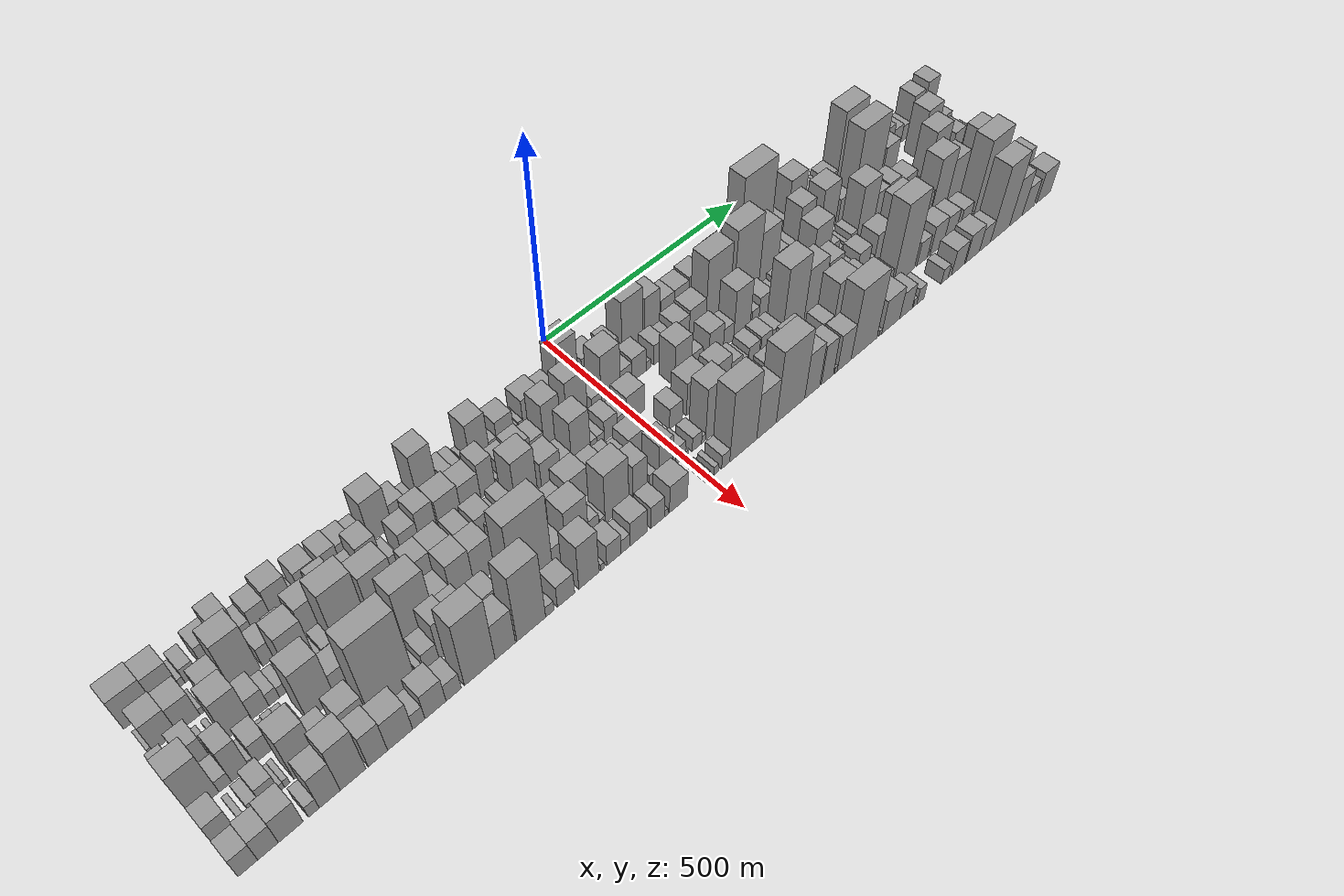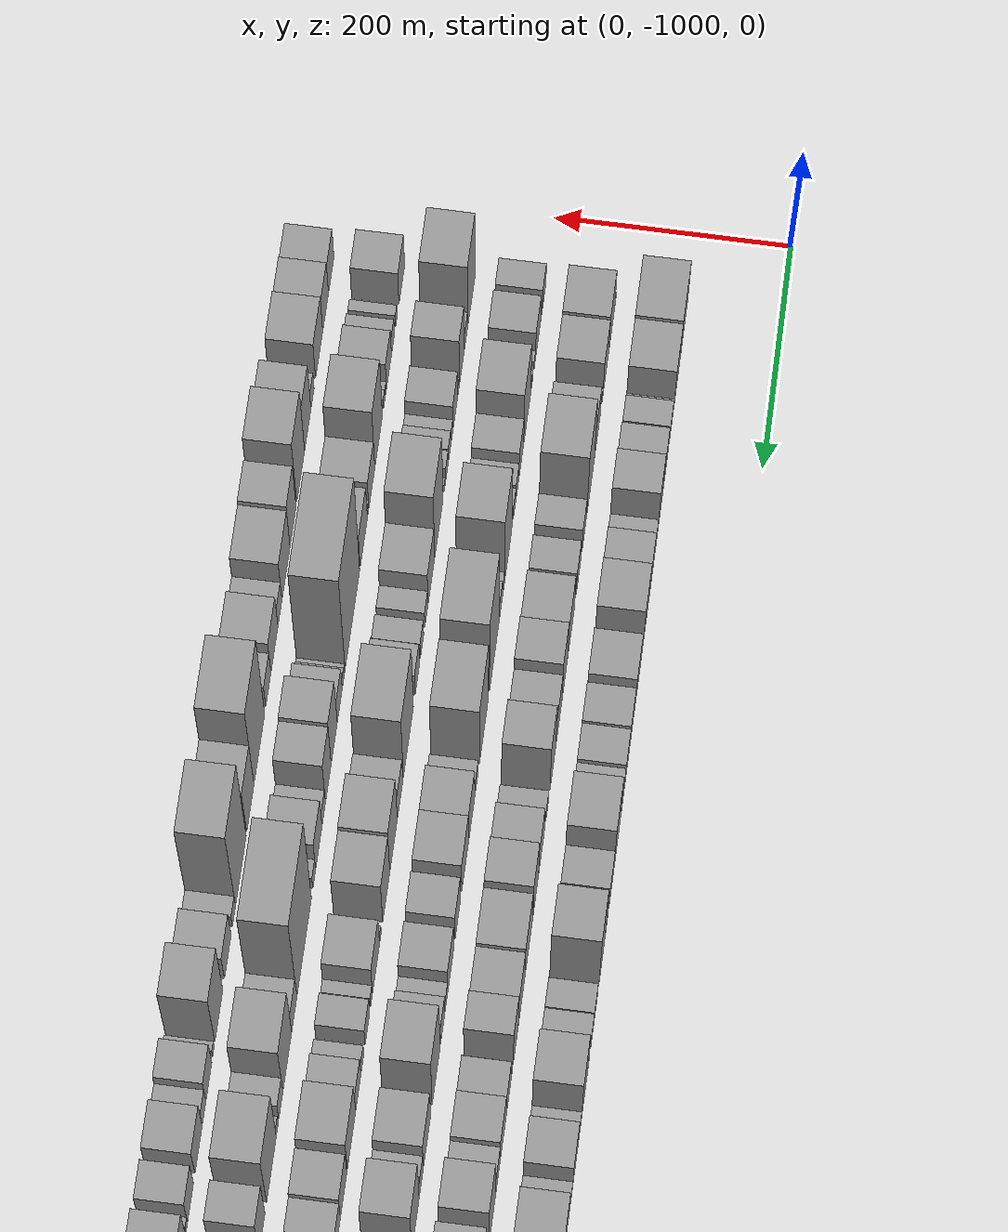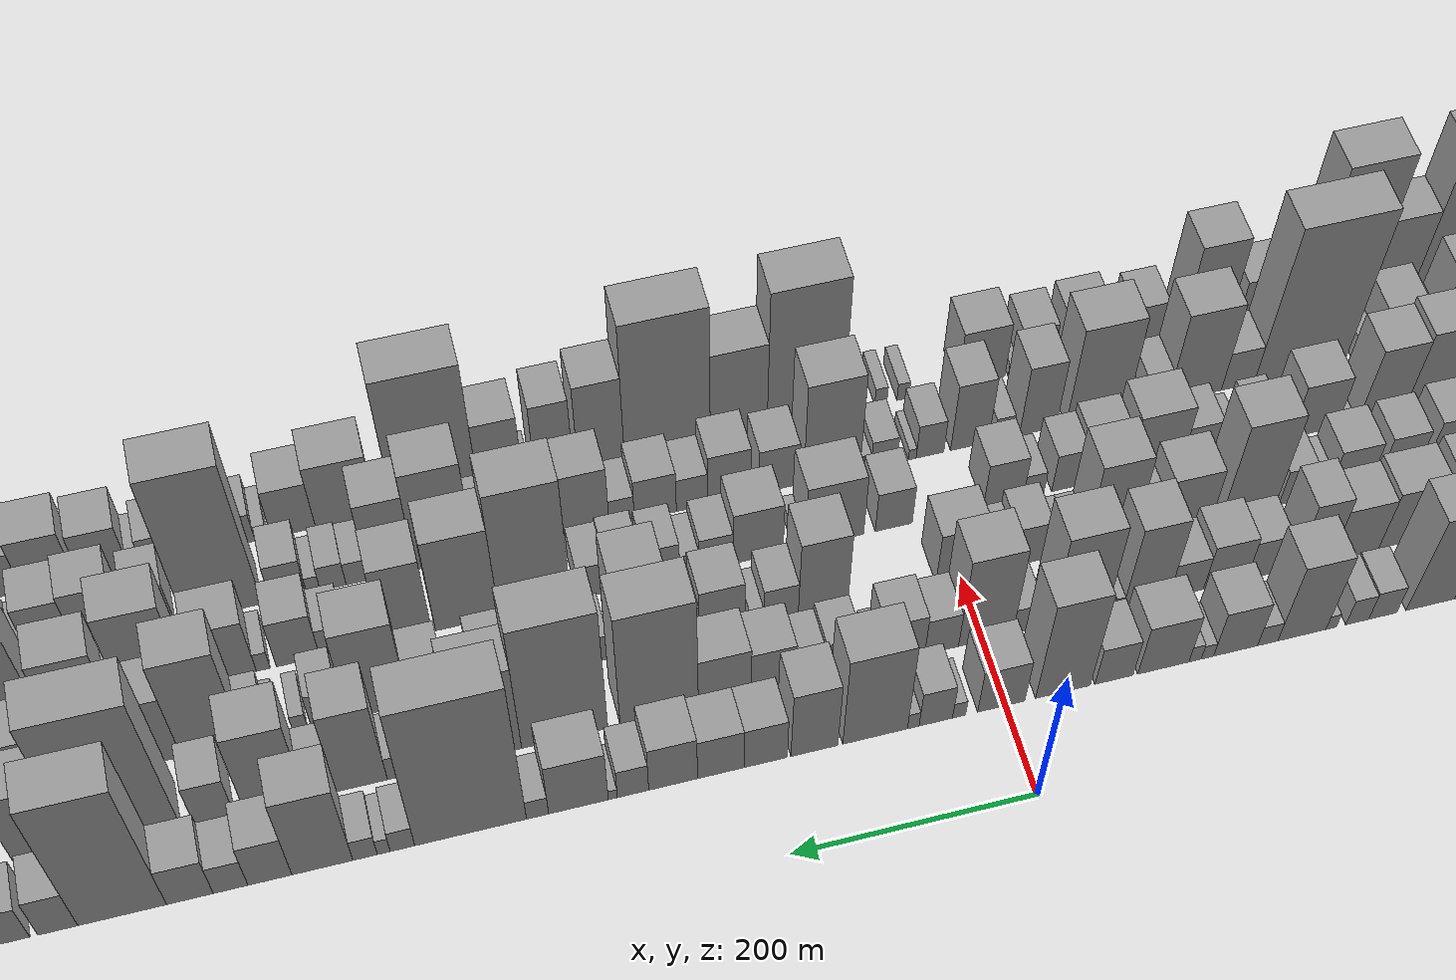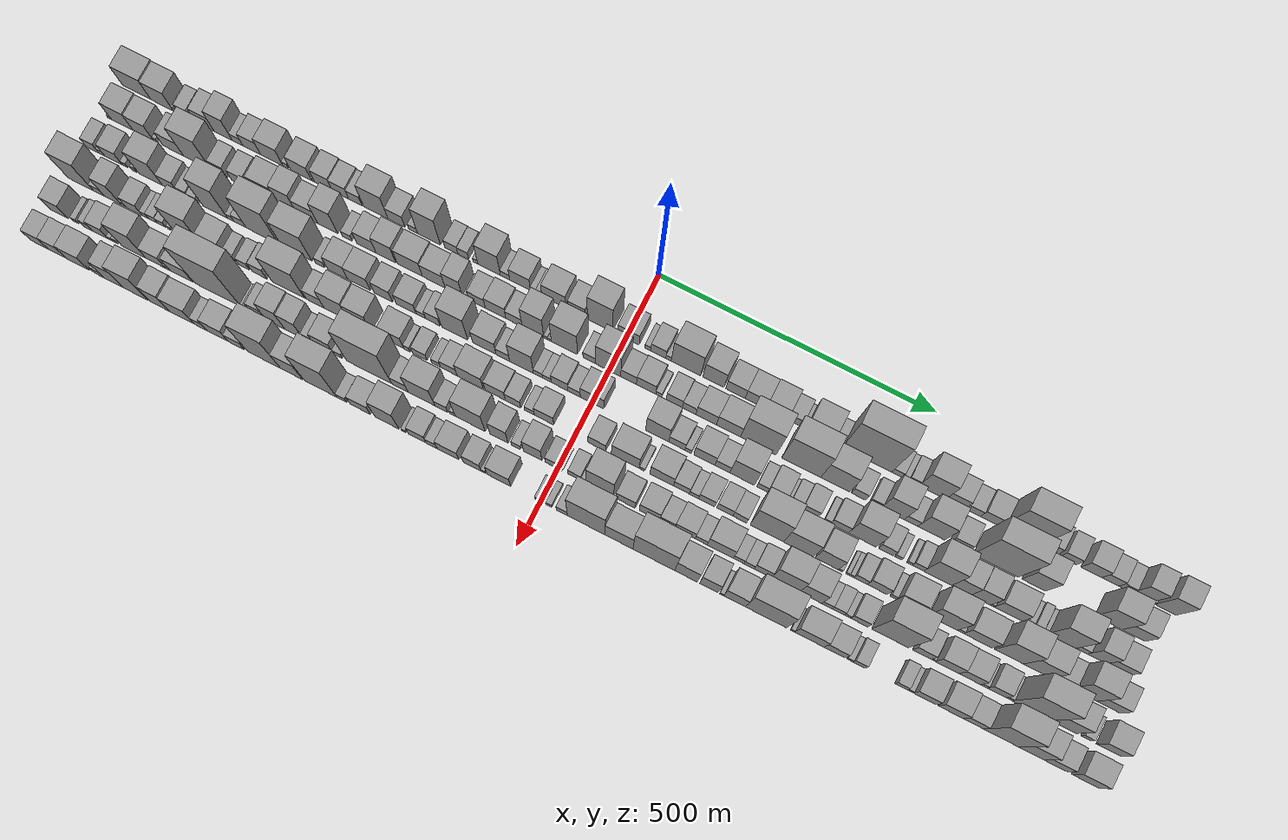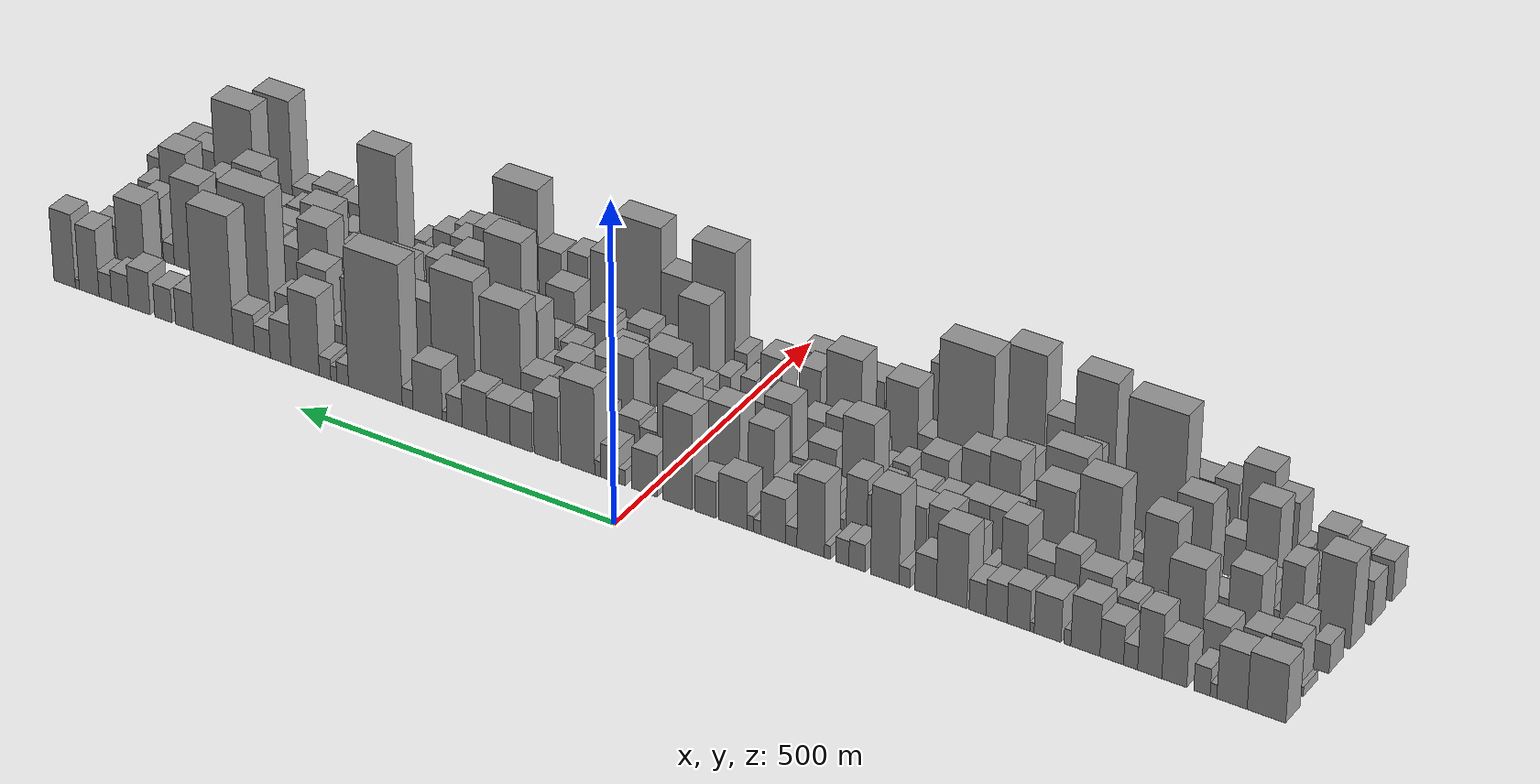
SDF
<sdf version="1.6">
 <world name="default">
  <scene>
   <sky><clouds><speed>12</speed></clouds></sky>
   <ambient>0.4 0.4 0.4 1</ambient>
   <background>0.7 0.7 0.7 1</background>
   <shadows>1</shadows>
  </scene>
  <gravity>0 0 -9.8066</gravity>
  <magnetic_field>6e-06 2.3e-05 -4.2e-05</magnetic_field>
  <physics default="0" name="default_physics" type="ode">
   <ode>
    <solver>
     <type>quick</type>
     <iters>10</iters>
     <sor>1.0</sor>
     <use_dynamic_moi_rescaling>0</use_dynamic_moi_rescaling>
    </solver>
    <constraints>
     <cfm>0</cfm>
     <erp>0.2</erp>
     <contact_max_correcting_vel>100</contact_max_correcting_vel>
     <contact_surface_layer>0.001</contact_surface_layer>
    </constraints>
   </ode>
   <max_step_size>0.004</max_step_size>
   <real_time_factor>1</real_time_factor>
   <real_time_update_rate>250</real_time_update_rate>
  </physics>
  <light name="sun" type="directional">
   <pose>0 0 10 0 0 0</pose>
   <diffuse>0.8 0.8 0.8 1</diffuse>
   <specular>0.2 0.2 0.2 1</specular>
   <attenuation>
    <range>1000</range>
    <constant>0.9</constant>
    <linear>0.01</linear>
    <quadratic>0.001</quadratic>
   </attenuation>
   <direction>-0.5 0.1 -0.9</direction>
  </light>
  <model name="building_1">
   <static>1</static>
   <pose>100.0000 -913.0944 0 0.000000 0.000000 0.000000</pose>
   <link name="link">
    <pose>0 0 45.00 0 0 0</pose>
    <collision name="collision"><geometry><box><size>40.0000 53.8113 90.0000</size></box></geometry></collision>
    <visual name="visual">
     <cast_shadows>0</cast_shadows>
     <geometry><box><size>40.0000 53.8113 90.0000</size></box></geometry>
     <material>
      <script>
       <uri>model://grey_wall/materials/scripts</uri>
       <uri>model://grey_wall/materials/textures</uri>
       <name>vrc/grey_wall</name>
      </script>
     </material>
    </visual>
   </link>
  </model>
  <model name="building_2">
   <static>1</static>
   <pose>100.0000 -864.8696 0 0.000000 0.000000 0.000000</pose>
   <link name="link">
    <pose>0 0 42.00 0 0 0</pose>
    <collision name="collision"><geometry><box><size>40.0000 42.6382 84.0000</size></box></geometry></collision>
    <visual name="visual">
     <cast_shadows>0</cast_shadows>
     <geometry><box><size>40.0000 42.6382 84.0000</size></box></geometry>
     <material>
      <script>
       <uri>model://grey_wall/materials/scripts</uri>
       <uri>model://grey_wall/materials/textures</uri>
       <name>vrc/grey_wall</name>
      </script>
     </material>
    </visual>
   </link>
  </model>
  <model name="building_3">
   <static>1</static>
   <pose>100.0000 -838.8419 0 0.000000 0.000000 0.000000</pose>
   <link name="link">
    <pose>0 0 10.50 0 0 0</pose>
    <collision name="collision"><geometry><box><size>40.0000 9.4172 21.0000</size></box></geometry></collision>
    <visual name="visual">
     <cast_shadows>0</cast_shadows>
     <geometry><box><size>40.0000 9.4172 21.0000</size></box></geometry>
     <material>
      <script>
       <uri>model://grey_wall/materials/scripts</uri>
       <uri>model://grey_wall/materials/textures</uri>
       <name>vrc/grey_wall</name>
      </script>
     </material>
    </visual>
   </link>
  </model>
  <model name="building_4">
   <static>1</static>
   <pose>100.0000 -822.6182 0 0.000000 0.000000 0.000000</pose>
   <link name="link">
    <pose>0 0 21.00 0 0 0</pose>
    <collision name="collision"><geometry><box><size>40.0000 23.0302 42.0000</size></box></geometry></collision>
    <visual name="visual">
     <cast_shadows>0</cast_shadows>
     <geometry><box><size>40.0000 23.0302 42.0000</size></box></geometry>
     <material>
      <script>
       <uri>model://grey_wall/materials/scripts</uri>
       <uri>model://grey_wall/materials/textures</uri>
       <name>vrc/grey_wall</name>
      </script>
     </material>
    </visual>
   </link>
  </model>
  <model name="building_5">
   <static>1</static>
   <pose>100.0000 -783.4196 0 0.000000 0.000000 0.000000</pose>
   <link name="link">
    <pose>0 0 33.00 0 0 0</pose>
    <collision name="collision"><geometry><box><size>40.0000 35.3670 66.0000</size></box></geometry></collision>
    <visual name="visual">
     <cast_shadows>0</cast_shadows>
     <geometry><box><size>40.0000 35.3670 66.0000</size></box></geometry>
     <material>
      <script>
       <uri>model://grey_wall/materials/scripts</uri>
       <uri>model://grey_wall/materials/textures</uri>
       <name>vrc/grey_wall</name>
      </script>
     </material>
    </visual>
   </link>
  </model>
  <model name="building_6">
   <static>1</static>
   <pose>100.0000 -748.5114 0 0.000000 0.000000 0.000000</pose>
   <link name="link">
    <pose>0 0 49.50 0 0 0</pose>
    <collision name="collision"><geometry><box><size>40.0000 34.4495 99.0000</size></box></geometry></collision>
    <visual name="visual">
     <cast_shadows>0</cast_shadows>
     <geometry><box><size>40.0000 34.4495 99.0000</size></box></geometry>
     <material>
      <script>
       <uri>model://grey_wall/materials/scripts</uri>
       <uri>model://grey_wall/materials/textures</uri>
       <name>vrc/grey_wall</name>
      </script>
     </material>
    </visual>
   </link>
  </model>
  <model name="building_7">
   <static>1</static>
   <pose>100.0000 -721.2804 0 0.000000 0.000000 0.000000</pose>
   <link name="link">
    <pose>0 0 18.00 0 0 0</pose>
    <collision name="collision"><geometry><box><size>40.0000 20.0126 36.0000</size></box></geometry></collision>
    <visual name="visual">
     <cast_shadows>0</cast_shadows>
     <geometry><box><size>40.0000 20.0126 36.0000</size></box></geometry>
     <material>
      <script>
       <uri>model://grey_wall/materials/scripts</uri>
       <uri>model://grey_wall/materials/textures</uri>
       <name>vrc/grey_wall</name>
      </script>
     </material>
    </visual>
   </link>
  </model>
  <model name="building_8">
   <static>1</static>
   <pose>100.0000 -694.3044 0 0.000000 0.000000 0.000000</pose>
   <link name="link">
    <pose>0 0 30.00 0 0 0</pose>
    <collision name="collision"><geometry><box><size>40.0000 33.9393 60.0000</size></box></geometry></collision>
    <visual name="visual">
     <cast_shadows>0</cast_shadows>
     <geometry><box><size>40.0000 33.9393 60.0000</size></box></geometry>
     <material>
      <script>
       <uri>model://grey_wall/materials/scripts</uri>
       <uri>model://grey_wall/materials/textures</uri>
       <name>vrc/grey_wall</name>
      </script>
     </material>
    </visual>
   </link>
  </model>
  <model name="building_9">
   <static>1</static>
   <pose>100.0000 -656.4122 0 0.000000 0.000000 0.000000</pose>
   <link name="link">
    <pose>0 0 40.50 0 0 0</pose>
    <collision name="collision"><geometry><box><size>40.0000 41.8451 81.0000</size></box></geometry></collision>
    <visual name="visual">
     <cast_shadows>0</cast_shadows>
     <geometry><box><size>40.0000 41.8451 81.0000</size></box></geometry>
     <material>
      <script>
       <uri>model://grey_wall/materials/scripts</uri>
       <uri>model://grey_wall/materials/textures</uri>
       <name>vrc/grey_wall</name>
      </script>
     </material>
    </visual>
   </link>
  </model>
  <model name="building_10">
   <static>1</static>
   <pose>100.0000 -630.5319 0 0.000000 0.000000 0.000000</pose>
   <link name="link">
    <pose>0 0 12.00 0 0 0</pose>
    <collision name="collision"><geometry><box><size>40.0000 9.9155 24.0000</size></box></geometry></collision>
    <visual name="visual">
     <cast_shadows>0</cast_shadows>
     <geometry><box><size>40.0000 9.9155 24.0000</size></box></geometry>
     <material>
      <script>
       <uri>model://grey_wall/materials/scripts</uri>
       <uri>model://grey_wall/materials/textures</uri>
       <name>vrc/grey_wall</name>
      </script>
     </material>
    </visual>
   </link>
  </model>
  <model name="building_11">
   <static>1</static>
   <pose>100.0000 -601.9083 0 0.000000 0.000000 0.000000</pose>
   <link name="link">
    <pose>0 0 33.00 0 0 0</pose>
    <collision name="collision"><geometry><box><size>40.0000 39.3316 66.0000</size></box></geometry></collision>
    <visual name="visual">
     <cast_shadows>0</cast_shadows>
     <geometry><box><size>40.0000 39.3316 66.0000</size></box></geometry>
     <material>
      <script>
       <uri>model://grey_wall/materials/scripts</uri>
       <uri>model://grey_wall/materials/textures</uri>
       <name>vrc/grey_wall</name>
      </script>
     </material>
    </visual>
   </link>
  </model>
  <model name="building_12">
   <static>1</static>
   <pose>100.0000 -579.2026 0 0.000000 0.000000 0.000000</pose>
   <link name="link">
    <pose>0 0 7.50 0 0 0</pose>
    <collision name="collision"><geometry><box><size>40.0000 6.0798 15.0000</size></box></geometry></collision>
    <visual name="visual">
     <cast_shadows>0</cast_shadows>
     <geometry><box><size>40.0000 6.0798 15.0000</size></box></geometry>
     <material>
      <script>
       <uri>model://grey_wall/materials/scripts</uri>
       <uri>model://grey_wall/materials/textures</uri>
       <name>vrc/grey_wall</name>
      </script>
     </material>
    </visual>
   </link>
  </model>
  <model name="building_13">
   <static>1</static>
   <pose>100.0000 -559.5826 0 0.000000 0.000000 0.000000</pose>
   <link name="link">
    <pose>0 0 31.50 0 0 0</pose>
    <collision name="collision"><geometry><box><size>40.0000 33.1601 63.0000</size></box></geometry></collision>
    <visual name="visual">
     <cast_shadows>0</cast_shadows>
     <geometry><box><size>40.0000 33.1601 63.0000</size></box></geometry>
     <material>
      <script>
       <uri>model://grey_wall/materials/scripts</uri>
       <uri>model://grey_wall/materials/textures</uri>
       <name>vrc/grey_wall</name>
      </script>
     </material>
    </visual>
   </link>
  </model>
  <model name="building_14">
   <static>1</static>
   <pose>100.0000 -527.5741 0 0.000000 0.000000 0.000000</pose>
   <link name="link">
    <pose>0 0 28.50 0 0 0</pose>
    <collision name="collision"><geometry><box><size>40.0000 30.8569 57.0000</size></box></geometry></collision>
    <visual name="visual">
     <cast_shadows>0</cast_shadows>
     <geometry><box><size>40.0000 30.8569 57.0000</size></box></geometry>
     <material>
      <script>
       <uri>model://grey_wall/materials/scripts</uri>
       <uri>model://grey_wall/materials/textures</uri>
       <name>vrc/grey_wall</name>
      </script>
     </material>
    </visual>
   </link>
  </model>
  <model name="building_15">
   <static>1</static>
   <pose>100.0000 -499.6027 0 0.000000 0.000000 0.000000</pose>
   <link name="link">
    <pose>0 0 24.00 0 0 0</pose>
    <collision name="collision"><geometry><box><size>40.0000 25.0861 48.0000</size></box></geometry></collision>
    <visual name="visual">
     <cast_shadows>0</cast_shadows>
     <geometry><box><size>40.0000 25.0861 48.0000</size></box></geometry>
     <material>
      <script>
       <uri>model://grey_wall/materials/scripts</uri>
       <uri>model://grey_wall/materials/textures</uri>
       <name>vrc/grey_wall</name>
      </script>
     </material>
    </visual>
   </link>
  </model>
  <model name="building_16">
   <static>1</static>
   <pose>100.0000 -461.4363 0 0.000000 0.000000 0.000000</pose>
   <link name="link">
    <pose>0 0 58.50 0 0 0</pose>
    <collision name="collision"><geometry><box><size>40.0000 45.2466 117.0000</size></box></geometry></collision>
    <visual name="visual">
     <cast_shadows>0</cast_shadows>
     <geometry><box><size>40.0000 45.2466 117.0000</size></box></geometry>
     <material>
      <script>
       <uri>model://grey_wall/materials/scripts</uri>
       <uri>model://grey_wall/materials/textures</uri>
       <name>vrc/grey_wall</name>
      </script>
     </material>
    </visual>
   </link>
  </model>
  <model name="building_17">
   <static>1</static>
   <pose>100.0000 -422.9054 0 0.000000 0.000000 0.000000</pose>
   <link name="link">
    <pose>0 0 30.00 0 0 0</pose>
    <collision name="collision"><geometry><box><size>40.0000 31.8152 60.0000</size></box></geometry></collision>
    <visual name="visual">
     <cast_shadows>0</cast_shadows>
     <geometry><box><size>40.0000 31.8152 60.0000</size></box></geometry>
     <material>
      <script>
       <uri>model://grey_wall/materials/scripts</uri>
       <uri>model://grey_wall/materials/textures</uri>
       <name>vrc/grey_wall</name>
      </script>
     </material>
    </visual>
   </link>
  </model>
  <model name="building_18">
   <static>1</static>
   <pose>100.0000 -391.7450 0 0.000000 0.000000 0.000000</pose>
   <link name="link">
    <pose>0 0 15.00 0 0 0</pose>
    <collision name="collision"><geometry><box><size>40.0000 16.5057 30.0000</size></box></geometry></collision>
    <visual name="visual">
     <cast_shadows>0</cast_shadows>
     <geometry><box><size>40.0000 16.5057 30.0000</size></box></geometry>
     <material>
      <script>
       <uri>model://grey_wall/materials/scripts</uri>
       <uri>model://grey_wall/materials/textures</uri>
       <name>vrc/grey_wall</name>
      </script>
     </material>
    </visual>
   </link>
  </model>
  <model name="building_19">
   <static>1</static>
   <pose>100.0000 -362.2760 0 0.000000 0.000000 0.000000</pose>
   <link name="link">
    <pose>0 0 70.50 0 0 0</pose>
    <collision name="collision"><geometry><box><size>40.0000 42.4322 141.0000</size></box></geometry></collision>
    <visual name="visual">
     <cast_shadows>0</cast_shadows>
     <geometry><box><size>40.0000 42.4322 141.0000</size></box></geometry>
     <material>
      <script>
       <uri>model://grey_wall/materials/scripts</uri>
       <uri>model://grey_wall/materials/textures</uri>
       <name>vrc/grey_wall</name>
      </script>
     </material>
    </visual>
   </link>
  </model>
  <model name="building_20">
   <static>1</static>
   <pose>100.0000 -320.8632 0 0.000000 0.000000 0.000000</pose>
   <link name="link">
    <pose>0 0 21.00 0 0 0</pose>
    <collision name="collision"><geometry><box><size>40.0000 24.3934 42.0000</size></box></geometry></collision>
    <visual name="visual">
     <cast_shadows>0</cast_shadows>
     <geometry><box><size>40.0000 24.3934 42.0000</size></box></geometry>
     <material>
      <script>
       <uri>model://grey_wall/materials/scripts</uri>
       <uri>model://grey_wall/materials/textures</uri>
       <name>vrc/grey_wall</name>
      </script>
     </material>
    </visual>
   </link>
  </model>
  <model name="building_21">
   <static>1</static>
   <pose>100.0000 -298.7155 0 0.000000 0.000000 0.000000</pose>
   <link name="link">
    <pose>0 0 19.50 0 0 0</pose>
    <collision name="collision"><geometry><box><size>40.0000 19.9018 39.0000</size></box></geometry></collision>
    <visual name="visual">
     <cast_shadows>0</cast_shadows>
     <geometry><box><size>40.0000 19.9018 39.0000</size></box></geometry>
     <material>
      <script>
       <uri>model://grey_wall/materials/scripts</uri>
       <uri>model://grey_wall/materials/textures</uri>
       <name>vrc/grey_wall</name>
      </script>
     </material>
    </visual>
   </link>
  </model>
  <model name="building_22">
   <static>1</static>
   <pose>100.0000 -276.2266 0 0.000000 0.000000 0.000000</pose>
   <link name="link">
    <pose>0 0 10.50 0 0 0</pose>
    <collision name="collision"><geometry><box><size>40.0000 9.0762 21.0000</size></box></geometry></collision>
    <visual name="visual">
     <cast_shadows>0</cast_shadows>
     <geometry><box><size>40.0000 9.0762 21.0000</size></box></geometry>
     <material>
      <script>
       <uri>model://grey_wall/materials/scripts</uri>
       <uri>model://grey_wall/materials/textures</uri>
       <name>vrc/grey_wall</name>
      </script>
     </material>
    </visual>
   </link>
  </model>
  <model name="building_23">
   <static>1</static>
   <pose>100.0000 -250.9296 0 0.000000 0.000000 0.000000</pose>
   <link name="link">
    <pose>0 0 58.50 0 0 0</pose>
    <collision name="collision"><geometry><box><size>40.0000 41.5178 117.0000</size></box></geometry></collision>
    <visual name="visual">
     <cast_shadows>0</cast_shadows>
     <geometry><box><size>40.0000 41.5178 117.0000</size></box></geometry>
     <material>
      <script>
       <uri>model://grey_wall/materials/scripts</uri>
       <uri>model://grey_wall/materials/textures</uri>
       <name>vrc/grey_wall</name>
      </script>
     </material>
    </visual>
   </link>
  </model>
  <model name="building_24">
   <static>1</static>
   <pose>100.0000 -221.4806 0 0.000000 0.000000 0.000000</pose>
   <link name="link">
    <pose>0 0 15.00 0 0 0</pose>
    <collision name="collision"><geometry><box><size>40.0000 17.3802 30.0000</size></box></geometry></collision>
    <visual name="visual">
     <cast_shadows>0</cast_shadows>
     <geometry><box><size>40.0000 17.3802 30.0000</size></box></geometry>
     <material>
      <script>
       <uri>model://grey_wall/materials/scripts</uri>
       <uri>model://grey_wall/materials/textures</uri>
       <name>vrc/grey_wall</name>
      </script>
     </material>
    </visual>
   </link>
  </model>
  <model name="building_25">
   <static>1</static>
   <pose>100.0000 -193.9377 0 0.000000 0.000000 0.000000</pose>
   <link name="link">
    <pose>0 0 34.50 0 0 0</pose>
    <collision name="collision"><geometry><box><size>40.0000 37.7056 69.0000</size></box></geometry></collision>
    <visual name="visual">
     <cast_shadows>0</cast_shadows>
     <geometry><box><size>40.0000 37.7056 69.0000</size></box></geometry>
     <material>
      <script>
       <uri>model://grey_wall/materials/scripts</uri>
       <uri>model://grey_wall/materials/textures</uri>
       <name>vrc/grey_wall</name>
      </script>
     </material>
    </visual>
   </link>
  </model>
  <model name="building_26">
   <static>1</static>
   <pose>100.0000 -169.8453 0 0.000000 0.000000 0.000000</pose>
   <link name="link">
    <pose>0 0 10.50 0 0 0</pose>
    <collision name="collision"><geometry><box><size>40.0000 10.4792 21.0000</size></box></geometry></collision>
    <visual name="visual">
     <cast_shadows>0</cast_shadows>
     <geometry><box><size>40.0000 10.4792 21.0000</size></box></geometry>
     <material>
      <script>
       <uri>model://grey_wall/materials/scripts</uri>
       <uri>model://grey_wall/materials/textures</uri>
       <name>vrc/grey_wall</name>
      </script>
     </material>
    </visual>
   </link>
  </model>
  <model name="building_27">
   <static>1</static>
   <pose>100.0000 -159.3159 0 0.000000 0.000000 0.000000</pose>
   <link name="link">
    <pose>0 0 12.00 0 0 0</pose>
    <collision name="collision"><geometry><box><size>40.0000 10.5795 24.0000</size></box></geometry></collision>
    <visual name="visual">
     <cast_shadows>0</cast_shadows>
     <geometry><box><size>40.0000 10.5795 24.0000</size></box></geometry>
     <material>
      <script>
       <uri>model://grey_wall/materials/scripts</uri>
       <uri>model://grey_wall/materials/textures</uri>
       <name>vrc/grey_wall</name>
      </script>
     </material>
    </visual>
   </link>
  </model>
  <model name="building_28">
   <static>1</static>
   <pose>100.0000 -132.3050 0 0.000000 0.000000 0.000000</pose>
   <link name="link">
    <pose>0 0 37.50 0 0 0</pose>
    <collision name="collision"><geometry><box><size>40.0000 43.4423 75.0000</size></box></geometry></collision>
    <visual name="visual">
     <cast_shadows>0</cast_shadows>
     <geometry><box><size>40.0000 43.4423 75.0000</size></box></geometry>
     <material>
      <script>
       <uri>model://grey_wall/materials/scripts</uri>
       <uri>model://grey_wall/materials/textures</uri>
       <name>vrc/grey_wall</name>
      </script>
     </material>
    </visual>
   </link>
  </model>
  <model name="building_29">
   <static>1</static>
   <pose>100.0000 -90.5196 0 0.000000 0.000000 0.000000</pose>
   <link name="link">
    <pose>0 0 28.50 0 0 0</pose>
    <collision name="collision"><geometry><box><size>40.0000 32.1285 57.0000</size></box></geometry></collision>
    <visual name="visual">
     <cast_shadows>0</cast_shadows>
     <geometry><box><size>40.0000 32.1285 57.0000</size></box></geometry>
     <material>
      <script>
       <uri>model://grey_wall/materials/scripts</uri>
       <uri>model://grey_wall/materials/textures</uri>
       <name>vrc/grey_wall</name>
      </script>
     </material>
    </visual>
   </link>
  </model>
  <model name="building_30">
   <static>1</static>
   <pose>100.0000 -47.5094 0 0.000000 0.000000 0.000000</pose>
   <link name="link">
    <pose>0 0 75.00 0 0 0</pose>
    <collision name="collision"><geometry><box><size>40.0000 45.8918 150.0000</size></box></geometry></collision>
    <visual name="visual">
     <cast_shadows>0</cast_shadows>
     <geometry><box><size>40.0000 45.8918 150.0000</size></box></geometry>
     <material>
      <script>
       <uri>model://grey_wall/materials/scripts</uri>
       <uri>model://grey_wall/materials/textures</uri>
       <name>vrc/grey_wall</name>
      </script>
     </material>
    </visual>
   </link>
  </model>
  <model name="building_31">
   <static>1</static>
   <pose>100.0000 4.1189 0 0.000000 0.000000 0.000000</pose>
   <link name="link">
    <pose>0 0 33.00 0 0 0</pose>
    <collision name="collision"><geometry><box><size>40.0000 39.3649 66.0000</size></box></geometry></collision>
    <visual name="visual">
     <cast_shadows>0</cast_shadows>
     <geometry><box><size>40.0000 39.3649 66.0000</size></box></geometry>
     <material>
      <script>
       <uri>model://grey_wall/materials/scripts</uri>
       <uri>model://grey_wall/materials/textures</uri>
       <name>vrc/grey_wall</name>
      </script>
     </material>
    </visual>
   </link>
  </model>
  <model name="building_32">
   <static>1</static>
   <pose>100.0000 39.2555 0 0.000000 0.000000 0.000000</pose>
   <link name="link">
    <pose>0 0 12.00 0 0 0</pose>
    <collision name="collision"><geometry><box><size>40.0000 10.9082 24.0000</size></box></geometry></collision>
    <visual name="visual">
     <cast_shadows>0</cast_shadows>
     <geometry><box><size>40.0000 10.9082 24.0000</size></box></geometry>
     <material>
      <script>
       <uri>model://grey_wall/materials/scripts</uri>
       <uri>model://grey_wall/materials/textures</uri>
       <name>vrc/grey_wall</name>
      </script>
     </material>
    </visual>
   </link>
  </model>
  <model name="building_33">
   <static>1</static>
   <pose>100.0000 58.5497 0 0.000000 0.000000 0.000000</pose>
   <link name="link">
    <pose>0 0 27.00 0 0 0</pose>
    <collision name="collision"><geometry><box><size>40.0000 27.6804 54.0000</size></box></geometry></collision>
    <visual name="visual">
     <cast_shadows>0</cast_shadows>
     <geometry><box><size>40.0000 27.6804 54.0000</size></box></geometry>
     <material>
      <script>
       <uri>model://grey_wall/materials/scripts</uri>
       <uri>model://grey_wall/materials/textures</uri>
       <name>vrc/grey_wall</name>
      </script>
     </material>
    </visual>
   </link>
  </model>
  <model name="building_34">
   <static>1</static>
   <pose>100.0000 77.1985 0 0.000000 0.000000 0.000000</pose>
   <link name="link">
    <pose>0 0 12.00 0 0 0</pose>
    <collision name="collision"><geometry><box><size>40.0000 9.6171 24.0000</size></box></geometry></collision>
    <visual name="visual">
     <cast_shadows>0</cast_shadows>
     <geometry><box><size>40.0000 9.6171 24.0000</size></box></geometry>
     <material>
      <script>
       <uri>model://grey_wall/materials/scripts</uri>
       <uri>model://grey_wall/materials/textures</uri>
       <name>vrc/grey_wall</name>
      </script>
     </material>
    </visual>
   </link>
  </model>
  <model name="building_35">
   <static>1</static>
   <pose>100.0000 108.6096 0 0.000000 0.000000 0.000000</pose>
   <link name="link">
    <pose>0 0 69.00 0 0 0</pose>
    <collision name="collision"><geometry><box><size>40.0000 53.2051 138.0000</size></box></geometry></collision>
    <visual name="visual">
     <cast_shadows>0</cast_shadows>
     <geometry><box><size>40.0000 53.2051 138.0000</size></box></geometry>
     <material>
      <script>
       <uri>model://grey_wall/materials/scripts</uri>
       <uri>model://grey_wall/materials/textures</uri>
       <name>vrc/grey_wall</name>
      </script>
     </material>
    </visual>
   </link>
  </model>
  <model name="building_36">
   <static>1</static>
   <pose>100.0000 158.4037 0 0.000000 0.000000 0.000000</pose>
   <link name="link">
    <pose>0 0 51.00 0 0 0</pose>
    <collision name="collision"><geometry><box><size>40.0000 38.3830 102.0000</size></box></geometry></collision>
    <visual name="visual">
     <cast_shadows>0</cast_shadows>
     <geometry><box><size>40.0000 38.3830 102.0000</size></box></geometry>
     <material>
      <script>
       <uri>model://grey_wall/materials/scripts</uri>
       <uri>model://grey_wall/materials/textures</uri>
       <name>vrc/grey_wall</name>
      </script>
     </material>
    </visual>
   </link>
  </model>
  <model name="building_37">
   <static>1</static>
   <pose>100.0000 198.1465 0 0.000000 0.000000 0.000000</pose>
   <link name="link">
    <pose>0 0 31.50 0 0 0</pose>
    <collision name="collision"><geometry><box><size>40.0000 35.1027 63.0000</size></box></geometry></collision>
    <visual name="visual">
     <cast_shadows>0</cast_shadows>
     <geometry><box><size>40.0000 35.1027 63.0000</size></box></geometry>
     <material>
      <script>
       <uri>model://grey_wall/materials/scripts</uri>
       <uri>model://grey_wall/materials/textures</uri>
       <name>vrc/grey_wall</name>
      </script>
     </material>
    </visual>
   </link>
  </model>
  <model name="building_38">
   <static>1</static>
   <pose>100.0000 234.5005 0 0.000000 0.000000 0.000000</pose>
   <link name="link">
    <pose>0 0 31.50 0 0 0</pose>
    <collision name="collision"><geometry><box><size>40.0000 37.6052 63.0000</size></box></geometry></collision>
    <visual name="visual">
     <cast_shadows>0</cast_shadows>
     <geometry><box><size>40.0000 37.6052 63.0000</size></box></geometry>
     <material>
      <script>
       <uri>model://grey_wall/materials/scripts</uri>
       <uri>model://grey_wall/materials/textures</uri>
       <name>vrc/grey_wall</name>
      </script>
     </material>
    </visual>
   </link>
  </model>
  <model name="building_39">
   <static>1</static>
   <pose>100.0000 272.9587 0 0.000000 0.000000 0.000000</pose>
   <link name="link">
    <pose>0 0 34.50 0 0 0</pose>
    <collision name="collision"><geometry><box><size>40.0000 39.3113 69.0000</size></box></geometry></collision>
    <visual name="visual">
     <cast_shadows>0</cast_shadows>
     <geometry><box><size>40.0000 39.3113 69.0000</size></box></geometry>
     <material>
      <script>
       <uri>model://grey_wall/materials/scripts</uri>
       <uri>model://grey_wall/materials/textures</uri>
       <name>vrc/grey_wall</name>
      </script>
     </material>
    </visual>
   </link>
  </model>
  <model name="building_40">
   <static>1</static>
   <pose>100.0000 305.1533 0 0.000000 0.000000 0.000000</pose>
   <link name="link">
    <pose>0 0 22.50 0 0 0</pose>
    <collision name="collision"><geometry><box><size>40.0000 25.0781 45.0000</size></box></geometry></collision>
    <visual name="visual">
     <cast_shadows>0</cast_shadows>
     <geometry><box><size>40.0000 25.0781 45.0000</size></box></geometry>
     <material>
      <script>
       <uri>model://grey_wall/materials/scripts</uri>
       <uri>model://grey_wall/materials/textures</uri>
       <name>vrc/grey_wall</name>
      </script>
     </material>
    </visual>
   </link>
  </model>
  <model name="building_41">
   <static>1</static>
   <pose>100.0000 321.2895 0 0.000000 0.000000 0.000000</pose>
   <link name="link">
    <pose>0 0 7.50 0 0 0</pose>
    <collision name="collision"><geometry><box><size>40.0000 7.1942 15.0000</size></box></geometry></collision>
    <visual name="visual">
     <cast_shadows>0</cast_shadows>
     <geometry><box><size>40.0000 7.1942 15.0000</size></box></geometry>
     <material>
      <script>
       <uri>model://grey_wall/materials/scripts</uri>
       <uri>model://grey_wall/materials/textures</uri>
       <name>vrc/grey_wall</name>
      </script>
     </material>
    </visual>
   </link>
  </model>
  <model name="building_42">
   <static>1</static>
   <pose>100.0000 348.6577 0 0.000000 0.000000 0.000000</pose>
   <link name="link">
    <pose>0 0 40.50 0 0 0</pose>
    <collision name="collision"><geometry><box><size>40.0000 47.5422 81.0000</size></box></geometry></collision>
    <visual name="visual">
     <cast_shadows>0</cast_shadows>
     <geometry><box><size>40.0000 47.5422 81.0000</size></box></geometry>
     <material>
      <script>
       <uri>model://grey_wall/materials/scripts</uri>
       <uri>model://grey_wall/materials/textures</uri>
       <name>vrc/grey_wall</name>
      </script>
     </material>
    </visual>
   </link>
  </model>
  <model name="building_43">
   <static>1</static>
   <pose>100.0000 381.1885 0 0.000000 0.000000 0.000000</pose>
   <link name="link">
    <pose>0 0 15.00 0 0 0</pose>
    <collision name="collision"><geometry><box><size>40.0000 17.5194 30.0000</size></box></geometry></collision>
    <visual name="visual">
     <cast_shadows>0</cast_shadows>
     <geometry><box><size>40.0000 17.5194 30.0000</size></box></geometry>
     <material>
      <script>
       <uri>model://grey_wall/materials/scripts</uri>
       <uri>model://grey_wall/materials/textures</uri>
       <name>vrc/grey_wall</name>
      </script>
     </material>
    </visual>
   </link>
  </model>
  <model name="building_44">
   <static>1</static>
   <pose>100.0000 433.9700 0 0.000000 0.000000 0.000000</pose>
   <link name="link">
    <pose>0 0 112.50 0 0 0</pose>
    <collision name="collision"><geometry><box><size>40.0000 88.0436 225.0000</size></box></geometry></collision>
    <visual name="visual">
     <cast_shadows>0</cast_shadows>
     <geometry><box><size>40.0000 88.0436 225.0000</size></box></geometry>
     <material>
      <script>
       <uri>model://grey_wall/materials/scripts</uri>
       <uri>model://grey_wall/materials/textures</uri>
       <name>vrc/grey_wall</name>
      </script>
     </material>
    </visual>
   </link>
  </model>
  <model name="building_45">
   <static>1</static>
   <pose>100.0000 487.5893 0 0.000000 0.000000 0.000000</pose>
   <link name="link">
    <pose>0 0 16.50 0 0 0</pose>
    <collision name="collision"><geometry><box><size>40.0000 19.1948 33.0000</size></box></geometry></collision>
    <visual name="visual">
     <cast_shadows>0</cast_shadows>
     <geometry><box><size>40.0000 19.1948 33.0000</size></box></geometry>
     <material>
      <script>
       <uri>model://grey_wall/materials/scripts</uri>
       <uri>model://grey_wall/materials/textures</uri>
       <name>vrc/grey_wall</name>
      </script>
     </material>
    </visual>
   </link>
  </model>
  <model name="building_46">
   <static>1</static>
   <pose>100.0000 502.1952 0 0.000000 0.000000 0.000000</pose>
   <link name="link">
    <pose>0 0 12.00 0 0 0</pose>
    <collision name="collision"><geometry><box><size>40.0000 10.0170 24.0000</size></box></geometry></collision>
    <visual name="visual">
     <cast_shadows>0</cast_shadows>
     <geometry><box><size>40.0000 10.0170 24.0000</size></box></geometry>
     <material>
      <script>
       <uri>model://grey_wall/materials/scripts</uri>
       <uri>model://grey_wall/materials/textures</uri>
       <name>vrc/grey_wall</name>
      </script>
     </material>
    </visual>
   </link>
  </model>
  <model name="building_47">
   <static>1</static>
   <pose>100.0000 516.7106 0 0.000000 0.000000 0.000000</pose>
   <link name="link">
    <pose>0 0 16.50 0 0 0</pose>
    <collision name="collision"><geometry><box><size>40.0000 19.0138 33.0000</size></box></geometry></collision>
    <visual name="visual">
     <cast_shadows>0</cast_shadows>
     <geometry><box><size>40.0000 19.0138 33.0000</size></box></geometry>
     <material>
      <script>
       <uri>model://grey_wall/materials/scripts</uri>
       <uri>model://grey_wall/materials/textures</uri>
       <name>vrc/grey_wall</name>
      </script>
     </material>
    </visual>
   </link>
  </model>
  <model name="building_48">
   <static>1</static>
   <pose>100.0000 549.8775 0 0.000000 0.000000 0.000000</pose>
   <link name="link">
    <pose>0 0 63.00 0 0 0</pose>
    <collision name="collision"><geometry><box><size>40.0000 47.3200 126.0000</size></box></geometry></collision>
    <visual name="visual">
     <cast_shadows>0</cast_shadows>
     <geometry><box><size>40.0000 47.3200 126.0000</size></box></geometry>
     <material>
      <script>
       <uri>model://grey_wall/materials/scripts</uri>
       <uri>model://grey_wall/materials/textures</uri>
       <name>vrc/grey_wall</name>
      </script>
     </material>
    </visual>
   </link>
  </model>
  <model name="building_49">
   <static>1</static>
   <pose>100.0000 590.4415 0 0.000000 0.000000 0.000000</pose>
   <link name="link">
    <pose>0 0 33.00 0 0 0</pose>
    <collision name="collision"><geometry><box><size>40.0000 33.8081 66.0000</size></box></geometry></collision>
    <visual name="visual">
     <cast_shadows>0</cast_shadows>
     <geometry><box><size>40.0000 33.8081 66.0000</size></box></geometry>
     <material>
      <script>
       <uri>model://grey_wall/materials/scripts</uri>
       <uri>model://grey_wall/materials/textures</uri>
       <name>vrc/grey_wall</name>
      </script>
     </material>
    </visual>
   </link>
  </model>
  <model name="building_50">
   <static>1</static>
   <pose>100.0000 620.6591 0 0.000000 0.000000 0.000000</pose>
   <link name="link">
    <pose>0 0 22.50 0 0 0</pose>
    <collision name="collision"><geometry><box><size>40.0000 26.6270 45.0000</size></box></geometry></collision>
    <visual name="visual">
     <cast_shadows>0</cast_shadows>
     <geometry><box><size>40.0000 26.6270 45.0000</size></box></geometry>
     <material>
      <script>
       <uri>model://grey_wall/materials/scripts</uri>
       <uri>model://grey_wall/materials/textures</uri>
       <name>vrc/grey_wall</name>
      </script>
     </material>
    </visual>
   </link>
  </model>
  <model name="building_51">
   <static>1</static>
   <pose>100.0000 651.8276 0 0.000000 0.000000 0.000000</pose>
   <link name="link">
    <pose>0 0 30.00 0 0 0</pose>
    <collision name="collision"><geometry><box><size>40.0000 35.7100 60.0000</size></box></geometry></collision>
    <visual name="visual">
     <cast_shadows>0</cast_shadows>
     <geometry><box><size>40.0000 35.7100 60.0000</size></box></geometry>
     <material>
      <script>
       <uri>model://grey_wall/materials/scripts</uri>
       <uri>model://grey_wall/materials/textures</uri>
       <name>vrc/grey_wall</name>
      </script>
     </material>
    </visual>
   </link>
  </model>
  <model name="building_52">
   <static>1</static>
   <pose>100.0000 703.3484 0 0.000000 0.000000 0.000000</pose>
   <link name="link">
    <pose>0 0 103.50 0 0 0</pose>
    <collision name="collision"><geometry><box><size>40.0000 67.3316 207.0000</size></box></geometry></collision>
    <visual name="visual">
     <cast_shadows>0</cast_shadows>
     <geometry><box><size>40.0000 67.3316 207.0000</size></box></geometry>
     <material>
      <script>
       <uri>model://grey_wall/materials/scripts</uri>
       <uri>model://grey_wall/materials/textures</uri>
       <name>vrc/grey_wall</name>
      </script>
     </material>
    </visual>
   </link>
  </model>
  <model name="building_53">
   <static>1</static>
   <pose>100.0000 752.0779 0 0.000000 0.000000 0.000000</pose>
   <link name="link">
    <pose>0 0 30.00 0 0 0</pose>
    <collision name="collision"><geometry><box><size>40.0000 30.1275 60.0000</size></box></geometry></collision>
    <visual name="visual">
     <cast_shadows>0</cast_shadows>
     <geometry><box><size>40.0000 30.1275 60.0000</size></box></geometry>
     <material>
      <script>
       <uri>model://grey_wall/materials/scripts</uri>
       <uri>model://grey_wall/materials/textures</uri>
       <name>vrc/grey_wall</name>
      </script>
     </material>
    </visual>
   </link>
  </model>
  <model name="building_54">
   <static>1</static>
   <pose>100.0000 787.8107 0 0.000000 0.000000 0.000000</pose>
   <link name="link">
    <pose>0 0 27.00 0 0 0</pose>
    <collision name="collision"><geometry><box><size>40.0000 29.3382 54.0000</size></box></geometry></collision>
    <visual name="visual">
     <cast_shadows>0</cast_shadows>
     <geometry><box><size>40.0000 29.3382 54.0000</size></box></geometry>
     <material>
      <script>
       <uri>model://grey_wall/materials/scripts</uri>
       <uri>model://grey_wall/materials/textures</uri>
       <name>vrc/grey_wall</name>
      </script>
     </material>
    </visual>
   </link>
  </model>
  <model name="building_55">
   <static>1</static>
   <pose>100.0000 828.6720 0 0.000000 0.000000 0.000000</pose>
   <link name="link">
    <pose>0 0 34.50 0 0 0</pose>
    <collision name="collision"><geometry><box><size>40.0000 36.3844 69.0000</size></box></geometry></collision>
    <visual name="visual">
     <cast_shadows>0</cast_shadows>
     <geometry><box><size>40.0000 36.3844 69.0000</size></box></geometry>
     <material>
      <script>
       <uri>model://grey_wall/materials/scripts</uri>
       <uri>model://grey_wall/materials/textures</uri>
       <name>vrc/grey_wall</name>
      </script>
     </material>
    </visual>
   </link>
  </model>
  <model name="building_56">
   <static>1</static>
   <pose>100.0000 861.6268 0 0.000000 0.000000 0.000000</pose>
   <link name="link">
    <pose>0 0 25.50 0 0 0</pose>
    <collision name="collision"><geometry><box><size>40.0000 29.5252 51.0000</size></box></geometry></collision>
    <visual name="visual">
     <cast_shadows>0</cast_shadows>
     <geometry><box><size>40.0000 29.5252 51.0000</size></box></geometry>
     <material>
      <script>
       <uri>model://grey_wall/materials/scripts</uri>
       <uri>model://grey_wall/materials/textures</uri>
       <name>vrc/grey_wall</name>
      </script>
     </material>
    </visual>
   </link>
  </model>
  <model name="building_57">
   <static>1</static>
   <pose>100.0000 887.3381 0 0.000000 0.000000 0.000000</pose>
   <link name="link">
    <pose>0 0 21.00 0 0 0</pose>
    <collision name="collision"><geometry><box><size>40.0000 21.8974 42.0000</size></box></geometry></collision>
    <visual name="visual">
     <cast_shadows>0</cast_shadows>
     <geometry><box><size>40.0000 21.8974 42.0000</size></box></geometry>
     <material>
      <script>
       <uri>model://grey_wall/materials/scripts</uri>
       <uri>model://grey_wall/materials/textures</uri>
       <name>vrc/grey_wall</name>
      </script>
     </material>
    </visual>
   </link>
  </model>
  <model name="building_58">
   <static>1</static>
   <pose>100.0000 915.2594 0 0.000000 0.000000 0.000000</pose>
   <link name="link">
    <pose>0 0 54.00 0 0 0</pose>
    <collision name="collision"><geometry><box><size>40.0000 33.9451 108.0000</size></box></geometry></collision>
    <visual name="visual">
     <cast_shadows>0</cast_shadows>
     <geometry><box><size>40.0000 33.9451 108.0000</size></box></geometry>
     <material>
      <script>
       <uri>model://grey_wall/materials/scripts</uri>
       <uri>model://grey_wall/materials/textures</uri>
       <name>vrc/grey_wall</name>
      </script>
     </material>
    </visual>
   </link>
  </model>
  <model name="building_59">
   <static>1</static>
   <pose>100.0000 935.6500 0 0.000000 0.000000 0.000000</pose>
   <link name="link">
    <pose>0 0 7.50 0 0 0</pose>
    <collision name="collision"><geometry><box><size>40.0000 6.8362 15.0000</size></box></geometry></collision>
    <visual name="visual">
     <cast_shadows>0</cast_shadows>
     <geometry><box><size>40.0000 6.8362 15.0000</size></box></geometry>
     <material>
      <script>
       <uri>model://grey_wall/materials/scripts</uri>
       <uri>model://grey_wall/materials/textures</uri>
       <name>vrc/grey_wall</name>
      </script>
     </material>
    </visual>
   </link>
  </model>
  <model name="building_60">
   <static>1</static>
   <pose>100.0000 957.6113 0 0.000000 0.000000 0.000000</pose>
   <link name="link">
    <pose>0 0 60.00 0 0 0</pose>
    <collision name="collision"><geometry><box><size>40.0000 37.0865 120.0000</size></box></geometry></collision>
    <visual name="visual">
     <cast_shadows>0</cast_shadows>
     <geometry><box><size>40.0000 37.0865 120.0000</size></box></geometry>
     <material>
      <script>
       <uri>model://grey_wall/materials/scripts</uri>
       <uri>model://grey_wall/materials/textures</uri>
       <name>vrc/grey_wall</name>
      </script>
     </material>
    </visual>
   </link>
  </model>
  <model name="building_61">
   <static>1</static>
   <pose>160.0000 -930.5356 0 0.000000 0.000000 0.000000</pose>
   <link name="link">
    <pose>0 0 7.50 0 0 0</pose>
    <collision name="collision"><geometry><box><size>40.0000 6.9287 15.0000</size></box></geometry></collision>
    <visual name="visual">
     <cast_shadows>0</cast_shadows>
     <geometry><box><size>40.0000 6.9287 15.0000</size></box></geometry>
     <material>
      <script>
       <uri>model://grey_wall/materials/scripts</uri>
       <uri>model://grey_wall/materials/textures</uri>
       <name>vrc/grey_wall</name>
      </script>
     </material>
    </visual>
   </link>
  </model>
  <model name="building_62">
   <static>1</static>
   <pose>160.0000 -906.1732 0 0.000000 0.000000 0.000000</pose>
   <link name="link">
    <pose>0 0 40.50 0 0 0</pose>
    <collision name="collision"><geometry><box><size>40.0000 41.7961 81.0000</size></box></geometry></collision>
    <visual name="visual">
     <cast_shadows>0</cast_shadows>
     <geometry><box><size>40.0000 41.7961 81.0000</size></box></geometry>
     <material>
      <script>
       <uri>model://grey_wall/materials/scripts</uri>
       <uri>model://grey_wall/materials/textures</uri>
       <name>vrc/grey_wall</name>
      </script>
     </material>
    </visual>
   </link>
  </model>
  <model name="building_63">
   <static>1</static>
   <pose>160.0000 -865.8261 0 0.000000 0.000000 0.000000</pose>
   <link name="link">
    <pose>0 0 37.50 0 0 0</pose>
    <collision name="collision"><geometry><box><size>40.0000 38.8982 75.0000</size></box></geometry></collision>
    <visual name="visual">
     <cast_shadows>0</cast_shadows>
     <geometry><box><size>40.0000 38.8982 75.0000</size></box></geometry>
     <material>
      <script>
       <uri>model://grey_wall/materials/scripts</uri>
       <uri>model://grey_wall/materials/textures</uri>
       <name>vrc/grey_wall</name>
      </script>
     </material>
    </visual>
   </link>
  </model>
  <model name="building_64">
   <static>1</static>
   <pose>160.0000 -842.7017 0 0.000000 0.000000 0.000000</pose>
   <link name="link">
    <pose>0 0 9.00 0 0 0</pose>
    <collision name="collision"><geometry><box><size>40.0000 7.3506 18.0000</size></box></geometry></collision>
    <visual name="visual">
     <cast_shadows>0</cast_shadows>
     <geometry><box><size>40.0000 7.3506 18.0000</size></box></geometry>
     <material>
      <script>
       <uri>model://grey_wall/materials/scripts</uri>
       <uri>model://grey_wall/materials/textures</uri>
       <name>vrc/grey_wall</name>
      </script>
     </material>
    </visual>
   </link>
  </model>
  <model name="building_65">
   <static>1</static>
   <pose>160.0000 -809.5196 0 0.000000 0.000000 0.000000</pose>
   <link name="link">
    <pose>0 0 33.00 0 0 0</pose>
    <collision name="collision"><geometry><box><size>40.0000 39.0138 66.0000</size></box></geometry></collision>
    <visual name="visual">
     <cast_shadows>0</cast_shadows>
     <geometry><box><size>40.0000 39.0138 66.0000</size></box></geometry>
     <material>
      <script>
       <uri>model://grey_wall/materials/scripts</uri>
       <uri>model://grey_wall/materials/textures</uri>
       <name>vrc/grey_wall</name>
      </script>
     </material>
    </visual>
   </link>
  </model>
  <model name="building_66">
   <static>1</static>
   <pose>160.0000 -764.3600 0 0.000000 0.000000 0.000000</pose>
   <link name="link">
    <pose>0 0 70.50 0 0 0</pose>
    <collision name="collision"><geometry><box><size>40.0000 51.3054 141.0000</size></box></geometry></collision>
    <visual name="visual">
     <cast_shadows>0</cast_shadows>
     <geometry><box><size>40.0000 51.3054 141.0000</size></box></geometry>
     <material>
      <script>
       <uri>model://grey_wall/materials/scripts</uri>
       <uri>model://grey_wall/materials/textures</uri>
       <name>vrc/grey_wall</name>
      </script>
     </material>
    </visual>
   </link>
  </model>
  <model name="building_67">
   <static>1</static>
   <pose>160.0000 -721.0535 0 0.000000 0.000000 0.000000</pose>
   <link name="link">
    <pose>0 0 27.00 0 0 0</pose>
    <collision name="collision"><geometry><box><size>40.0000 27.3076 54.0000</size></box></geometry></collision>
    <visual name="visual">
     <cast_shadows>0</cast_shadows>
     <geometry><box><size>40.0000 27.3076 54.0000</size></box></geometry>
     <material>
      <script>
       <uri>model://grey_wall/materials/scripts</uri>
       <uri>model://grey_wall/materials/textures</uri>
       <name>vrc/grey_wall</name>
      </script>
     </material>
    </visual>
   </link>
  </model>
  <model name="building_68">
   <static>1</static>
   <pose>160.0000 -683.9139 0 0.000000 0.000000 0.000000</pose>
   <link name="link">
    <pose>0 0 27.00 0 0 0</pose>
    <collision name="collision"><geometry><box><size>40.0000 28.9715 54.0000</size></box></geometry></collision>
    <visual name="visual">
     <cast_shadows>0</cast_shadows>
     <geometry><box><size>40.0000 28.9715 54.0000</size></box></geometry>
     <material>
      <script>
       <uri>model://grey_wall/materials/scripts</uri>
       <uri>model://grey_wall/materials/textures</uri>
       <name>vrc/grey_wall</name>
      </script>
     </material>
    </visual>
   </link>
  </model>
  <model name="building_69">
   <static>1</static>
   <pose>160.0000 -636.4050 0 0.000000 0.000000 0.000000</pose>
   <link name="link">
    <pose>0 0 39.00 0 0 0</pose>
    <collision name="collision"><geometry><box><size>40.0000 46.0463 78.0000</size></box></geometry></collision>
    <visual name="visual">
     <cast_shadows>0</cast_shadows>
     <geometry><box><size>40.0000 46.0463 78.0000</size></box></geometry>
     <material>
      <script>
       <uri>model://grey_wall/materials/scripts</uri>
       <uri>model://grey_wall/materials/textures</uri>
       <name>vrc/grey_wall</name>
      </script>
     </material>
    </visual>
   </link>
  </model>
  <model name="building_70">
   <static>1</static>
   <pose>160.0000 -595.4022 0 0.000000 0.000000 0.000000</pose>
   <link name="link">
    <pose>0 0 48.00 0 0 0</pose>
    <collision name="collision"><geometry><box><size>40.0000 35.9593 96.0000</size></box></geometry></collision>
    <visual name="visual">
     <cast_shadows>0</cast_shadows>
     <geometry><box><size>40.0000 35.9593 96.0000</size></box></geometry>
     <material>
      <script>
       <uri>model://grey_wall/materials/scripts</uri>
       <uri>model://grey_wall/materials/textures</uri>
       <name>vrc/grey_wall</name>
      </script>
     </material>
    </visual>
   </link>
  </model>
  <model name="building_71">
   <static>1</static>
   <pose>160.0000 -557.1266 0 0.000000 0.000000 0.000000</pose>
   <link name="link">
    <pose>0 0 34.50 0 0 0</pose>
    <collision name="collision"><geometry><box><size>40.0000 40.5918 69.0000</size></box></geometry></collision>
    <visual name="visual">
     <cast_shadows>0</cast_shadows>
     <geometry><box><size>40.0000 40.5918 69.0000</size></box></geometry>
     <material>
      <script>
       <uri>model://grey_wall/materials/scripts</uri>
       <uri>model://grey_wall/materials/textures</uri>
       <name>vrc/grey_wall</name>
      </script>
     </material>
    </visual>
   </link>
  </model>
  <model name="building_72">
   <static>1</static>
   <pose>160.0000 -518.2786 0 0.000000 0.000000 0.000000</pose>
   <link name="link">
    <pose>0 0 57.00 0 0 0</pose>
    <collision name="collision"><geometry><box><size>40.0000 37.1042 114.0000</size></box></geometry></collision>
    <visual name="visual">
     <cast_shadows>0</cast_shadows>
     <geometry><box><size>40.0000 37.1042 114.0000</size></box></geometry>
     <material>
      <script>
       <uri>model://grey_wall/materials/scripts</uri>
       <uri>model://grey_wall/materials/textures</uri>
       <name>vrc/grey_wall</name>
      </script>
     </material>
    </visual>
   </link>
  </model>
  <model name="building_73">
   <static>1</static>
   <pose>160.0000 -481.8980 0 0.000000 0.000000 0.000000</pose>
   <link name="link">
    <pose>0 0 15.00 0 0 0</pose>
    <collision name="collision"><geometry><box><size>40.0000 17.6572 30.0000</size></box></geometry></collision>
    <visual name="visual">
     <cast_shadows>0</cast_shadows>
     <geometry><box><size>40.0000 17.6572 30.0000</size></box></geometry>
     <material>
      <script>
       <uri>model://grey_wall/materials/scripts</uri>
       <uri>model://grey_wall/materials/textures</uri>
       <name>vrc/grey_wall</name>
      </script>
     </material>
    </visual>
   </link>
  </model>
  <model name="building_74">
   <static>1</static>
   <pose>160.0000 -446.1286 0 0.000000 0.000000 0.000000</pose>
   <link name="link">
    <pose>0 0 34.50 0 0 0</pose>
    <collision name="collision"><geometry><box><size>40.0000 35.8816 69.0000</size></box></geometry></collision>
    <visual name="visual">
     <cast_shadows>0</cast_shadows>
     <geometry><box><size>40.0000 35.8816 69.0000</size></box></geometry>
     <material>
      <script>
       <uri>model://grey_wall/materials/scripts</uri>
       <uri>model://grey_wall/materials/textures</uri>
       <name>vrc/grey_wall</name>
      </script>
     </material>
    </visual>
   </link>
  </model>
  <model name="building_75">
   <static>1</static>
   <pose>160.0000 -409.8709 0 0.000000 0.000000 0.000000</pose>
   <link name="link">
    <pose>0 0 46.50 0 0 0</pose>
    <collision name="collision"><geometry><box><size>40.0000 36.6338 93.0000</size></box></geometry></collision>
    <visual name="visual">
     <cast_shadows>0</cast_shadows>
     <geometry><box><size>40.0000 36.6338 93.0000</size></box></geometry>
     <material>
      <script>
       <uri>model://grey_wall/materials/scripts</uri>
       <uri>model://grey_wall/materials/textures</uri>
       <name>vrc/grey_wall</name>
      </script>
     </material>
    </visual>
   </link>
  </model>
  <model name="building_76">
   <static>1</static>
   <pose>160.0000 -365.3624 0 0.000000 0.000000 0.000000</pose>
   <link name="link">
    <pose>0 0 42.00 0 0 0</pose>
    <collision name="collision"><geometry><box><size>40.0000 46.3833 84.0000</size></box></geometry></collision>
    <visual name="visual">
     <cast_shadows>0</cast_shadows>
     <geometry><box><size>40.0000 46.3833 84.0000</size></box></geometry>
     <material>
      <script>
       <uri>model://grey_wall/materials/scripts</uri>
       <uri>model://grey_wall/materials/textures</uri>
       <name>vrc/grey_wall</name>
      </script>
     </material>
    </visual>
   </link>
  </model>
  <model name="building_77">
   <static>1</static>
   <pose>160.0000 -321.1970 0 0.000000 0.000000 0.000000</pose>
   <link name="link">
    <pose>0 0 37.50 0 0 0</pose>
    <collision name="collision"><geometry><box><size>40.0000 41.9475 75.0000</size></box></geometry></collision>
    <visual name="visual">
     <cast_shadows>0</cast_shadows>
     <geometry><box><size>40.0000 41.9475 75.0000</size></box></geometry>
     <material>
      <script>
       <uri>model://grey_wall/materials/scripts</uri>
       <uri>model://grey_wall/materials/textures</uri>
       <name>vrc/grey_wall</name>
      </script>
     </material>
    </visual>
   </link>
  </model>
  <model name="building_78">
   <static>1</static>
   <pose>160.0000 -284.4515 0 0.000000 0.000000 0.000000</pose>
   <link name="link">
    <pose>0 0 48.00 0 0 0</pose>
    <collision name="collision"><geometry><box><size>40.0000 31.5434 96.0000</size></box></geometry></collision>
    <visual name="visual">
     <cast_shadows>0</cast_shadows>
     <geometry><box><size>40.0000 31.5434 96.0000</size></box></geometry>
     <material>
      <script>
       <uri>model://grey_wall/materials/scripts</uri>
       <uri>model://grey_wall/materials/textures</uri>
       <name>vrc/grey_wall</name>
      </script>
     </material>
    </visual>
   </link>
  </model>
  <model name="building_79">
   <static>1</static>
   <pose>160.0000 -261.2830 0 0.000000 0.000000 0.000000</pose>
   <link name="link">
    <pose>0 0 10.50 0 0 0</pose>
    <collision name="collision"><geometry><box><size>40.0000 8.7937 21.0000</size></box></geometry></collision>
    <visual name="visual">
     <cast_shadows>0</cast_shadows>
     <geometry><box><size>40.0000 8.7937 21.0000</size></box></geometry>
     <material>
      <script>
       <uri>model://grey_wall/materials/scripts</uri>
       <uri>model://grey_wall/materials/textures</uri>
       <name>vrc/grey_wall</name>
      </script>
     </material>
    </visual>
   </link>
  </model>
  <model name="building_80">
   <static>1</static>
   <pose>160.0000 -241.4969 0 0.000000 0.000000 0.000000</pose>
   <link name="link">
    <pose>0 0 28.50 0 0 0</pose>
    <collision name="collision"><geometry><box><size>40.0000 30.7783 57.0000</size></box></geometry></collision>
    <visual name="visual">
     <cast_shadows>0</cast_shadows>
     <geometry><box><size>40.0000 30.7783 57.0000</size></box></geometry>
     <material>
      <script>
       <uri>model://grey_wall/materials/scripts</uri>
       <uri>model://grey_wall/materials/textures</uri>
       <name>vrc/grey_wall</name>
      </script>
     </material>
    </visual>
   </link>
  </model>
  <model name="building_81">
   <static>1</static>
   <pose>160.0000 -207.3375 0 0.000000 0.000000 0.000000</pose>
   <link name="link">
    <pose>0 0 33.00 0 0 0</pose>
    <collision name="collision"><geometry><box><size>40.0000 37.5405 66.0000</size></box></geometry></collision>
    <visual name="visual">
     <cast_shadows>0</cast_shadows>
     <geometry><box><size>40.0000 37.5405 66.0000</size></box></geometry>
     <material>
      <script>
       <uri>model://grey_wall/materials/scripts</uri>
       <uri>model://grey_wall/materials/textures</uri>
       <name>vrc/grey_wall</name>
      </script>
     </material>
    </visual>
   </link>
  </model>
  <model name="building_82">
   <static>1</static>
   <pose>160.0000 -173.6070 0 0.000000 0.000000 0.000000</pose>
   <link name="link">
    <pose>0 0 25.50 0 0 0</pose>
    <collision name="collision"><geometry><box><size>40.0000 29.9207 51.0000</size></box></geometry></collision>
    <visual name="visual">
     <cast_shadows>0</cast_shadows>
     <geometry><box><size>40.0000 29.9207 51.0000</size></box></geometry>
     <material>
      <script>
       <uri>model://grey_wall/materials/scripts</uri>
       <uri>model://grey_wall/materials/textures</uri>
       <name>vrc/grey_wall</name>
      </script>
     </material>
    </visual>
   </link>
  </model>
  <model name="building_83">
   <static>1</static>
   <pose>160.0000 -138.9593 0 0.000000 0.000000 0.000000</pose>
   <link name="link">
    <pose>0 0 61.50 0 0 0</pose>
    <collision name="collision"><geometry><box><size>40.0000 39.3746 123.0000</size></box></geometry></collision>
    <visual name="visual">
     <cast_shadows>0</cast_shadows>
     <geometry><box><size>40.0000 39.3746 123.0000</size></box></geometry>
     <material>
      <script>
       <uri>model://grey_wall/materials/scripts</uri>
       <uri>model://grey_wall/materials/textures</uri>
       <name>vrc/grey_wall</name>
      </script>
     </material>
    </visual>
   </link>
  </model>
  <model name="building_84">
   <static>1</static>
   <pose>160.0000 -115.5626 0 0.000000 0.000000 0.000000</pose>
   <link name="link">
    <pose>0 0 9.00 0 0 0</pose>
    <collision name="collision"><geometry><box><size>40.0000 7.4187 18.0000</size></box></geometry></collision>
    <visual name="visual">
     <cast_shadows>0</cast_shadows>
     <geometry><box><size>40.0000 7.4187 18.0000</size></box></geometry>
     <material>
      <script>
       <uri>model://grey_wall/materials/scripts</uri>
       <uri>model://grey_wall/materials/textures</uri>
       <name>vrc/grey_wall</name>
      </script>
     </material>
    </visual>
   </link>
  </model>
  <model name="building_85">
   <static>1</static>
   <pose>160.0000 -108.6294 0 0.000000 0.000000 0.000000</pose>
   <link name="link">
    <pose>0 0 7.50 0 0 0</pose>
    <collision name="collision"><geometry><box><size>40.0000 6.4478 15.0000</size></box></geometry></collision>
    <visual name="visual">
     <cast_shadows>0</cast_shadows>
     <geometry><box><size>40.0000 6.4478 15.0000</size></box></geometry>
     <material>
      <script>
       <uri>model://grey_wall/materials/scripts</uri>
       <uri>model://grey_wall/materials/textures</uri>
       <name>vrc/grey_wall</name>
      </script>
     </material>
    </visual>
   </link>
  </model>
  <model name="building_86">
   <static>1</static>
   <pose>160.0000 -81.5458 0 0.000000 0.000000 0.000000</pose>
   <link name="link">
    <pose>0 0 67.50 0 0 0</pose>
    <collision name="collision"><geometry><box><size>40.0000 47.7193 135.0000</size></box></geometry></collision>
    <visual name="visual">
     <cast_shadows>0</cast_shadows>
     <geometry><box><size>40.0000 47.7193 135.0000</size></box></geometry>
     <material>
      <script>
       <uri>model://grey_wall/materials/scripts</uri>
       <uri>model://grey_wall/materials/textures</uri>
       <name>vrc/grey_wall</name>
      </script>
     </material>
    </visual>
   </link>
  </model>
  <model name="building_87">
   <static>1</static>
   <pose>160.0000 -36.3215 0 0.000000 0.000000 0.000000</pose>
   <link name="link">
    <pose>0 0 19.50 0 0 0</pose>
    <collision name="collision"><geometry><box><size>40.0000 22.7293 39.0000</size></box></geometry></collision>
    <visual name="visual">
     <cast_shadows>0</cast_shadows>
     <geometry><box><size>40.0000 22.7293 39.0000</size></box></geometry>
     <material>
      <script>
       <uri>model://grey_wall/materials/scripts</uri>
       <uri>model://grey_wall/materials/textures</uri>
       <name>vrc/grey_wall</name>
      </script>
     </material>
    </visual>
   </link>
  </model>
  <model name="building_88">
   <static>1</static>
   <pose>160.0000 -1.9798 0 0.000000 0.000000 0.000000</pose>
   <link name="link">
    <pose>0 0 67.50 0 0 0</pose>
    <collision name="collision"><geometry><box><size>40.0000 45.9541 135.0000</size></box></geometry></collision>
    <visual name="visual">
     <cast_shadows>0</cast_shadows>
     <geometry><box><size>40.0000 45.9541 135.0000</size></box></geometry>
     <material>
      <script>
       <uri>model://grey_wall/materials/scripts</uri>
       <uri>model://grey_wall/materials/textures</uri>
       <name>vrc/grey_wall</name>
      </script>
     </material>
    </visual>
   </link>
  </model>
  <model name="building_89">
   <static>1</static>
   <pose>160.0000 35.2485 0 0.000000 0.000000 0.000000</pose>
   <link name="link">
    <pose>0 0 27.00 0 0 0</pose>
    <collision name="collision"><geometry><box><size>40.0000 28.5026 54.0000</size></box></geometry></collision>
    <visual name="visual">
     <cast_shadows>0</cast_shadows>
     <geometry><box><size>40.0000 28.5026 54.0000</size></box></geometry>
     <material>
      <script>
       <uri>model://grey_wall/materials/scripts</uri>
       <uri>model://grey_wall/materials/textures</uri>
       <name>vrc/grey_wall</name>
      </script>
     </material>
    </visual>
   </link>
  </model>
  <model name="building_90">
   <static>1</static>
   <pose>160.0000 66.9329 0 0.000000 0.000000 0.000000</pose>
   <link name="link">
    <pose>0 0 31.50 0 0 0</pose>
    <collision name="collision"><geometry><box><size>40.0000 34.8663 63.0000</size></box></geometry></collision>
    <visual name="visual">
     <cast_shadows>0</cast_shadows>
     <geometry><box><size>40.0000 34.8663 63.0000</size></box></geometry>
     <material>
      <script>
       <uri>model://grey_wall/materials/scripts</uri>
       <uri>model://grey_wall/materials/textures</uri>
       <name>vrc/grey_wall</name>
      </script>
     </material>
    </visual>
   </link>
  </model>
  <model name="building_91">
   <static>1</static>
   <pose>160.0000 89.9661 0 0.000000 0.000000 0.000000</pose>
   <link name="link">
    <pose>0 0 12.00 0 0 0</pose>
    <collision name="collision"><geometry><box><size>40.0000 11.2001 24.0000</size></box></geometry></collision>
    <visual name="visual">
     <cast_shadows>0</cast_shadows>
     <geometry><box><size>40.0000 11.2001 24.0000</size></box></geometry>
     <material>
      <script>
       <uri>model://grey_wall/materials/scripts</uri>
       <uri>model://grey_wall/materials/textures</uri>
       <name>vrc/grey_wall</name>
      </script>
     </material>
    </visual>
   </link>
  </model>
  <model name="building_92">
   <static>1</static>
   <pose>160.0000 118.0750 0 0.000000 0.000000 0.000000</pose>
   <link name="link">
    <pose>0 0 27.00 0 0 0</pose>
    <collision name="collision"><geometry><box><size>40.0000 29.0178 54.0000</size></box></geometry></collision>
    <visual name="visual">
     <cast_shadows>0</cast_shadows>
     <geometry><box><size>40.0000 29.0178 54.0000</size></box></geometry>
     <material>
      <script>
       <uri>model://grey_wall/materials/scripts</uri>
       <uri>model://grey_wall/materials/textures</uri>
       <name>vrc/grey_wall</name>
      </script>
     </material>
    </visual>
   </link>
  </model>
  <model name="building_93">
   <static>1</static>
   <pose>160.0000 144.8906 0 0.000000 0.000000 0.000000</pose>
   <link name="link">
    <pose>0 0 22.50 0 0 0</pose>
    <collision name="collision"><geometry><box><size>40.0000 24.6133 45.0000</size></box></geometry></collision>
    <visual name="visual">
     <cast_shadows>0</cast_shadows>
     <geometry><box><size>40.0000 24.6133 45.0000</size></box></geometry>
     <material>
      <script>
       <uri>model://grey_wall/materials/scripts</uri>
       <uri>model://grey_wall/materials/textures</uri>
       <name>vrc/grey_wall</name>
      </script>
     </material>
    </visual>
   </link>
  </model>
  <model name="building_94">
   <static>1</static>
   <pose>160.0000 175.6370 0 0.000000 0.000000 0.000000</pose>
   <link name="link">
    <pose>0 0 33.00 0 0 0</pose>
    <collision name="collision"><geometry><box><size>40.0000 36.8794 66.0000</size></box></geometry></collision>
    <visual name="visual">
     <cast_shadows>0</cast_shadows>
     <geometry><box><size>40.0000 36.8794 66.0000</size></box></geometry>
     <material>
      <script>
       <uri>model://grey_wall/materials/scripts</uri>
       <uri>model://grey_wall/materials/textures</uri>
       <name>vrc/grey_wall</name>
      </script>
     </material>
    </visual>
   </link>
  </model>
  <model name="building_95">
   <static>1</static>
   <pose>160.0000 215.7092 0 0.000000 0.000000 0.000000</pose>
   <link name="link">
    <pose>0 0 37.50 0 0 0</pose>
    <collision name="collision"><geometry><box><size>40.0000 43.2649 75.0000</size></box></geometry></collision>
    <visual name="visual">
     <cast_shadows>0</cast_shadows>
     <geometry><box><size>40.0000 43.2649 75.0000</size></box></geometry>
     <material>
      <script>
       <uri>model://grey_wall/materials/scripts</uri>
       <uri>model://grey_wall/materials/textures</uri>
       <name>vrc/grey_wall</name>
      </script>
     </material>
    </visual>
   </link>
  </model>
  <model name="building_96">
   <static>1</static>
   <pose>160.0000 269.2768 0 0.000000 0.000000 0.000000</pose>
   <link name="link">
    <pose>0 0 87.00 0 0 0</pose>
    <collision name="collision"><geometry><box><size>40.0000 63.8704 174.0000</size></box></geometry></collision>
    <visual name="visual">
     <cast_shadows>0</cast_shadows>
     <geometry><box><size>40.0000 63.8704 174.0000</size></box></geometry>
     <material>
      <script>
       <uri>model://grey_wall/materials/scripts</uri>
       <uri>model://grey_wall/materials/textures</uri>
       <name>vrc/grey_wall</name>
      </script>
     </material>
    </visual>
   </link>
  </model>
  <model name="building_97">
   <static>1</static>
   <pose>160.0000 346.0161 0 0.000000 0.000000 0.000000</pose>
   <link name="link">
    <pose>0 0 96.00 0 0 0</pose>
    <collision name="collision"><geometry><box><size>40.0000 69.6083 192.0000</size></box></geometry></collision>
    <visual name="visual">
     <cast_shadows>0</cast_shadows>
     <geometry><box><size>40.0000 69.6083 192.0000</size></box></geometry>
     <material>
      <script>
       <uri>model://grey_wall/materials/scripts</uri>
       <uri>model://grey_wall/materials/textures</uri>
       <name>vrc/grey_wall</name>
      </script>
     </material>
    </visual>
   </link>
  </model>
  <model name="building_98">
   <static>1</static>
   <pose>160.0000 406.4764 0 0.000000 0.000000 0.000000</pose>
   <link name="link">
    <pose>0 0 67.50 0 0 0</pose>
    <collision name="collision"><geometry><box><size>40.0000 51.3122 135.0000</size></box></geometry></collision>
    <visual name="visual">
     <cast_shadows>0</cast_shadows>
     <geometry><box><size>40.0000 51.3122 135.0000</size></box></geometry>
     <material>
      <script>
       <uri>model://grey_wall/materials/scripts</uri>
       <uri>model://grey_wall/materials/textures</uri>
       <name>vrc/grey_wall</name>
      </script>
     </material>
    </visual>
   </link>
  </model>
  <model name="building_99">
   <static>1</static>
   <pose>160.0000 447.7390 0 0.000000 0.000000 0.000000</pose>
   <link name="link">
    <pose>0 0 24.00 0 0 0</pose>
    <collision name="collision"><geometry><box><size>40.0000 25.2130 48.0000</size></box></geometry></collision>
    <visual name="visual">
     <cast_shadows>0</cast_shadows>
     <geometry><box><size>40.0000 25.2130 48.0000</size></box></geometry>
     <material>
      <script>
       <uri>model://grey_wall/materials/scripts</uri>
       <uri>model://grey_wall/materials/textures</uri>
       <name>vrc/grey_wall</name>
      </script>
     </material>
    </visual>
   </link>
  </model>
  <model name="building_100">
   <static>1</static>
   <pose>160.0000 477.7067 0 0.000000 0.000000 0.000000</pose>
   <link name="link">
    <pose>0 0 18.00 0 0 0</pose>
    <collision name="collision"><geometry><box><size>40.0000 20.7225 36.0000</size></box></geometry></collision>
    <visual name="visual">
     <cast_shadows>0</cast_shadows>
     <geometry><box><size>40.0000 20.7225 36.0000</size></box></geometry>
     <material>
      <script>
       <uri>model://grey_wall/materials/scripts</uri>
       <uri>model://grey_wall/materials/textures</uri>
       <name>vrc/grey_wall</name>
      </script>
     </material>
    </visual>
   </link>
  </model>
  <model name="building_101">
   <static>1</static>
   <pose>160.0000 508.3808 0 0.000000 0.000000 0.000000</pose>
   <link name="link">
    <pose>0 0 63.00 0 0 0</pose>
    <collision name="collision"><geometry><box><size>40.0000 40.6258 126.0000</size></box></geometry></collision>
    <visual name="visual">
     <cast_shadows>0</cast_shadows>
     <geometry><box><size>40.0000 40.6258 126.0000</size></box></geometry>
     <material>
      <script>
       <uri>model://grey_wall/materials/scripts</uri>
       <uri>model://grey_wall/materials/textures</uri>
       <name>vrc/grey_wall</name>
      </script>
     </material>
    </visual>
   </link>
  </model>
  <model name="building_102">
   <static>1</static>
   <pose>160.0000 540.6862 0 0.000000 0.000000 0.000000</pose>
   <link name="link">
    <pose>0 0 22.50 0 0 0</pose>
    <collision name="collision"><geometry><box><size>40.0000 23.9850 45.0000</size></box></geometry></collision>
    <visual name="visual">
     <cast_shadows>0</cast_shadows>
     <geometry><box><size>40.0000 23.9850 45.0000</size></box></geometry>
     <material>
      <script>
       <uri>model://grey_wall/materials/scripts</uri>
       <uri>model://grey_wall/materials/textures</uri>
       <name>vrc/grey_wall</name>
      </script>
     </material>
    </visual>
   </link>
  </model>
  <model name="building_103">
   <static>1</static>
   <pose>160.0000 576.4501 0 0.000000 0.000000 0.000000</pose>
   <link name="link">
    <pose>0 0 63.00 0 0 0</pose>
    <collision name="collision"><geometry><box><size>40.0000 47.5427 126.0000</size></box></geometry></collision>
    <visual name="visual">
     <cast_shadows>0</cast_shadows>
     <geometry><box><size>40.0000 47.5427 126.0000</size></box></geometry>
     <material>
      <script>
       <uri>model://grey_wall/materials/scripts</uri>
       <uri>model://grey_wall/materials/textures</uri>
       <name>vrc/grey_wall</name>
      </script>
     </material>
    </visual>
   </link>
  </model>
  <model name="building_104">
   <static>1</static>
   <pose>160.0000 624.0365 0 0.000000 0.000000 0.000000</pose>
   <link name="link">
    <pose>0 0 31.50 0 0 0</pose>
    <collision name="collision"><geometry><box><size>40.0000 31.6301 63.0000</size></box></geometry></collision>
    <visual name="visual">
     <cast_shadows>0</cast_shadows>
     <geometry><box><size>40.0000 31.6301 63.0000</size></box></geometry>
     <material>
      <script>
       <uri>model://grey_wall/materials/scripts</uri>
       <uri>model://grey_wall/materials/textures</uri>
       <name>vrc/grey_wall</name>
      </script>
     </material>
    </visual>
   </link>
  </model>
  <model name="building_105">
   <static>1</static>
   <pose>160.0000 689.5733 0 0.000000 0.000000 0.000000</pose>
   <link name="link">
    <pose>0 0 106.50 0 0 0</pose>
    <collision name="collision"><geometry><box><size>40.0000 79.4435 213.0000</size></box></geometry></collision>
    <visual name="visual">
     <cast_shadows>0</cast_shadows>
     <geometry><box><size>40.0000 79.4435 213.0000</size></box></geometry>
     <material>
      <script>
       <uri>model://grey_wall/materials/scripts</uri>
       <uri>model://grey_wall/materials/textures</uri>
       <name>vrc/grey_wall</name>
      </script>
     </material>
    </visual>
   </link>
  </model>
  <model name="building_106">
   <static>1</static>
   <pose>160.0000 756.1594 0 0.000000 0.000000 0.000000</pose>
   <link name="link">
    <pose>0 0 57.00 0 0 0</pose>
    <collision name="collision"><geometry><box><size>40.0000 41.7285 114.0000</size></box></geometry></collision>
    <visual name="visual">
     <cast_shadows>0</cast_shadows>
     <geometry><box><size>40.0000 41.7285 114.0000</size></box></geometry>
     <material>
      <script>
       <uri>model://grey_wall/materials/scripts</uri>
       <uri>model://grey_wall/materials/textures</uri>
       <name>vrc/grey_wall</name>
      </script>
     </material>
    </visual>
   </link>
  </model>
  <model name="building_107">
   <static>1</static>
   <pose>160.0000 885.7442 0 0.000000 0.000000 0.000000</pose>
   <link name="link">
    <pose>0 0 64.50 0 0 0</pose>
    <collision name="collision"><geometry><box><size>40.0000 47.1471 129.0000</size></box></geometry></collision>
    <visual name="visual">
     <cast_shadows>0</cast_shadows>
     <geometry><box><size>40.0000 47.1471 129.0000</size></box></geometry>
     <material>
      <script>
       <uri>model://grey_wall/materials/scripts</uri>
       <uri>model://grey_wall/materials/textures</uri>
       <name>vrc/grey_wall</name>
      </script>
     </material>
    </visual>
   </link>
  </model>
  <model name="building_108">
   <static>1</static>
   <pose>160.0000 929.4658 0 0.000000 0.000000 0.000000</pose>
   <link name="link">
    <pose>0 0 39.00 0 0 0</pose>
    <collision name="collision"><geometry><box><size>40.0000 40.2960 78.0000</size></box></geometry></collision>
    <visual name="visual">
     <cast_shadows>0</cast_shadows>
     <geometry><box><size>40.0000 40.2960 78.0000</size></box></geometry>
     <material>
      <script>
       <uri>model://grey_wall/materials/scripts</uri>
       <uri>model://grey_wall/materials/textures</uri>
       <name>vrc/grey_wall</name>
      </script>
     </material>
    </visual>
   </link>
  </model>
  <model name="building_109">
   <static>1</static>
   <pose>220.0000 -927.9155 0 0.000000 0.000000 0.000000</pose>
   <link name="link">
    <pose>0 0 22.50 0 0 0</pose>
    <collision name="collision"><geometry><box><size>40.0000 24.1690 45.0000</size></box></geometry></collision>
    <visual name="visual">
     <cast_shadows>0</cast_shadows>
     <geometry><box><size>40.0000 24.1690 45.0000</size></box></geometry>
     <material>
      <script>
       <uri>model://grey_wall/materials/scripts</uri>
       <uri>model://grey_wall/materials/textures</uri>
       <name>vrc/grey_wall</name>
      </script>
     </material>
    </visual>
   </link>
  </model>
  <model name="building_110">
   <static>1</static>
   <pose>220.0000 -910.4308 0 0.000000 0.000000 0.000000</pose>
   <link name="link">
    <pose>0 0 12.00 0 0 0</pose>
    <collision name="collision"><geometry><box><size>40.0000 10.8005 24.0000</size></box></geometry></collision>
    <visual name="visual">
     <cast_shadows>0</cast_shadows>
     <geometry><box><size>40.0000 10.8005 24.0000</size></box></geometry>
     <material>
      <script>
       <uri>model://grey_wall/materials/scripts</uri>
       <uri>model://grey_wall/materials/textures</uri>
       <name>vrc/grey_wall</name>
      </script>
     </material>
    </visual>
   </link>
  </model>
  <model name="building_111">
   <static>1</static>
   <pose>220.0000 -888.1446 0 0.000000 0.000000 0.000000</pose>
   <link name="link">
    <pose>0 0 30.00 0 0 0</pose>
    <collision name="collision"><geometry><box><size>40.0000 33.7718 60.0000</size></box></geometry></collision>
    <visual name="visual">
     <cast_shadows>0</cast_shadows>
     <geometry><box><size>40.0000 33.7718 60.0000</size></box></geometry>
     <material>
      <script>
       <uri>model://grey_wall/materials/scripts</uri>
       <uri>model://grey_wall/materials/textures</uri>
       <name>vrc/grey_wall</name>
      </script>
     </material>
    </visual>
   </link>
  </model>
  <model name="building_112">
   <static>1</static>
   <pose>220.0000 -866.2724 0 0.000000 0.000000 0.000000</pose>
   <link name="link">
    <pose>0 0 10.50 0 0 0</pose>
    <collision name="collision"><geometry><box><size>40.0000 9.9727 21.0000</size></box></geometry></collision>
    <visual name="visual">
     <cast_shadows>0</cast_shadows>
     <geometry><box><size>40.0000 9.9727 21.0000</size></box></geometry>
     <material>
      <script>
       <uri>model://grey_wall/materials/scripts</uri>
       <uri>model://grey_wall/materials/textures</uri>
       <name>vrc/grey_wall</name>
      </script>
     </material>
    </visual>
   </link>
  </model>
  <model name="building_113">
   <static>1</static>
   <pose>220.0000 -848.6735 0 0.000000 0.000000 0.000000</pose>
   <link name="link">
    <pose>0 0 10.50 0 0 0</pose>
    <collision name="collision"><geometry><box><size>40.0000 9.2252 21.0000</size></box></geometry></collision>
    <visual name="visual">
     <cast_shadows>0</cast_shadows>
     <geometry><box><size>40.0000 9.2252 21.0000</size></box></geometry>
     <material>
      <script>
       <uri>model://grey_wall/materials/scripts</uri>
       <uri>model://grey_wall/materials/textures</uri>
       <name>vrc/grey_wall</name>
      </script>
     </material>
    </visual>
   </link>
  </model>
  <model name="building_114">
   <static>1</static>
   <pose>220.0000 -817.6183 0 0.000000 0.000000 0.000000</pose>
   <link name="link">
    <pose>0 0 57.00 0 0 0</pose>
    <collision name="collision"><geometry><box><size>40.0000 44.8853 114.0000</size></box></geometry></collision>
    <visual name="visual">
     <cast_shadows>0</cast_shadows>
     <geometry><box><size>40.0000 44.8853 114.0000</size></box></geometry>
     <material>
      <script>
       <uri>model://grey_wall/materials/scripts</uri>
       <uri>model://grey_wall/materials/textures</uri>
       <name>vrc/grey_wall</name>
      </script>
     </material>
    </visual>
   </link>
  </model>
  <model name="building_115">
   <static>1</static>
   <pose>220.0000 -779.9012 0 0.000000 0.000000 0.000000</pose>
   <link name="link">
    <pose>0 0 30.00 0 0 0</pose>
    <collision name="collision"><geometry><box><size>40.0000 30.5489 60.0000</size></box></geometry></collision>
    <visual name="visual">
     <cast_shadows>0</cast_shadows>
     <geometry><box><size>40.0000 30.5489 60.0000</size></box></geometry>
     <material>
      <script>
       <uri>model://grey_wall/materials/scripts</uri>
       <uri>model://grey_wall/materials/textures</uri>
       <name>vrc/grey_wall</name>
      </script>
     </material>
    </visual>
   </link>
  </model>
  <model name="building_116">
   <static>1</static>
   <pose>220.0000 -754.9640 0 0.000000 0.000000 0.000000</pose>
   <link name="link">
    <pose>0 0 18.00 0 0 0</pose>
    <collision name="collision"><geometry><box><size>40.0000 19.3255 36.0000</size></box></geometry></collision>
    <visual name="visual">
     <cast_shadows>0</cast_shadows>
     <geometry><box><size>40.0000 19.3255 36.0000</size></box></geometry>
     <material>
      <script>
       <uri>model://grey_wall/materials/scripts</uri>
       <uri>model://grey_wall/materials/textures</uri>
       <name>vrc/grey_wall</name>
      </script>
     </material>
    </visual>
   </link>
  </model>
  <model name="building_117">
   <static>1</static>
   <pose>220.0000 -736.5383 0 0.000000 0.000000 0.000000</pose>
   <link name="link">
    <pose>0 0 15.00 0 0 0</pose>
    <collision name="collision"><geometry><box><size>40.0000 17.5259 30.0000</size></box></geometry></collision>
    <visual name="visual">
     <cast_shadows>0</cast_shadows>
     <geometry><box><size>40.0000 17.5259 30.0000</size></box></geometry>
     <material>
      <script>
       <uri>model://grey_wall/materials/scripts</uri>
       <uri>model://grey_wall/materials/textures</uri>
       <name>vrc/grey_wall</name>
      </script>
     </material>
    </visual>
   </link>
  </model>
  <model name="building_118">
   <static>1</static>
   <pose>220.0000 -695.5196 0 0.000000 0.000000 0.000000</pose>
   <link name="link">
    <pose>0 0 75.00 0 0 0</pose>
    <collision name="collision"><geometry><box><size>40.0000 46.5116 150.0000</size></box></geometry></collision>
    <visual name="visual">
     <cast_shadows>0</cast_shadows>
     <geometry><box><size>40.0000 46.5116 150.0000</size></box></geometry>
     <material>
      <script>
       <uri>model://grey_wall/materials/scripts</uri>
       <uri>model://grey_wall/materials/textures</uri>
       <name>vrc/grey_wall</name>
      </script>
     </material>
    </visual>
   </link>
  </model>
  <model name="building_119">
   <static>1</static>
   <pose>220.0000 -666.2805 0 0.000000 0.000000 0.000000</pose>
   <link name="link">
    <pose>0 0 13.50 0 0 0</pose>
    <collision name="collision"><geometry><box><size>40.0000 11.9666 27.0000</size></box></geometry></collision>
    <visual name="visual">
     <cast_shadows>0</cast_shadows>
     <geometry><box><size>40.0000 11.9666 27.0000</size></box></geometry>
     <material>
      <script>
       <uri>model://grey_wall/materials/scripts</uri>
       <uri>model://grey_wall/materials/textures</uri>
       <name>vrc/grey_wall</name>
      </script>
     </material>
    </visual>
   </link>
  </model>
  <model name="building_120">
   <static>1</static>
   <pose>220.0000 -648.8091 0 0.000000 0.000000 0.000000</pose>
   <link name="link">
    <pose>0 0 19.50 0 0 0</pose>
    <collision name="collision"><geometry><box><size>40.0000 22.9761 39.0000</size></box></geometry></collision>
    <visual name="visual">
     <cast_shadows>0</cast_shadows>
     <geometry><box><size>40.0000 22.9761 39.0000</size></box></geometry>
     <material>
      <script>
       <uri>model://grey_wall/materials/scripts</uri>
       <uri>model://grey_wall/materials/textures</uri>
       <name>vrc/grey_wall</name>
      </script>
     </material>
    </visual>
   </link>
  </model>
  <model name="building_121">
   <static>1</static>
   <pose>220.0000 -607.2191 0 0.000000 0.000000 0.000000</pose>
   <link name="link">
    <pose>0 0 87.00 0 0 0</pose>
    <collision name="collision"><geometry><box><size>40.0000 60.2039 174.0000</size></box></geometry></collision>
    <visual name="visual">
     <cast_shadows>0</cast_shadows>
     <geometry><box><size>40.0000 60.2039 174.0000</size></box></geometry>
     <material>
      <script>
       <uri>model://grey_wall/materials/scripts</uri>
       <uri>model://grey_wall/materials/textures</uri>
       <name>vrc/grey_wall</name>
      </script>
     </material>
    </visual>
   </link>
  </model>
  <model name="building_122">
   <static>1</static>
   <pose>220.0000 -542.9478 0 0.000000 0.000000 0.000000</pose>
   <link name="link">
    <pose>0 0 70.50 0 0 0</pose>
    <collision name="collision"><geometry><box><size>40.0000 56.3387 141.0000</size></box></geometry></collision>
    <visual name="visual">
     <cast_shadows>0</cast_shadows>
     <geometry><box><size>40.0000 56.3387 141.0000</size></box></geometry>
     <material>
      <script>
       <uri>model://grey_wall/materials/scripts</uri>
       <uri>model://grey_wall/materials/textures</uri>
       <name>vrc/grey_wall</name>
      </script>
     </material>
    </visual>
   </link>
  </model>
  <model name="building_123">
   <static>1</static>
   <pose>220.0000 -499.2368 0 0.000000 0.000000 0.000000</pose>
   <link name="link">
    <pose>0 0 16.50 0 0 0</pose>
    <collision name="collision"><geometry><box><size>40.0000 17.0833 33.0000</size></box></geometry></collision>
    <visual name="visual">
     <cast_shadows>0</cast_shadows>
     <geometry><box><size>40.0000 17.0833 33.0000</size></box></geometry>
     <material>
      <script>
       <uri>model://grey_wall/materials/scripts</uri>
       <uri>model://grey_wall/materials/textures</uri>
       <name>vrc/grey_wall</name>
      </script>
     </material>
    </visual>
   </link>
  </model>
  <model name="building_124">
   <static>1</static>
   <pose>220.0000 -466.9186 0 0.000000 0.000000 0.000000</pose>
   <link name="link">
    <pose>0 0 37.50 0 0 0</pose>
    <collision name="collision"><geometry><box><size>40.0000 37.5532 75.0000</size></box></geometry></collision>
    <visual name="visual">
     <cast_shadows>0</cast_shadows>
     <geometry><box><size>40.0000 37.5532 75.0000</size></box></geometry>
     <material>
      <script>
       <uri>model://grey_wall/materials/scripts</uri>
       <uri>model://grey_wall/materials/textures</uri>
       <name>vrc/grey_wall</name>
      </script>
     </material>
    </visual>
   </link>
  </model>
  <model name="building_125">
   <static>1</static>
   <pose>220.0000 -427.1108 0 0.000000 0.000000 0.000000</pose>
   <link name="link">
    <pose>0 0 37.50 0 0 0</pose>
    <collision name="collision"><geometry><box><size>40.0000 42.0624 75.0000</size></box></geometry></collision>
    <visual name="visual">
     <cast_shadows>0</cast_shadows>
     <geometry><box><size>40.0000 42.0624 75.0000</size></box></geometry>
     <material>
      <script>
       <uri>model://grey_wall/materials/scripts</uri>
       <uri>model://grey_wall/materials/textures</uri>
       <name>vrc/grey_wall</name>
      </script>
     </material>
    </visual>
   </link>
  </model>
  <model name="building_126">
   <static>1</static>
   <pose>220.0000 -382.0900 0 0.000000 0.000000 0.000000</pose>
   <link name="link">
    <pose>0 0 33.00 0 0 0</pose>
    <collision name="collision"><geometry><box><size>40.0000 33.9792 66.0000</size></box></geometry></collision>
    <visual name="visual">
     <cast_shadows>0</cast_shadows>
     <geometry><box><size>40.0000 33.9792 66.0000</size></box></geometry>
     <material>
      <script>
       <uri>model://grey_wall/materials/scripts</uri>
       <uri>model://grey_wall/materials/textures</uri>
       <name>vrc/grey_wall</name>
      </script>
     </material>
    </visual>
   </link>
  </model>
  <model name="building_127">
   <static>1</static>
   <pose>220.0000 -339.6397 0 0.000000 0.000000 0.000000</pose>
   <link name="link">
    <pose>0 0 31.50 0 0 0</pose>
    <collision name="collision"><geometry><box><size>40.0000 36.9215 63.0000</size></box></geometry></collision>
    <visual name="visual">
     <cast_shadows>0</cast_shadows>
     <geometry><box><size>40.0000 36.9215 63.0000</size></box></geometry>
     <material>
      <script>
       <uri>model://grey_wall/materials/scripts</uri>
       <uri>model://grey_wall/materials/textures</uri>
       <name>vrc/grey_wall</name>
      </script>
     </material>
    </visual>
   </link>
  </model>
  <model name="building_128">
   <static>1</static>
   <pose>220.0000 -312.5701 0 0.000000 0.000000 0.000000</pose>
   <link name="link">
    <pose>0 0 15.00 0 0 0</pose>
    <collision name="collision"><geometry><box><size>40.0000 17.2176 30.0000</size></box></geometry></collision>
    <visual name="visual">
     <cast_shadows>0</cast_shadows>
     <geometry><box><size>40.0000 17.2176 30.0000</size></box></geometry>
     <material>
      <script>
       <uri>model://grey_wall/materials/scripts</uri>
       <uri>model://grey_wall/materials/textures</uri>
       <name>vrc/grey_wall</name>
      </script>
     </material>
    </visual>
   </link>
  </model>
  <model name="building_129">
   <static>1</static>
   <pose>220.0000 -290.6624 0 0.000000 0.000000 0.000000</pose>
   <link name="link">
    <pose>0 0 25.50 0 0 0</pose>
    <collision name="collision"><geometry><box><size>40.0000 26.5977 51.0000</size></box></geometry></collision>
    <visual name="visual">
     <cast_shadows>0</cast_shadows>
     <geometry><box><size>40.0000 26.5977 51.0000</size></box></geometry>
     <material>
      <script>
       <uri>model://grey_wall/materials/scripts</uri>
       <uri>model://grey_wall/materials/textures</uri>
       <name>vrc/grey_wall</name>
      </script>
     </material>
    </visual>
   </link>
  </model>
  <model name="building_130">
   <static>1</static>
   <pose>220.0000 -250.5352 0 0.000000 0.000000 0.000000</pose>
   <link name="link">
    <pose>0 0 69.00 0 0 0</pose>
    <collision name="collision"><geometry><box><size>40.0000 47.6567 138.0000</size></box></geometry></collision>
    <visual name="visual">
     <cast_shadows>0</cast_shadows>
     <geometry><box><size>40.0000 47.6567 138.0000</size></box></geometry>
     <material>
      <script>
       <uri>model://grey_wall/materials/scripts</uri>
       <uri>model://grey_wall/materials/textures</uri>
       <name>vrc/grey_wall</name>
      </script>
     </material>
    </visual>
   </link>
  </model>
  <model name="building_131">
   <static>1</static>
   <pose>220.0000 -196.1598 0 0.000000 0.000000 0.000000</pose>
   <link name="link">
    <pose>0 0 39.00 0 0 0</pose>
    <collision name="collision"><geometry><box><size>40.0000 43.0942 78.0000</size></box></geometry></collision>
    <visual name="visual">
     <cast_shadows>0</cast_shadows>
     <geometry><box><size>40.0000 43.0942 78.0000</size></box></geometry>
     <material>
      <script>
       <uri>model://grey_wall/materials/scripts</uri>
       <uri>model://grey_wall/materials/textures</uri>
       <name>vrc/grey_wall</name>
      </script>
     </material>
    </visual>
   </link>
  </model>
  <model name="building_132">
   <static>1</static>
   <pose>220.0000 -162.1443 0 0.000000 0.000000 0.000000</pose>
   <link name="link">
    <pose>0 0 22.50 0 0 0</pose>
    <collision name="collision"><geometry><box><size>40.0000 24.9368 45.0000</size></box></geometry></collision>
    <visual name="visual">
     <cast_shadows>0</cast_shadows>
     <geometry><box><size>40.0000 24.9368 45.0000</size></box></geometry>
     <material>
      <script>
       <uri>model://grey_wall/materials/scripts</uri>
       <uri>model://grey_wall/materials/textures</uri>
       <name>vrc/grey_wall</name>
      </script>
     </material>
    </visual>
   </link>
  </model>
  <model name="building_133">
   <static>1</static>
   <pose>220.0000 -128.1491 0 0.000000 0.000000 0.000000</pose>
   <link name="link">
    <pose>0 0 63.00 0 0 0</pose>
    <collision name="collision"><geometry><box><size>40.0000 43.0537 126.0000</size></box></geometry></collision>
    <visual name="visual">
     <cast_shadows>0</cast_shadows>
     <geometry><box><size>40.0000 43.0537 126.0000</size></box></geometry>
     <material>
      <script>
       <uri>model://grey_wall/materials/scripts</uri>
       <uri>model://grey_wall/materials/textures</uri>
       <name>vrc/grey_wall</name>
      </script>
     </material>
    </visual>
   </link>
  </model>
  <model name="building_134">
   <static>1</static>
   <pose>220.0000 -98.3990 0 0.000000 0.000000 0.000000</pose>
   <link name="link">
    <pose>0 0 15.00 0 0 0</pose>
    <collision name="collision"><geometry><box><size>40.0000 16.4466 30.0000</size></box></geometry></collision>
    <visual name="visual">
     <cast_shadows>0</cast_shadows>
     <geometry><box><size>40.0000 16.4466 30.0000</size></box></geometry>
     <material>
      <script>
       <uri>model://grey_wall/materials/scripts</uri>
       <uri>model://grey_wall/materials/textures</uri>
       <name>vrc/grey_wall</name>
      </script>
     </material>
    </visual>
   </link>
  </model>
  <model name="building_135">
   <static>1</static>
   <pose>220.0000 -82.2034 0 0.000000 0.000000 0.000000</pose>
   <link name="link">
    <pose>0 0 15.00 0 0 0</pose>
    <collision name="collision"><geometry><box><size>40.0000 15.9444 30.0000</size></box></geometry></collision>
    <visual name="visual">
     <cast_shadows>0</cast_shadows>
     <geometry><box><size>40.0000 15.9444 30.0000</size></box></geometry>
     <material>
      <script>
       <uri>model://grey_wall/materials/scripts</uri>
       <uri>model://grey_wall/materials/textures</uri>
       <name>vrc/grey_wall</name>
      </script>
     </material>
    </visual>
   </link>
  </model>
  <model name="building_136">
   <static>1</static>
   <pose>220.0000 -59.1412 0 0.000000 0.000000 0.000000</pose>
   <link name="link">
    <pose>0 0 28.50 0 0 0</pose>
    <collision name="collision"><geometry><box><size>40.0000 30.1802 57.0000</size></box></geometry></collision>
    <visual name="visual">
     <cast_shadows>0</cast_shadows>
     <geometry><box><size>40.0000 30.1802 57.0000</size></box></geometry>
     <material>
      <script>
       <uri>model://grey_wall/materials/scripts</uri>
       <uri>model://grey_wall/materials/textures</uri>
       <name>vrc/grey_wall</name>
      </script>
     </material>
    </visual>
   </link>
  </model>
  <model name="building_137">
   <static>1</static>
   <pose>220.0000 -32.6934 0 0.000000 0.000000 0.000000</pose>
   <link name="link">
    <pose>0 0 19.50 0 0 0</pose>
    <collision name="collision"><geometry><box><size>40.0000 22.7153 39.0000</size></box></geometry></collision>
    <visual name="visual">
     <cast_shadows>0</cast_shadows>
     <geometry><box><size>40.0000 22.7153 39.0000</size></box></geometry>
     <material>
      <script>
       <uri>model://grey_wall/materials/scripts</uri>
       <uri>model://grey_wall/materials/textures</uri>
       <name>vrc/grey_wall</name>
      </script>
     </material>
    </visual>
   </link>
  </model>
  <model name="building_138">
   <static>1</static>
   <pose>220.0000 0.1277 0 0.000000 0.000000 0.000000</pose>
   <link name="link">
    <pose>0 0 37.50 0 0 0</pose>
    <collision name="collision"><geometry><box><size>40.0000 42.9270 75.0000</size></box></geometry></collision>
    <visual name="visual">
     <cast_shadows>0</cast_shadows>
     <geometry><box><size>40.0000 42.9270 75.0000</size></box></geometry>
     <material>
      <script>
       <uri>model://grey_wall/materials/scripts</uri>
       <uri>model://grey_wall/materials/textures</uri>
       <name>vrc/grey_wall</name>
      </script>
     </material>
    </visual>
   </link>
  </model>
  <model name="building_139">
   <static>1</static>
   <pose>220.0000 117.5126 0 0.000000 0.000000 0.000000</pose>
   <link name="link">
    <pose>0 0 55.50 0 0 0</pose>
    <collision name="collision"><geometry><box><size>40.0000 41.9476 111.0000</size></box></geometry></collision>
    <visual name="visual">
     <cast_shadows>0</cast_shadows>
     <geometry><box><size>40.0000 41.9476 111.0000</size></box></geometry>
     <material>
      <script>
       <uri>model://grey_wall/materials/scripts</uri>
       <uri>model://grey_wall/materials/textures</uri>
       <name>vrc/grey_wall</name>
      </script>
     </material>
    </visual>
   </link>
  </model>
  <model name="building_140">
   <static>1</static>
   <pose>220.0000 153.0623 0 0.000000 0.000000 0.000000</pose>
   <link name="link">
    <pose>0 0 25.50 0 0 0</pose>
    <collision name="collision"><geometry><box><size>40.0000 29.1519 51.0000</size></box></geometry></collision>
    <visual name="visual">
     <cast_shadows>0</cast_shadows>
     <geometry><box><size>40.0000 29.1519 51.0000</size></box></geometry>
     <material>
      <script>
       <uri>model://grey_wall/materials/scripts</uri>
       <uri>model://grey_wall/materials/textures</uri>
       <name>vrc/grey_wall</name>
      </script>
     </material>
    </visual>
   </link>
  </model>
  <model name="building_141">
   <static>1</static>
   <pose>220.0000 173.5057 0 0.000000 0.000000 0.000000</pose>
   <link name="link">
    <pose>0 0 12.00 0 0 0</pose>
    <collision name="collision"><geometry><box><size>40.0000 11.7350 24.0000</size></box></geometry></collision>
    <visual name="visual">
     <cast_shadows>0</cast_shadows>
     <geometry><box><size>40.0000 11.7350 24.0000</size></box></geometry>
     <material>
      <script>
       <uri>model://grey_wall/materials/scripts</uri>
       <uri>model://grey_wall/materials/textures</uri>
       <name>vrc/grey_wall</name>
      </script>
     </material>
    </visual>
   </link>
  </model>
  <model name="building_142">
   <static>1</static>
   <pose>220.0000 202.3678 0 0.000000 0.000000 0.000000</pose>
   <link name="link">
    <pose>0 0 36.00 0 0 0</pose>
    <collision name="collision"><geometry><box><size>40.0000 37.9891 72.0000</size></box></geometry></collision>
    <visual name="visual">
     <cast_shadows>0</cast_shadows>
     <geometry><box><size>40.0000 37.9891 72.0000</size></box></geometry>
     <material>
      <script>
       <uri>model://grey_wall/materials/scripts</uri>
       <uri>model://grey_wall/materials/textures</uri>
       <name>vrc/grey_wall</name>
      </script>
     </material>
    </visual>
   </link>
  </model>
  <model name="building_143">
   <static>1</static>
   <pose>220.0000 234.7328 0 0.000000 0.000000 0.000000</pose>
   <link name="link">
    <pose>0 0 25.50 0 0 0</pose>
    <collision name="collision"><geometry><box><size>40.0000 26.7411 51.0000</size></box></geometry></collision>
    <visual name="visual">
     <cast_shadows>0</cast_shadows>
     <geometry><box><size>40.0000 26.7411 51.0000</size></box></geometry>
     <material>
      <script>
       <uri>model://grey_wall/materials/scripts</uri>
       <uri>model://grey_wall/materials/textures</uri>
       <name>vrc/grey_wall</name>
      </script>
     </material>
    </visual>
   </link>
  </model>
  <model name="building_144">
   <static>1</static>
   <pose>220.0000 270.1051 0 0.000000 0.000000 0.000000</pose>
   <link name="link">
    <pose>0 0 66.00 0 0 0</pose>
    <collision name="collision"><geometry><box><size>40.0000 44.0035 132.0000</size></box></geometry></collision>
    <visual name="visual">
     <cast_shadows>0</cast_shadows>
     <geometry><box><size>40.0000 44.0035 132.0000</size></box></geometry>
     <material>
      <script>
       <uri>model://grey_wall/materials/scripts</uri>
       <uri>model://grey_wall/materials/textures</uri>
       <name>vrc/grey_wall</name>
      </script>
     </material>
    </visual>
   </link>
  </model>
  <model name="building_145">
   <static>1</static>
   <pose>220.0000 305.9944 0 0.000000 0.000000 0.000000</pose>
   <link name="link">
    <pose>0 0 19.50 0 0 0</pose>
    <collision name="collision"><geometry><box><size>40.0000 19.7751 39.0000</size></box></geometry></collision>
    <visual name="visual">
     <cast_shadows>0</cast_shadows>
     <geometry><box><size>40.0000 19.7751 39.0000</size></box></geometry>
     <material>
      <script>
       <uri>model://grey_wall/materials/scripts</uri>
       <uri>model://grey_wall/materials/textures</uri>
       <name>vrc/grey_wall</name>
      </script>
     </material>
    </visual>
   </link>
  </model>
  <model name="building_146">
   <static>1</static>
   <pose>220.0000 332.1750 0 0.000000 0.000000 0.000000</pose>
   <link name="link">
    <pose>0 0 30.00 0 0 0</pose>
    <collision name="collision"><geometry><box><size>40.0000 32.5861 60.0000</size></box></geometry></collision>
    <visual name="visual">
     <cast_shadows>0</cast_shadows>
     <geometry><box><size>40.0000 32.5861 60.0000</size></box></geometry>
     <material>
      <script>
       <uri>model://grey_wall/materials/scripts</uri>
       <uri>model://grey_wall/materials/textures</uri>
       <name>vrc/grey_wall</name>
      </script>
     </material>
    </visual>
   </link>
  </model>
  <model name="building_147">
   <static>1</static>
   <pose>220.0000 352.1014 0 0.000000 0.000000 0.000000</pose>
   <link name="link">
    <pose>0 0 7.50 0 0 0</pose>
    <collision name="collision"><geometry><box><size>40.0000 7.2666 15.0000</size></box></geometry></collision>
    <visual name="visual">
     <cast_shadows>0</cast_shadows>
     <geometry><box><size>40.0000 7.2666 15.0000</size></box></geometry>
     <material>
      <script>
       <uri>model://grey_wall/materials/scripts</uri>
       <uri>model://grey_wall/materials/textures</uri>
       <name>vrc/grey_wall</name>
      </script>
     </material>
    </visual>
   </link>
  </model>
  <model name="building_148">
   <static>1</static>
   <pose>220.0000 365.8692 0 0.000000 0.000000 0.000000</pose>
   <link name="link">
    <pose>0 0 18.00 0 0 0</pose>
    <collision name="collision"><geometry><box><size>40.0000 20.2691 36.0000</size></box></geometry></collision>
    <visual name="visual">
     <cast_shadows>0</cast_shadows>
     <geometry><box><size>40.0000 20.2691 36.0000</size></box></geometry>
     <material>
      <script>
       <uri>model://grey_wall/materials/scripts</uri>
       <uri>model://grey_wall/materials/textures</uri>
       <name>vrc/grey_wall</name>
      </script>
     </material>
    </visual>
   </link>
  </model>
  <model name="building_149">
   <static>1</static>
   <pose>220.0000 390.8870 0 0.000000 0.000000 0.000000</pose>
   <link name="link">
    <pose>0 0 25.50 0 0 0</pose>
    <collision name="collision"><geometry><box><size>40.0000 29.7665 51.0000</size></box></geometry></collision>
    <visual name="visual">
     <cast_shadows>0</cast_shadows>
     <geometry><box><size>40.0000 29.7665 51.0000</size></box></geometry>
     <material>
      <script>
       <uri>model://grey_wall/materials/scripts</uri>
       <uri>model://grey_wall/materials/textures</uri>
       <name>vrc/grey_wall</name>
      </script>
     </material>
    </visual>
   </link>
  </model>
  <model name="building_150">
   <static>1</static>
   <pose>220.0000 421.6315 0 0.000000 0.000000 0.000000</pose>
   <link name="link">
    <pose>0 0 12.00 0 0 0</pose>
    <collision name="collision"><geometry><box><size>40.0000 11.7225 24.0000</size></box></geometry></collision>
    <visual name="visual">
     <cast_shadows>0</cast_shadows>
     <geometry><box><size>40.0000 11.7225 24.0000</size></box></geometry>
     <material>
      <script>
       <uri>model://grey_wall/materials/scripts</uri>
       <uri>model://grey_wall/materials/textures</uri>
       <name>vrc/grey_wall</name>
      </script>
     </material>
    </visual>
   </link>
  </model>
  <model name="building_151">
   <static>1</static>
   <pose>220.0000 443.4058 0 0.000000 0.000000 0.000000</pose>
   <link name="link">
    <pose>0 0 27.00 0 0 0</pose>
    <collision name="collision"><geometry><box><size>40.0000 31.8260 54.0000</size></box></geometry></collision>
    <visual name="visual">
     <cast_shadows>0</cast_shadows>
     <geometry><box><size>40.0000 31.8260 54.0000</size></box></geometry>
     <material>
      <script>
       <uri>model://grey_wall/materials/scripts</uri>
       <uri>model://grey_wall/materials/textures</uri>
       <name>vrc/grey_wall</name>
      </script>
     </material>
    </visual>
   </link>
  </model>
  <model name="building_152">
   <static>1</static>
   <pose>220.0000 483.7421 0 0.000000 0.000000 0.000000</pose>
   <link name="link">
    <pose>0 0 67.50 0 0 0</pose>
    <collision name="collision"><geometry><box><size>40.0000 48.8465 135.0000</size></box></geometry></collision>
    <visual name="visual">
     <cast_shadows>0</cast_shadows>
     <geometry><box><size>40.0000 48.8465 135.0000</size></box></geometry>
     <material>
      <script>
       <uri>model://grey_wall/materials/scripts</uri>
       <uri>model://grey_wall/materials/textures</uri>
       <name>vrc/grey_wall</name>
      </script>
     </material>
    </visual>
   </link>
  </model>
  <model name="building_153">
   <static>1</static>
   <pose>220.0000 525.1260 0 0.000000 0.000000 0.000000</pose>
   <link name="link">
    <pose>0 0 25.50 0 0 0</pose>
    <collision name="collision"><geometry><box><size>40.0000 25.9213 51.0000</size></box></geometry></collision>
    <visual name="visual">
     <cast_shadows>0</cast_shadows>
     <geometry><box><size>40.0000 25.9213 51.0000</size></box></geometry>
     <material>
      <script>
       <uri>model://grey_wall/materials/scripts</uri>
       <uri>model://grey_wall/materials/textures</uri>
       <name>vrc/grey_wall</name>
      </script>
     </material>
    </visual>
   </link>
  </model>
  <model name="building_154">
   <static>1</static>
   <pose>220.0000 546.9641 0 0.000000 0.000000 0.000000</pose>
   <link name="link">
    <pose>0 0 12.00 0 0 0</pose>
    <collision name="collision"><geometry><box><size>40.0000 11.7550 24.0000</size></box></geometry></collision>
    <visual name="visual">
     <cast_shadows>0</cast_shadows>
     <geometry><box><size>40.0000 11.7550 24.0000</size></box></geometry>
     <material>
      <script>
       <uri>model://grey_wall/materials/scripts</uri>
       <uri>model://grey_wall/materials/textures</uri>
       <name>vrc/grey_wall</name>
      </script>
     </material>
    </visual>
   </link>
  </model>
  <model name="building_155">
   <static>1</static>
   <pose>220.0000 566.6531 0 0.000000 0.000000 0.000000</pose>
   <link name="link">
    <pose>0 0 10.50 0 0 0</pose>
    <collision name="collision"><geometry><box><size>40.0000 9.6229 21.0000</size></box></geometry></collision>
    <visual name="visual">
     <cast_shadows>0</cast_shadows>
     <geometry><box><size>40.0000 9.6229 21.0000</size></box></geometry>
     <material>
      <script>
       <uri>model://grey_wall/materials/scripts</uri>
       <uri>model://grey_wall/materials/textures</uri>
       <name>vrc/grey_wall</name>
      </script>
     </material>
    </visual>
   </link>
  </model>
  <model name="building_156">
   <static>1</static>
   <pose>220.0000 581.3983 0 0.000000 0.000000 0.000000</pose>
   <link name="link">
    <pose>0 0 19.50 0 0 0</pose>
    <collision name="collision"><geometry><box><size>40.0000 19.8675 39.0000</size></box></geometry></collision>
    <visual name="visual">
     <cast_shadows>0</cast_shadows>
     <geometry><box><size>40.0000 19.8675 39.0000</size></box></geometry>
     <material>
      <script>
       <uri>model://grey_wall/materials/scripts</uri>
       <uri>model://grey_wall/materials/textures</uri>
       <name>vrc/grey_wall</name>
      </script>
     </material>
    </visual>
   </link>
  </model>
  <model name="building_157">
   <static>1</static>
   <pose>220.0000 616.2438 0 0.000000 0.000000 0.000000</pose>
   <link name="link">
    <pose>0 0 75.00 0 0 0</pose>
    <collision name="collision"><geometry><box><size>40.0000 49.8236 150.0000</size></box></geometry></collision>
    <visual name="visual">
     <cast_shadows>0</cast_shadows>
     <geometry><box><size>40.0000 49.8236 150.0000</size></box></geometry>
     <material>
      <script>
       <uri>model://grey_wall/materials/scripts</uri>
       <uri>model://grey_wall/materials/textures</uri>
       <name>vrc/grey_wall</name>
      </script>
     </material>
    </visual>
   </link>
  </model>
  <model name="building_158">
   <static>1</static>
   <pose>220.0000 657.7411 0 0.000000 0.000000 0.000000</pose>
   <link name="link">
    <pose>0 0 49.50 0 0 0</pose>
    <collision name="collision"><geometry><box><size>40.0000 33.1709 99.0000</size></box></geometry></collision>
    <visual name="visual">
     <cast_shadows>0</cast_shadows>
     <geometry><box><size>40.0000 33.1709 99.0000</size></box></geometry>
     <material>
      <script>
       <uri>model://grey_wall/materials/scripts</uri>
       <uri>model://grey_wall/materials/textures</uri>
       <name>vrc/grey_wall</name>
      </script>
     </material>
    </visual>
   </link>
  </model>
  <model name="building_159">
   <static>1</static>
   <pose>220.0000 691.3740 0 0.000000 0.000000 0.000000</pose>
   <link name="link">
    <pose>0 0 51.00 0 0 0</pose>
    <collision name="collision"><geometry><box><size>40.0000 34.0949 102.0000</size></box></geometry></collision>
    <visual name="visual">
     <cast_shadows>0</cast_shadows>
     <geometry><box><size>40.0000 34.0949 102.0000</size></box></geometry>
     <material>
      <script>
       <uri>model://grey_wall/materials/scripts</uri>
       <uri>model://grey_wall/materials/textures</uri>
       <name>vrc/grey_wall</name>
      </script>
     </material>
    </visual>
   </link>
  </model>
  <model name="building_160">
   <static>1</static>
   <pose>220.0000 711.6849 0 0.000000 0.000000 0.000000</pose>
   <link name="link">
    <pose>0 0 7.50 0 0 0</pose>
    <collision name="collision"><geometry><box><size>40.0000 6.5268 15.0000</size></box></geometry></collision>
    <visual name="visual">
     <cast_shadows>0</cast_shadows>
     <geometry><box><size>40.0000 6.5268 15.0000</size></box></geometry>
     <material>
      <script>
       <uri>model://grey_wall/materials/scripts</uri>
       <uri>model://grey_wall/materials/textures</uri>
       <name>vrc/grey_wall</name>
      </script>
     </material>
    </visual>
   </link>
  </model>
  <model name="building_161">
   <static>1</static>
   <pose>220.0000 739.0187 0 0.000000 0.000000 0.000000</pose>
   <link name="link">
    <pose>0 0 40.50 0 0 0</pose>
    <collision name="collision"><geometry><box><size>40.0000 48.1408 81.0000</size></box></geometry></collision>
    <visual name="visual">
     <cast_shadows>0</cast_shadows>
     <geometry><box><size>40.0000 48.1408 81.0000</size></box></geometry>
     <material>
      <script>
       <uri>model://grey_wall/materials/scripts</uri>
       <uri>model://grey_wall/materials/textures</uri>
       <name>vrc/grey_wall</name>
      </script>
     </material>
    </visual>
   </link>
  </model>
  <model name="building_162">
   <static>1</static>
   <pose>220.0000 776.2524 0 0.000000 0.000000 0.000000</pose>
   <link name="link">
    <pose>0 0 10.50 0 0 0</pose>
    <collision name="collision"><geometry><box><size>40.0000 10.3265 21.0000</size></box></geometry></collision>
    <visual name="visual">
     <cast_shadows>0</cast_shadows>
     <geometry><box><size>40.0000 10.3265 21.0000</size></box></geometry>
     <material>
      <script>
       <uri>model://grey_wall/materials/scripts</uri>
       <uri>model://grey_wall/materials/textures</uri>
       <name>vrc/grey_wall</name>
      </script>
     </material>
    </visual>
   </link>
  </model>
  <model name="building_163">
   <static>1</static>
   <pose>220.0000 788.9952 0 0.000000 0.000000 0.000000</pose>
   <link name="link">
    <pose>0 0 15.00 0 0 0</pose>
    <collision name="collision"><geometry><box><size>40.0000 15.1592 30.0000</size></box></geometry></collision>
    <visual name="visual">
     <cast_shadows>0</cast_shadows>
     <geometry><box><size>40.0000 15.1592 30.0000</size></box></geometry>
     <material>
      <script>
       <uri>model://grey_wall/materials/scripts</uri>
       <uri>model://grey_wall/materials/textures</uri>
       <name>vrc/grey_wall</name>
      </script>
     </material>
    </visual>
   </link>
  </model>
  <model name="building_164">
   <static>1</static>
   <pose>220.0000 803.2473 0 0.000000 0.000000 0.000000</pose>
   <link name="link">
    <pose>0 0 7.50 0 0 0</pose>
    <collision name="collision"><geometry><box><size>40.0000 7.3450 15.0000</size></box></geometry></collision>
    <visual name="visual">
     <cast_shadows>0</cast_shadows>
     <geometry><box><size>40.0000 7.3450 15.0000</size></box></geometry>
     <material>
      <script>
       <uri>model://grey_wall/materials/scripts</uri>
       <uri>model://grey_wall/materials/textures</uri>
       <name>vrc/grey_wall</name>
      </script>
     </material>
    </visual>
   </link>
  </model>
  <model name="building_165">
   <static>1</static>
   <pose>220.0000 831.9486 0 0.000000 0.000000 0.000000</pose>
   <link name="link">
    <pose>0 0 73.50 0 0 0</pose>
    <collision name="collision"><geometry><box><size>40.0000 50.0576 147.0000</size></box></geometry></collision>
    <visual name="visual">
     <cast_shadows>0</cast_shadows>
     <geometry><box><size>40.0000 50.0576 147.0000</size></box></geometry>
     <material>
      <script>
       <uri>model://grey_wall/materials/scripts</uri>
       <uri>model://grey_wall/materials/textures</uri>
       <name>vrc/grey_wall</name>
      </script>
     </material>
    </visual>
   </link>
  </model>
  <model name="building_166">
   <static>1</static>
   <pose>220.0000 866.4399 0 0.000000 0.000000 0.000000</pose>
   <link name="link">
    <pose>0 0 16.50 0 0 0</pose>
    <collision name="collision"><geometry><box><size>40.0000 18.9250 33.0000</size></box></geometry></collision>
    <visual name="visual">
     <cast_shadows>0</cast_shadows>
     <geometry><box><size>40.0000 18.9250 33.0000</size></box></geometry>
     <material>
      <script>
       <uri>model://grey_wall/materials/scripts</uri>
       <uri>model://grey_wall/materials/textures</uri>
       <name>vrc/grey_wall</name>
      </script>
     </material>
    </visual>
   </link>
  </model>
  <model name="building_167">
   <static>1</static>
   <pose>220.0000 892.7035 0 0.000000 0.000000 0.000000</pose>
   <link name="link">
    <pose>0 0 51.00 0 0 0</pose>
    <collision name="collision"><geometry><box><size>40.0000 33.6020 102.0000</size></box></geometry></collision>
    <visual name="visual">
     <cast_shadows>0</cast_shadows>
     <geometry><box><size>40.0000 33.6020 102.0000</size></box></geometry>
     <material>
      <script>
       <uri>model://grey_wall/materials/scripts</uri>
       <uri>model://grey_wall/materials/textures</uri>
       <name>vrc/grey_wall</name>
      </script>
     </material>
    </visual>
   </link>
  </model>
  <model name="building_168">
   <static>1</static>
   <pose>220.0000 928.9885 0 0.000000 0.000000 0.000000</pose>
   <link name="link">
    <pose>0 0 34.50 0 0 0</pose>
    <collision name="collision"><geometry><box><size>40.0000 38.9681 69.0000</size></box></geometry></collision>
    <visual name="visual">
     <cast_shadows>0</cast_shadows>
     <geometry><box><size>40.0000 38.9681 69.0000</size></box></geometry>
     <material>
      <script>
       <uri>model://grey_wall/materials/scripts</uri>
       <uri>model://grey_wall/materials/textures</uri>
       <name>vrc/grey_wall</name>
      </script>
     </material>
    </visual>
   </link>
  </model>
  <model name="building_169">
   <static>1</static>
   <pose>280.0000 -915.8749 0 0.000000 0.000000 0.000000</pose>
   <link name="link">
    <pose>0 0 67.50 0 0 0</pose>
    <collision name="collision"><geometry><box><size>40.0000 48.2502 135.0000</size></box></geometry></collision>
    <visual name="visual">
     <cast_shadows>0</cast_shadows>
     <geometry><box><size>40.0000 48.2502 135.0000</size></box></geometry>
     <material>
      <script>
       <uri>model://grey_wall/materials/scripts</uri>
       <uri>model://grey_wall/materials/textures</uri>
       <name>vrc/grey_wall</name>
      </script>
     </material>
    </visual>
   </link>
  </model>
  <model name="building_170">
   <static>1</static>
   <pose>280.0000 -881.0694 0 0.000000 0.000000 0.000000</pose>
   <link name="link">
    <pose>0 0 18.00 0 0 0</pose>
    <collision name="collision"><geometry><box><size>40.0000 21.3608 36.0000</size></box></geometry></collision>
    <visual name="visual">
     <cast_shadows>0</cast_shadows>
     <geometry><box><size>40.0000 21.3608 36.0000</size></box></geometry>
     <material>
      <script>
       <uri>model://grey_wall/materials/scripts</uri>
       <uri>model://grey_wall/materials/textures</uri>
       <name>vrc/grey_wall</name>
      </script>
     </material>
    </visual>
   </link>
  </model>
  <model name="building_171">
   <static>1</static>
   <pose>280.0000 -854.8173 0 0.000000 0.000000 0.000000</pose>
   <link name="link">
    <pose>0 0 51.00 0 0 0</pose>
    <collision name="collision"><geometry><box><size>40.0000 31.1434 102.0000</size></box></geometry></collision>
    <visual name="visual">
     <cast_shadows>0</cast_shadows>
     <geometry><box><size>40.0000 31.1434 102.0000</size></box></geometry>
     <material>
      <script>
       <uri>model://grey_wall/materials/scripts</uri>
       <uri>model://grey_wall/materials/textures</uri>
       <name>vrc/grey_wall</name>
      </script>
     </material>
    </visual>
   </link>
  </model>
  <model name="building_172">
   <static>1</static>
   <pose>280.0000 -834.7707 0 0.000000 0.000000 0.000000</pose>
   <link name="link">
    <pose>0 0 10.50 0 0 0</pose>
    <collision name="collision"><geometry><box><size>40.0000 8.9498 21.0000</size></box></geometry></collision>
    <visual name="visual">
     <cast_shadows>0</cast_shadows>
     <geometry><box><size>40.0000 8.9498 21.0000</size></box></geometry>
     <material>
      <script>
       <uri>model://grey_wall/materials/scripts</uri>
       <uri>model://grey_wall/materials/textures</uri>
       <name>vrc/grey_wall</name>
      </script>
     </material>
    </visual>
   </link>
  </model>
  <model name="building_173">
   <static>1</static>
   <pose>280.0000 -814.6395 0 0.000000 0.000000 0.000000</pose>
   <link name="link">
    <pose>0 0 28.50 0 0 0</pose>
    <collision name="collision"><geometry><box><size>40.0000 31.3126 57.0000</size></box></geometry></collision>
    <visual name="visual">
     <cast_shadows>0</cast_shadows>
     <geometry><box><size>40.0000 31.3126 57.0000</size></box></geometry>
     <material>
      <script>
       <uri>model://grey_wall/materials/scripts</uri>
       <uri>model://grey_wall/materials/textures</uri>
       <name>vrc/grey_wall</name>
      </script>
     </material>
    </visual>
   </link>
  </model>
  <model name="building_174">
   <static>1</static>
   <pose>280.0000 -792.9225 0 0.000000 0.000000 0.000000</pose>
   <link name="link">
    <pose>0 0 13.50 0 0 0</pose>
    <collision name="collision"><geometry><box><size>40.0000 12.1213 27.0000</size></box></geometry></collision>
    <visual name="visual">
     <cast_shadows>0</cast_shadows>
     <geometry><box><size>40.0000 12.1213 27.0000</size></box></geometry>
     <material>
      <script>
       <uri>model://grey_wall/materials/scripts</uri>
       <uri>model://grey_wall/materials/textures</uri>
       <name>vrc/grey_wall</name>
      </script>
     </material>
    </visual>
   </link>
  </model>
  <model name="building_175">
   <static>1</static>
   <pose>280.0000 -778.5787 0 0.000000 0.000000 0.000000</pose>
   <link name="link">
    <pose>0 0 16.50 0 0 0</pose>
    <collision name="collision"><geometry><box><size>40.0000 16.5662 33.0000</size></box></geometry></collision>
    <visual name="visual">
     <cast_shadows>0</cast_shadows>
     <geometry><box><size>40.0000 16.5662 33.0000</size></box></geometry>
     <material>
      <script>
       <uri>model://grey_wall/materials/scripts</uri>
       <uri>model://grey_wall/materials/textures</uri>
       <name>vrc/grey_wall</name>
      </script>
     </material>
    </visual>
   </link>
  </model>
  <model name="building_176">
   <static>1</static>
   <pose>280.0000 -762.4127 0 0.000000 0.000000 0.000000</pose>
   <link name="link">
    <pose>0 0 15.00 0 0 0</pose>
    <collision name="collision"><geometry><box><size>40.0000 15.7658 30.0000</size></box></geometry></collision>
    <visual name="visual">
     <cast_shadows>0</cast_shadows>
     <geometry><box><size>40.0000 15.7658 30.0000</size></box></geometry>
     <material>
      <script>
       <uri>model://grey_wall/materials/scripts</uri>
       <uri>model://grey_wall/materials/textures</uri>
       <name>vrc/grey_wall</name>
      </script>
     </material>
    </visual>
   </link>
  </model>
  <model name="building_177">
   <static>1</static>
   <pose>280.0000 -748.2417 0 0.000000 0.000000 0.000000</pose>
   <link name="link">
    <pose>0 0 7.50 0 0 0</pose>
    <collision name="collision"><geometry><box><size>40.0000 6.5762 15.0000</size></box></geometry></collision>
    <visual name="visual">
     <cast_shadows>0</cast_shadows>
     <geometry><box><size>40.0000 6.5762 15.0000</size></box></geometry>
     <material>
      <script>
       <uri>model://grey_wall/materials/scripts</uri>
       <uri>model://grey_wall/materials/textures</uri>
       <name>vrc/grey_wall</name>
      </script>
     </material>
    </visual>
   </link>
  </model>
  <model name="building_178">
   <static>1</static>
   <pose>280.0000 -711.2621 0 0.000000 0.000000 0.000000</pose>
   <link name="link">
    <pose>0 0 75.00 0 0 0</pose>
    <collision name="collision"><geometry><box><size>40.0000 51.3831 150.0000</size></box></geometry></collision>
    <visual name="visual">
     <cast_shadows>0</cast_shadows>
     <geometry><box><size>40.0000 51.3831 150.0000</size></box></geometry>
     <material>
      <script>
       <uri>model://grey_wall/materials/scripts</uri>
       <uri>model://grey_wall/materials/textures</uri>
       <name>vrc/grey_wall</name>
      </script>
     </material>
    </visual>
   </link>
  </model>
  <model name="building_179">
   <static>1</static>
   <pose>280.0000 -665.1483 0 0.000000 0.000000 0.000000</pose>
   <link name="link">
    <pose>0 0 37.50 0 0 0</pose>
    <collision name="collision"><geometry><box><size>40.0000 40.8444 75.0000</size></box></geometry></collision>
    <visual name="visual">
     <cast_shadows>0</cast_shadows>
     <geometry><box><size>40.0000 40.8444 75.0000</size></box></geometry>
     <material>
      <script>
       <uri>model://grey_wall/materials/scripts</uri>
       <uri>model://grey_wall/materials/textures</uri>
       <name>vrc/grey_wall</name>
      </script>
     </material>
    </visual>
   </link>
  </model>
  <model name="building_180">
   <static>1</static>
   <pose>280.0000 -635.0090 0 0.000000 0.000000 0.000000</pose>
   <link name="link">
    <pose>0 0 18.00 0 0 0</pose>
    <collision name="collision"><geometry><box><size>40.0000 19.4342 36.0000</size></box></geometry></collision>
    <visual name="visual">
     <cast_shadows>0</cast_shadows>
     <geometry><box><size>40.0000 19.4342 36.0000</size></box></geometry>
     <material>
      <script>
       <uri>model://grey_wall/materials/scripts</uri>
       <uri>model://grey_wall/materials/textures</uri>
       <name>vrc/grey_wall</name>
      </script>
     </material>
    </visual>
   </link>
  </model>
  <model name="building_181">
   <static>1</static>
   <pose>280.0000 -608.0134 0 0.000000 0.000000 0.000000</pose>
   <link name="link">
    <pose>0 0 19.50 0 0 0</pose>
    <collision name="collision"><geometry><box><size>40.0000 20.5569 39.0000</size></box></geometry></collision>
    <visual name="visual">
     <cast_shadows>0</cast_shadows>
     <geometry><box><size>40.0000 20.5569 39.0000</size></box></geometry>
     <material>
      <script>
       <uri>model://grey_wall/materials/scripts</uri>
       <uri>model://grey_wall/materials/textures</uri>
       <name>vrc/grey_wall</name>
      </script>
     </material>
    </visual>
   </link>
  </model>
  <model name="building_182">
   <static>1</static>
   <pose>280.0000 -579.2215 0 0.000000 0.000000 0.000000</pose>
   <link name="link">
    <pose>0 0 27.00 0 0 0</pose>
    <collision name="collision"><geometry><box><size>40.0000 27.0269 54.0000</size></box></geometry></collision>
    <visual name="visual">
     <cast_shadows>0</cast_shadows>
     <geometry><box><size>40.0000 27.0269 54.0000</size></box></geometry>
     <material>
      <script>
       <uri>model://grey_wall/materials/scripts</uri>
       <uri>model://grey_wall/materials/textures</uri>
       <name>vrc/grey_wall</name>
      </script>
     </material>
    </visual>
   </link>
  </model>
  <model name="building_183">
   <static>1</static>
   <pose>280.0000 -525.3315 0 0.000000 0.000000 0.000000</pose>
   <link name="link">
    <pose>0 0 76.50 0 0 0</pose>
    <collision name="collision"><geometry><box><size>40.0000 60.7532 153.0000</size></box></geometry></collision>
    <visual name="visual">
     <cast_shadows>0</cast_shadows>
     <geometry><box><size>40.0000 60.7532 153.0000</size></box></geometry>
     <material>
      <script>
       <uri>model://grey_wall/materials/scripts</uri>
       <uri>model://grey_wall/materials/textures</uri>
       <name>vrc/grey_wall</name>
      </script>
     </material>
    </visual>
   </link>
  </model>
  <model name="building_184">
   <static>1</static>
   <pose>280.0000 -475.3479 0 0.000000 0.000000 0.000000</pose>
   <link name="link">
    <pose>0 0 30.00 0 0 0</pose>
    <collision name="collision"><geometry><box><size>40.0000 33.2140 60.0000</size></box></geometry></collision>
    <visual name="visual">
     <cast_shadows>0</cast_shadows>
     <geometry><box><size>40.0000 33.2140 60.0000</size></box></geometry>
     <material>
      <script>
       <uri>model://grey_wall/materials/scripts</uri>
       <uri>model://grey_wall/materials/textures</uri>
       <name>vrc/grey_wall</name>
      </script>
     </material>
    </visual>
   </link>
  </model>
  <model name="building_185">
   <static>1</static>
   <pose>280.0000 -436.3806 0 0.000000 0.000000 0.000000</pose>
   <link name="link">
    <pose>0 0 57.00 0 0 0</pose>
    <collision name="collision"><geometry><box><size>40.0000 44.7205 114.0000</size></box></geometry></collision>
    <visual name="visual">
     <cast_shadows>0</cast_shadows>
     <geometry><box><size>40.0000 44.7205 114.0000</size></box></geometry>
     <material>
      <script>
       <uri>model://grey_wall/materials/scripts</uri>
       <uri>model://grey_wall/materials/textures</uri>
       <name>vrc/grey_wall</name>
      </script>
     </material>
    </visual>
   </link>
  </model>
  <model name="building_186">
   <static>1</static>
   <pose>280.0000 -393.0282 0 0.000000 0.000000 0.000000</pose>
   <link name="link">
    <pose>0 0 52.50 0 0 0</pose>
    <collision name="collision"><geometry><box><size>40.0000 41.9843 105.0000</size></box></geometry></collision>
    <visual name="visual">
     <cast_shadows>0</cast_shadows>
     <geometry><box><size>40.0000 41.9843 105.0000</size></box></geometry>
     <material>
      <script>
       <uri>model://grey_wall/materials/scripts</uri>
       <uri>model://grey_wall/materials/textures</uri>
       <name>vrc/grey_wall</name>
      </script>
     </material>
    </visual>
   </link>
  </model>
  <model name="building_187">
   <static>1</static>
   <pose>280.0000 -358.0289 0 0.000000 0.000000 0.000000</pose>
   <link name="link">
    <pose>0 0 10.50 0 0 0</pose>
    <collision name="collision"><geometry><box><size>40.0000 10.0143 21.0000</size></box></geometry></collision>
    <visual name="visual">
     <cast_shadows>0</cast_shadows>
     <geometry><box><size>40.0000 10.0143 21.0000</size></box></geometry>
     <material>
      <script>
       <uri>model://grey_wall/materials/scripts</uri>
       <uri>model://grey_wall/materials/textures</uri>
       <name>vrc/grey_wall</name>
      </script>
     </material>
    </visual>
   </link>
  </model>
  <model name="building_188">
   <static>1</static>
   <pose>280.0000 -332.3165 0 0.000000 0.000000 0.000000</pose>
   <link name="link">
    <pose>0 0 37.50 0 0 0</pose>
    <collision name="collision"><geometry><box><size>40.0000 41.4104 75.0000</size></box></geometry></collision>
    <visual name="visual">
     <cast_shadows>0</cast_shadows>
     <geometry><box><size>40.0000 41.4104 75.0000</size></box></geometry>
     <material>
      <script>
       <uri>model://grey_wall/materials/scripts</uri>
       <uri>model://grey_wall/materials/textures</uri>
       <name>vrc/grey_wall</name>
      </script>
     </material>
    </visual>
   </link>
  </model>
  <model name="building_189">
   <static>1</static>
   <pose>280.0000 -306.0316 0 0.000000 0.000000 0.000000</pose>
   <link name="link">
    <pose>0 0 13.50 0 0 0</pose>
    <collision name="collision"><geometry><box><size>40.0000 11.1593 27.0000</size></box></geometry></collision>
    <visual name="visual">
     <cast_shadows>0</cast_shadows>
     <geometry><box><size>40.0000 11.1593 27.0000</size></box></geometry>
     <material>
      <script>
       <uri>model://grey_wall/materials/scripts</uri>
       <uri>model://grey_wall/materials/textures</uri>
       <name>vrc/grey_wall</name>
      </script>
     </material>
    </visual>
   </link>
  </model>
  <model name="building_190">
   <static>1</static>
   <pose>280.0000 -282.2108 0 0.000000 0.000000 0.000000</pose>
   <link name="link">
    <pose>0 0 22.50 0 0 0</pose>
    <collision name="collision"><geometry><box><size>40.0000 26.4824 45.0000</size></box></geometry></collision>
    <visual name="visual">
     <cast_shadows>0</cast_shadows>
     <geometry><box><size>40.0000 26.4824 45.0000</size></box></geometry>
     <material>
      <script>
       <uri>model://grey_wall/materials/scripts</uri>
       <uri>model://grey_wall/materials/textures</uri>
       <name>vrc/grey_wall</name>
      </script>
     </material>
    </visual>
   </link>
  </model>
  <model name="building_191">
   <static>1</static>
   <pose>280.0000 -252.5327 0 0.000000 0.000000 0.000000</pose>
   <link name="link">
    <pose>0 0 15.00 0 0 0</pose>
    <collision name="collision"><geometry><box><size>40.0000 16.8738 30.0000</size></box></geometry></collision>
    <visual name="visual">
     <cast_shadows>0</cast_shadows>
     <geometry><box><size>40.0000 16.8738 30.0000</size></box></geometry>
     <material>
      <script>
       <uri>model://grey_wall/materials/scripts</uri>
       <uri>model://grey_wall/materials/textures</uri>
       <name>vrc/grey_wall</name>
      </script>
     </material>
    </visual>
   </link>
  </model>
  <model name="building_192">
   <static>1</static>
   <pose>280.0000 -228.9864 0 0.000000 0.000000 0.000000</pose>
   <link name="link">
    <pose>0 0 25.50 0 0 0</pose>
    <collision name="collision"><geometry><box><size>40.0000 30.2188 51.0000</size></box></geometry></collision>
    <visual name="visual">
     <cast_shadows>0</cast_shadows>
     <geometry><box><size>40.0000 30.2188 51.0000</size></box></geometry>
     <material>
      <script>
       <uri>model://grey_wall/materials/scripts</uri>
       <uri>model://grey_wall/materials/textures</uri>
       <name>vrc/grey_wall</name>
      </script>
     </material>
    </visual>
   </link>
  </model>
  <model name="building_193">
   <static>1</static>
   <pose>280.0000 -190.0809 0 0.000000 0.000000 0.000000</pose>
   <link name="link">
    <pose>0 0 42.00 0 0 0</pose>
    <collision name="collision"><geometry><box><size>40.0000 47.5922 84.0000</size></box></geometry></collision>
    <visual name="visual">
     <cast_shadows>0</cast_shadows>
     <geometry><box><size>40.0000 47.5922 84.0000</size></box></geometry>
     <material>
      <script>
       <uri>model://grey_wall/materials/scripts</uri>
       <uri>model://grey_wall/materials/textures</uri>
       <name>vrc/grey_wall</name>
      </script>
     </material>
    </visual>
   </link>
  </model>
  <model name="building_194">
   <static>1</static>
   <pose>280.0000 -144.7158 0 0.000000 0.000000 0.000000</pose>
   <link name="link">
    <pose>0 0 33.00 0 0 0</pose>
    <collision name="collision"><geometry><box><size>40.0000 37.1380 66.0000</size></box></geometry></collision>
    <visual name="visual">
     <cast_shadows>0</cast_shadows>
     <geometry><box><size>40.0000 37.1380 66.0000</size></box></geometry>
     <material>
      <script>
       <uri>model://grey_wall/materials/scripts</uri>
       <uri>model://grey_wall/materials/textures</uri>
       <name>vrc/grey_wall</name>
      </script>
     </material>
    </visual>
   </link>
  </model>
  <model name="building_195">
   <static>1</static>
   <pose>280.0000 -112.1818 0 0.000000 0.000000 0.000000</pose>
   <link name="link">
    <pose>0 0 27.00 0 0 0</pose>
    <collision name="collision"><geometry><box><size>40.0000 27.9301 54.0000</size></box></geometry></collision>
    <visual name="visual">
     <cast_shadows>0</cast_shadows>
     <geometry><box><size>40.0000 27.9301 54.0000</size></box></geometry>
     <material>
      <script>
       <uri>model://grey_wall/materials/scripts</uri>
       <uri>model://grey_wall/materials/textures</uri>
       <name>vrc/grey_wall</name>
      </script>
     </material>
    </visual>
   </link>
  </model>
  <model name="building_196">
   <static>1</static>
   <pose>280.0000 -82.2426 0 0.000000 0.000000 0.000000</pose>
   <link name="link">
    <pose>0 0 16.50 0 0 0</pose>
    <collision name="collision"><geometry><box><size>40.0000 17.9481 33.0000</size></box></geometry></collision>
    <visual name="visual">
     <cast_shadows>0</cast_shadows>
     <geometry><box><size>40.0000 17.9481 33.0000</size></box></geometry>
     <material>
      <script>
       <uri>model://grey_wall/materials/scripts</uri>
       <uri>model://grey_wall/materials/textures</uri>
       <name>vrc/grey_wall</name>
      </script>
     </material>
    </visual>
   </link>
  </model>
  <model name="building_197">
   <static>1</static>
   <pose>280.0000 -55.7964 0 0.000000 0.000000 0.000000</pose>
   <link name="link">
    <pose>0 0 31.50 0 0 0</pose>
    <collision name="collision"><geometry><box><size>40.0000 34.9443 63.0000</size></box></geometry></collision>
    <visual name="visual">
     <cast_shadows>0</cast_shadows>
     <geometry><box><size>40.0000 34.9443 63.0000</size></box></geometry>
     <material>
      <script>
       <uri>model://grey_wall/materials/scripts</uri>
       <uri>model://grey_wall/materials/textures</uri>
       <name>vrc/grey_wall</name>
      </script>
     </material>
    </visual>
   </link>
  </model>
  <model name="building_198">
   <static>1</static>
   <pose>280.0000 39.6483 0 0.000000 0.000000 0.000000</pose>
   <link name="link">
    <pose>0 0 28.50 0 0 0</pose>
    <collision name="collision"><geometry><box><size>40.0000 31.9817 57.0000</size></box></geometry></collision>
    <visual name="visual">
     <cast_shadows>0</cast_shadows>
     <geometry><box><size>40.0000 31.9817 57.0000</size></box></geometry>
     <material>
      <script>
       <uri>model://grey_wall/materials/scripts</uri>
       <uri>model://grey_wall/materials/textures</uri>
       <name>vrc/grey_wall</name>
      </script>
     </material>
    </visual>
   </link>
  </model>
  <model name="building_199">
   <static>1</static>
   <pose>280.0000 90.7938 0 0.000000 0.000000 0.000000</pose>
   <link name="link">
    <pose>0 0 45.00 0 0 0</pose>
    <collision name="collision"><geometry><box><size>40.0000 50.3092 90.0000</size></box></geometry></collision>
    <visual name="visual">
     <cast_shadows>0</cast_shadows>
     <geometry><box><size>40.0000 50.3092 90.0000</size></box></geometry>
     <material>
      <script>
       <uri>model://grey_wall/materials/scripts</uri>
       <uri>model://grey_wall/materials/textures</uri>
       <name>vrc/grey_wall</name>
      </script>
     </material>
    </visual>
   </link>
  </model>
  <model name="building_200">
   <static>1</static>
   <pose>280.0000 120.8863 0 0.000000 0.000000 0.000000</pose>
   <link name="link">
    <pose>0 0 10.50 0 0 0</pose>
    <collision name="collision"><geometry><box><size>40.0000 9.8760 21.0000</size></box></geometry></collision>
    <visual name="visual">
     <cast_shadows>0</cast_shadows>
     <geometry><box><size>40.0000 9.8760 21.0000</size></box></geometry>
     <material>
      <script>
       <uri>model://grey_wall/materials/scripts</uri>
       <uri>model://grey_wall/materials/textures</uri>
       <name>vrc/grey_wall</name>
      </script>
     </material>
    </visual>
   </link>
  </model>
  <model name="building_201">
   <static>1</static>
   <pose>280.0000 156.1364 0 0.000000 0.000000 0.000000</pose>
   <link name="link">
    <pose>0 0 37.50 0 0 0</pose>
    <collision name="collision"><geometry><box><size>40.0000 42.6241 75.0000</size></box></geometry></collision>
    <visual name="visual">
     <cast_shadows>0</cast_shadows>
     <geometry><box><size>40.0000 42.6241 75.0000</size></box></geometry>
     <material>
      <script>
       <uri>model://grey_wall/materials/scripts</uri>
       <uri>model://grey_wall/materials/textures</uri>
       <name>vrc/grey_wall</name>
      </script>
     </material>
    </visual>
   </link>
  </model>
  <model name="building_202">
   <static>1</static>
   <pose>280.0000 191.7204 0 0.000000 0.000000 0.000000</pose>
   <link name="link">
    <pose>0 0 24.00 0 0 0</pose>
    <collision name="collision"><geometry><box><size>40.0000 28.5439 48.0000</size></box></geometry></collision>
    <visual name="visual">
     <cast_shadows>0</cast_shadows>
     <geometry><box><size>40.0000 28.5439 48.0000</size></box></geometry>
     <material>
      <script>
       <uri>model://grey_wall/materials/scripts</uri>
       <uri>model://grey_wall/materials/textures</uri>
       <name>vrc/grey_wall</name>
      </script>
     </material>
    </visual>
   </link>
  </model>
  <model name="building_203">
   <static>1</static>
   <pose>280.0000 214.2764 0 0.000000 0.000000 0.000000</pose>
   <link name="link">
    <pose>0 0 15.00 0 0 0</pose>
    <collision name="collision"><geometry><box><size>40.0000 16.5682 30.0000</size></box></geometry></collision>
    <visual name="visual">
     <cast_shadows>0</cast_shadows>
     <geometry><box><size>40.0000 16.5682 30.0000</size></box></geometry>
     <material>
      <script>
       <uri>model://grey_wall/materials/scripts</uri>
       <uri>model://grey_wall/materials/textures</uri>
       <name>vrc/grey_wall</name>
      </script>
     </material>
    </visual>
   </link>
  </model>
  <model name="building_204">
   <static>1</static>
   <pose>280.0000 237.1541 0 0.000000 0.000000 0.000000</pose>
   <link name="link">
    <pose>0 0 25.50 0 0 0</pose>
    <collision name="collision"><geometry><box><size>40.0000 29.1873 51.0000</size></box></geometry></collision>
    <visual name="visual">
     <cast_shadows>0</cast_shadows>
     <geometry><box><size>40.0000 29.1873 51.0000</size></box></geometry>
     <material>
      <script>
       <uri>model://grey_wall/materials/scripts</uri>
       <uri>model://grey_wall/materials/textures</uri>
       <name>vrc/grey_wall</name>
      </script>
     </material>
    </visual>
   </link>
  </model>
  <model name="building_205">
   <static>1</static>
   <pose>280.0000 269.2154 0 0.000000 0.000000 0.000000</pose>
   <link name="link">
    <pose>0 0 27.00 0 0 0</pose>
    <collision name="collision"><geometry><box><size>40.0000 28.9353 54.0000</size></box></geometry></collision>
    <visual name="visual">
     <cast_shadows>0</cast_shadows>
     <geometry><box><size>40.0000 28.9353 54.0000</size></box></geometry>
     <material>
      <script>
       <uri>model://grey_wall/materials/scripts</uri>
       <uri>model://grey_wall/materials/textures</uri>
       <name>vrc/grey_wall</name>
      </script>
     </material>
    </visual>
   </link>
  </model>
  <model name="building_206">
   <static>1</static>
   <pose>280.0000 295.8527 0 0.000000 0.000000 0.000000</pose>
   <link name="link">
    <pose>0 0 24.00 0 0 0</pose>
    <collision name="collision"><geometry><box><size>40.0000 24.3392 48.0000</size></box></geometry></collision>
    <visual name="visual">
     <cast_shadows>0</cast_shadows>
     <geometry><box><size>40.0000 24.3392 48.0000</size></box></geometry>
     <material>
      <script>
       <uri>model://grey_wall/materials/scripts</uri>
       <uri>model://grey_wall/materials/textures</uri>
       <name>vrc/grey_wall</name>
      </script>
     </material>
    </visual>
   </link>
  </model>
  <model name="building_207">
   <static>1</static>
   <pose>280.0000 343.8067 0 0.000000 0.000000 0.000000</pose>
   <link name="link">
    <pose>0 0 93.00 0 0 0</pose>
    <collision name="collision"><geometry><box><size>40.0000 59.5689 186.0000</size></box></geometry></collision>
    <visual name="visual">
     <cast_shadows>0</cast_shadows>
     <geometry><box><size>40.0000 59.5689 186.0000</size></box></geometry>
     <material>
      <script>
       <uri>model://grey_wall/materials/scripts</uri>
       <uri>model://grey_wall/materials/textures</uri>
       <name>vrc/grey_wall</name>
      </script>
     </material>
    </visual>
   </link>
  </model>
  <model name="building_208">
   <static>1</static>
   <pose>280.0000 399.9408 0 0.000000 0.000000 0.000000</pose>
   <link name="link">
    <pose>0 0 69.00 0 0 0</pose>
    <collision name="collision"><geometry><box><size>40.0000 52.6993 138.0000</size></box></geometry></collision>
    <visual name="visual">
     <cast_shadows>0</cast_shadows>
     <geometry><box><size>40.0000 52.6993 138.0000</size></box></geometry>
     <material>
      <script>
       <uri>model://grey_wall/materials/scripts</uri>
       <uri>model://grey_wall/materials/textures</uri>
       <name>vrc/grey_wall</name>
      </script>
     </material>
    </visual>
   </link>
  </model>
  <model name="building_209">
   <static>1</static>
   <pose>280.0000 449.7922 0 0.000000 0.000000 0.000000</pose>
   <link name="link">
    <pose>0 0 57.00 0 0 0</pose>
    <collision name="collision"><geometry><box><size>40.0000 41.0035 114.0000</size></box></geometry></collision>
    <visual name="visual">
     <cast_shadows>0</cast_shadows>
     <geometry><box><size>40.0000 41.0035 114.0000</size></box></geometry>
     <material>
      <script>
       <uri>model://grey_wall/materials/scripts</uri>
       <uri>model://grey_wall/materials/textures</uri>
       <name>vrc/grey_wall</name>
      </script>
     </material>
    </visual>
   </link>
  </model>
  <model name="building_210">
   <static>1</static>
   <pose>280.0000 473.9134 0 0.000000 0.000000 0.000000</pose>
   <link name="link">
    <pose>0 0 9.00 0 0 0</pose>
    <collision name="collision"><geometry><box><size>40.0000 7.2389 18.0000</size></box></geometry></collision>
    <visual name="visual">
     <cast_shadows>0</cast_shadows>
     <geometry><box><size>40.0000 7.2389 18.0000</size></box></geometry>
     <material>
      <script>
       <uri>model://grey_wall/materials/scripts</uri>
       <uri>model://grey_wall/materials/textures</uri>
       <name>vrc/grey_wall</name>
      </script>
     </material>
    </visual>
   </link>
  </model>
  <model name="building_211">
   <static>1</static>
   <pose>280.0000 486.8622 0 0.000000 0.000000 0.000000</pose>
   <link name="link">
    <pose>0 0 7.50 0 0 0</pose>
    <collision name="collision"><geometry><box><size>40.0000 6.6588 15.0000</size></box></geometry></collision>
    <visual name="visual">
     <cast_shadows>0</cast_shadows>
     <geometry><box><size>40.0000 6.6588 15.0000</size></box></geometry>
     <material>
      <script>
       <uri>model://grey_wall/materials/scripts</uri>
       <uri>model://grey_wall/materials/textures</uri>
       <name>vrc/grey_wall</name>
      </script>
     </material>
    </visual>
   </link>
  </model>
  <model name="building_212">
   <static>1</static>
   <pose>280.0000 493.9786 0 0.000000 0.000000 0.000000</pose>
   <link name="link">
    <pose>0 0 9.00 0 0 0</pose>
    <collision name="collision"><geometry><box><size>40.0000 7.5740 18.0000</size></box></geometry></collision>
    <visual name="visual">
     <cast_shadows>0</cast_shadows>
     <geometry><box><size>40.0000 7.5740 18.0000</size></box></geometry>
     <material>
      <script>
       <uri>model://grey_wall/materials/scripts</uri>
       <uri>model://grey_wall/materials/textures</uri>
       <name>vrc/grey_wall</name>
      </script>
     </material>
    </visual>
   </link>
  </model>
  <model name="building_213">
   <static>1</static>
   <pose>280.0000 509.3472 0 0.000000 0.000000 0.000000</pose>
   <link name="link">
    <pose>0 0 21.00 0 0 0</pose>
    <collision name="collision"><geometry><box><size>40.0000 23.1630 42.0000</size></box></geometry></collision>
    <visual name="visual">
     <cast_shadows>0</cast_shadows>
     <geometry><box><size>40.0000 23.1630 42.0000</size></box></geometry>
     <material>
      <script>
       <uri>model://grey_wall/materials/scripts</uri>
       <uri>model://grey_wall/materials/textures</uri>
       <name>vrc/grey_wall</name>
      </script>
     </material>
    </visual>
   </link>
  </model>
  <model name="building_214">
   <static>1</static>
   <pose>280.0000 538.5665 0 0.000000 0.000000 0.000000</pose>
   <link name="link">
    <pose>0 0 34.50 0 0 0</pose>
    <collision name="collision"><geometry><box><size>40.0000 35.2756 69.0000</size></box></geometry></collision>
    <visual name="visual">
     <cast_shadows>0</cast_shadows>
     <geometry><box><size>40.0000 35.2756 69.0000</size></box></geometry>
     <material>
      <script>
       <uri>model://grey_wall/materials/scripts</uri>
       <uri>model://grey_wall/materials/textures</uri>
       <name>vrc/grey_wall</name>
      </script>
     </material>
    </visual>
   </link>
  </model>
  <model name="building_215">
   <static>1</static>
   <pose>280.0000 566.7728 0 0.000000 0.000000 0.000000</pose>
   <link name="link">
    <pose>0 0 13.50 0 0 0</pose>
    <collision name="collision"><geometry><box><size>40.0000 11.1369 27.0000</size></box></geometry></collision>
    <visual name="visual">
     <cast_shadows>0</cast_shadows>
     <geometry><box><size>40.0000 11.1369 27.0000</size></box></geometry>
     <material>
      <script>
       <uri>model://grey_wall/materials/scripts</uri>
       <uri>model://grey_wall/materials/textures</uri>
       <name>vrc/grey_wall</name>
      </script>
     </material>
    </visual>
   </link>
  </model>
  <model name="building_216">
   <static>1</static>
   <pose>280.0000 595.0987 0 0.000000 0.000000 0.000000</pose>
   <link name="link">
    <pose>0 0 40.50 0 0 0</pose>
    <collision name="collision"><geometry><box><size>40.0000 45.5149 81.0000</size></box></geometry></collision>
    <visual name="visual">
     <cast_shadows>0</cast_shadows>
     <geometry><box><size>40.0000 45.5149 81.0000</size></box></geometry>
     <material>
      <script>
       <uri>model://grey_wall/materials/scripts</uri>
       <uri>model://grey_wall/materials/textures</uri>
       <name>vrc/grey_wall</name>
      </script>
     </material>
    </visual>
   </link>
  </model>
  <model name="building_217">
   <static>1</static>
   <pose>280.0000 622.4124 0 0.000000 0.000000 0.000000</pose>
   <link name="link">
    <pose>0 0 10.50 0 0 0</pose>
    <collision name="collision"><geometry><box><size>40.0000 9.1126 21.0000</size></box></geometry></collision>
    <visual name="visual">
     <cast_shadows>0</cast_shadows>
     <geometry><box><size>40.0000 9.1126 21.0000</size></box></geometry>
     <material>
      <script>
       <uri>model://grey_wall/materials/scripts</uri>
       <uri>model://grey_wall/materials/textures</uri>
       <name>vrc/grey_wall</name>
      </script>
     </material>
    </visual>
   </link>
  </model>
  <model name="building_218">
   <static>1</static>
   <pose>280.0000 653.0334 0 0.000000 0.000000 0.000000</pose>
   <link name="link">
    <pose>0 0 66.00 0 0 0</pose>
    <collision name="collision"><geometry><box><size>40.0000 52.1295 132.0000</size></box></geometry></collision>
    <visual name="visual">
     <cast_shadows>0</cast_shadows>
     <geometry><box><size>40.0000 52.1295 132.0000</size></box></geometry>
     <material>
      <script>
       <uri>model://grey_wall/materials/scripts</uri>
       <uri>model://grey_wall/materials/textures</uri>
       <name>vrc/grey_wall</name>
      </script>
     </material>
    </visual>
   </link>
  </model>
  <model name="building_219">
   <static>1</static>
   <pose>280.0000 684.2850 0 0.000000 0.000000 0.000000</pose>
   <link name="link">
    <pose>0 0 10.50 0 0 0</pose>
    <collision name="collision"><geometry><box><size>40.0000 10.3736 21.0000</size></box></geometry></collision>
    <visual name="visual">
     <cast_shadows>0</cast_shadows>
     <geometry><box><size>40.0000 10.3736 21.0000</size></box></geometry>
     <material>
      <script>
       <uri>model://grey_wall/materials/scripts</uri>
       <uri>model://grey_wall/materials/textures</uri>
       <name>vrc/grey_wall</name>
      </script>
     </material>
    </visual>
   </link>
  </model>
  <model name="building_220">
   <static>1</static>
   <pose>280.0000 714.3496 0 0.000000 0.000000 0.000000</pose>
   <link name="link">
    <pose>0 0 42.00 0 0 0</pose>
    <collision name="collision"><geometry><box><size>40.0000 49.7558 84.0000</size></box></geometry></collision>
    <visual name="visual">
     <cast_shadows>0</cast_shadows>
     <geometry><box><size>40.0000 49.7558 84.0000</size></box></geometry>
     <material>
      <script>
       <uri>model://grey_wall/materials/scripts</uri>
       <uri>model://grey_wall/materials/textures</uri>
       <name>vrc/grey_wall</name>
      </script>
     </material>
    </visual>
   </link>
  </model>
  <model name="building_221">
   <static>1</static>
   <pose>280.0000 768.5080 0 0.000000 0.000000 0.000000</pose>
   <link name="link">
    <pose>0 0 79.50 0 0 0</pose>
    <collision name="collision"><geometry><box><size>40.0000 50.5610 159.0000</size></box></geometry></collision>
    <visual name="visual">
     <cast_shadows>0</cast_shadows>
     <geometry><box><size>40.0000 50.5610 159.0000</size></box></geometry>
     <material>
      <script>
       <uri>model://grey_wall/materials/scripts</uri>
       <uri>model://grey_wall/materials/textures</uri>
       <name>vrc/grey_wall</name>
      </script>
     </material>
    </visual>
   </link>
  </model>
  <model name="building_222">
   <static>1</static>
   <pose>280.0000 817.1870 0 0.000000 0.000000 0.000000</pose>
   <link name="link">
    <pose>0 0 61.50 0 0 0</pose>
    <collision name="collision"><geometry><box><size>40.0000 46.7970 123.0000</size></box></geometry></collision>
    <visual name="visual">
     <cast_shadows>0</cast_shadows>
     <geometry><box><size>40.0000 46.7970 123.0000</size></box></geometry>
     <material>
      <script>
       <uri>model://grey_wall/materials/scripts</uri>
       <uri>model://grey_wall/materials/textures</uri>
       <name>vrc/grey_wall</name>
      </script>
     </material>
    </visual>
   </link>
  </model>
  <model name="building_223">
   <static>1</static>
   <pose>280.0000 857.2573 0 0.000000 0.000000 0.000000</pose>
   <link name="link">
    <pose>0 0 28.50 0 0 0</pose>
    <collision name="collision"><geometry><box><size>40.0000 33.3435 57.0000</size></box></geometry></collision>
    <visual name="visual">
     <cast_shadows>0</cast_shadows>
     <geometry><box><size>40.0000 33.3435 57.0000</size></box></geometry>
     <material>
      <script>
       <uri>model://grey_wall/materials/scripts</uri>
       <uri>model://grey_wall/materials/textures</uri>
       <name>vrc/grey_wall</name>
      </script>
     </material>
    </visual>
   </link>
  </model>
  <model name="building_224">
   <static>1</static>
   <pose>280.0000 896.9468 0 0.000000 0.000000 0.000000</pose>
   <link name="link">
    <pose>0 0 72.00 0 0 0</pose>
    <collision name="collision"><geometry><box><size>40.0000 46.0355 144.0000</size></box></geometry></collision>
    <visual name="visual">
     <cast_shadows>0</cast_shadows>
     <geometry><box><size>40.0000 46.0355 144.0000</size></box></geometry>
     <material>
      <script>
       <uri>model://grey_wall/materials/scripts</uri>
       <uri>model://grey_wall/materials/textures</uri>
       <name>vrc/grey_wall</name>
      </script>
     </material>
    </visual>
   </link>
  </model>
  <model name="building_225">
   <static>1</static>
   <pose>280.0000 940.1301 0 0.000000 0.000000 0.000000</pose>
   <link name="link">
    <pose>0 0 37.50 0 0 0</pose>
    <collision name="collision"><geometry><box><size>40.0000 40.3311 75.0000</size></box></geometry></collision>
    <visual name="visual">
     <cast_shadows>0</cast_shadows>
     <geometry><box><size>40.0000 40.3311 75.0000</size></box></geometry>
     <material>
      <script>
       <uri>model://grey_wall/materials/scripts</uri>
       <uri>model://grey_wall/materials/textures</uri>
       <name>vrc/grey_wall</name>
      </script>
     </material>
    </visual>
   </link>
  </model>
  <model name="building_226">
   <static>1</static>
   <pose>340.0000 -922.5686 0 0.000000 0.000000 0.000000</pose>
   <link name="link">
    <pose>0 0 34.50 0 0 0</pose>
    <collision name="collision"><geometry><box><size>40.0000 34.8629 69.0000</size></box></geometry></collision>
    <visual name="visual">
     <cast_shadows>0</cast_shadows>
     <geometry><box><size>40.0000 34.8629 69.0000</size></box></geometry>
     <material>
      <script>
       <uri>model://grey_wall/materials/scripts</uri>
       <uri>model://grey_wall/materials/textures</uri>
       <name>vrc/grey_wall</name>
      </script>
     </material>
    </visual>
   </link>
  </model>
  <model name="building_227">
   <static>1</static>
   <pose>340.0000 -890.2171 0 0.000000 0.000000 0.000000</pose>
   <link name="link">
    <pose>0 0 12.00 0 0 0</pose>
    <collision name="collision"><geometry><box><size>40.0000 9.8400 24.0000</size></box></geometry></collision>
    <visual name="visual">
     <cast_shadows>0</cast_shadows>
     <geometry><box><size>40.0000 9.8400 24.0000</size></box></geometry>
     <material>
      <script>
       <uri>model://grey_wall/materials/scripts</uri>
       <uri>model://grey_wall/materials/textures</uri>
       <name>vrc/grey_wall</name>
      </script>
     </material>
    </visual>
   </link>
  </model>
  <model name="building_228">
   <static>1</static>
   <pose>340.0000 -868.1741 0 0.000000 0.000000 0.000000</pose>
   <link name="link">
    <pose>0 0 18.00 0 0 0</pose>
    <collision name="collision"><geometry><box><size>40.0000 18.2460 36.0000</size></box></geometry></collision>
    <visual name="visual">
     <cast_shadows>0</cast_shadows>
     <geometry><box><size>40.0000 18.2460 36.0000</size></box></geometry>
     <material>
      <script>
       <uri>model://grey_wall/materials/scripts</uri>
       <uri>model://grey_wall/materials/textures</uri>
       <name>vrc/grey_wall</name>
      </script>
     </material>
    </visual>
   </link>
  </model>
  <model name="building_229">
   <static>1</static>
   <pose>340.0000 -843.8335 0 0.000000 0.000000 0.000000</pose>
   <link name="link">
    <pose>0 0 28.50 0 0 0</pose>
    <collision name="collision"><geometry><box><size>40.0000 30.4353 57.0000</size></box></geometry></collision>
    <visual name="visual">
     <cast_shadows>0</cast_shadows>
     <geometry><box><size>40.0000 30.4353 57.0000</size></box></geometry>
     <material>
      <script>
       <uri>model://grey_wall/materials/scripts</uri>
       <uri>model://grey_wall/materials/textures</uri>
       <name>vrc/grey_wall</name>
      </script>
     </material>
    </visual>
   </link>
  </model>
  <model name="building_230">
   <static>1</static>
   <pose>340.0000 -824.3652 0 0.000000 0.000000 0.000000</pose>
   <link name="link">
    <pose>0 0 9.00 0 0 0</pose>
    <collision name="collision"><geometry><box><size>40.0000 8.5012 18.0000</size></box></geometry></collision>
    <visual name="visual">
     <cast_shadows>0</cast_shadows>
     <geometry><box><size>40.0000 8.5012 18.0000</size></box></geometry>
     <material>
      <script>
       <uri>model://grey_wall/materials/scripts</uri>
       <uri>model://grey_wall/materials/textures</uri>
       <name>vrc/grey_wall</name>
      </script>
     </material>
    </visual>
   </link>
  </model>
  <model name="building_231">
   <static>1</static>
   <pose>340.0000 -815.4228 0 0.000000 0.000000 0.000000</pose>
   <link name="link">
    <pose>0 0 10.50 0 0 0</pose>
    <collision name="collision"><geometry><box><size>40.0000 9.3835 21.0000</size></box></geometry></collision>
    <visual name="visual">
     <cast_shadows>0</cast_shadows>
     <geometry><box><size>40.0000 9.3835 21.0000</size></box></geometry>
     <material>
      <script>
       <uri>model://grey_wall/materials/scripts</uri>
       <uri>model://grey_wall/materials/textures</uri>
       <name>vrc/grey_wall</name>
      </script>
     </material>
    </visual>
   </link>
  </model>
  <model name="building_232">
   <static>1</static>
   <pose>340.0000 -780.7042 0 0.000000 0.000000 0.000000</pose>
   <link name="link">
    <pose>0 0 66.00 0 0 0</pose>
    <collision name="collision"><geometry><box><size>40.0000 46.0537 132.0000</size></box></geometry></collision>
    <visual name="visual">
     <cast_shadows>0</cast_shadows>
     <geometry><box><size>40.0000 46.0537 132.0000</size></box></geometry>
     <material>
      <script>
       <uri>model://grey_wall/materials/scripts</uri>
       <uri>model://grey_wall/materials/textures</uri>
       <name>vrc/grey_wall</name>
      </script>
     </material>
    </visual>
   </link>
  </model>
  <model name="building_233">
   <static>1</static>
   <pose>340.0000 -739.6809 0 0.000000 0.000000 0.000000</pose>
   <link name="link">
    <pose>0 0 31.50 0 0 0</pose>
    <collision name="collision"><geometry><box><size>40.0000 35.9929 63.0000</size></box></geometry></collision>
    <visual name="visual">
     <cast_shadows>0</cast_shadows>
     <geometry><box><size>40.0000 35.9929 63.0000</size></box></geometry>
     <material>
      <script>
       <uri>model://grey_wall/materials/scripts</uri>
       <uri>model://grey_wall/materials/textures</uri>
       <name>vrc/grey_wall</name>
      </script>
     </material>
    </visual>
   </link>
  </model>
  <model name="building_234">
   <static>1</static>
   <pose>340.0000 -717.3924 0 0.000000 0.000000 0.000000</pose>
   <link name="link">
    <pose>0 0 10.50 0 0 0</pose>
    <collision name="collision"><geometry><box><size>40.0000 8.5840 21.0000</size></box></geometry></collision>
    <visual name="visual">
     <cast_shadows>0</cast_shadows>
     <geometry><box><size>40.0000 8.5840 21.0000</size></box></geometry>
     <material>
      <script>
       <uri>model://grey_wall/materials/scripts</uri>
       <uri>model://grey_wall/materials/textures</uri>
       <name>vrc/grey_wall</name>
      </script>
     </material>
    </visual>
   </link>
  </model>
  <model name="building_235">
   <static>1</static>
   <pose>340.0000 -691.5098 0 0.000000 0.000000 0.000000</pose>
   <link name="link">
    <pose>0 0 37.50 0 0 0</pose>
    <collision name="collision"><geometry><box><size>40.0000 43.1811 75.0000</size></box></geometry></collision>
    <visual name="visual">
     <cast_shadows>0</cast_shadows>
     <geometry><box><size>40.0000 43.1811 75.0000</size></box></geometry>
     <material>
      <script>
       <uri>model://grey_wall/materials/scripts</uri>
       <uri>model://grey_wall/materials/textures</uri>
       <name>vrc/grey_wall</name>
      </script>
     </material>
    </visual>
   </link>
  </model>
  <model name="building_236">
   <static>1</static>
   <pose>340.0000 -623.7494 0 0.000000 0.000000 0.000000</pose>
   <link name="link">
    <pose>0 0 112.50 0 0 0</pose>
    <collision name="collision"><geometry><box><size>40.0000 86.3397 225.0000</size></box></geometry></collision>
    <visual name="visual">
     <cast_shadows>0</cast_shadows>
     <geometry><box><size>40.0000 86.3397 225.0000</size></box></geometry>
     <material>
      <script>
       <uri>model://grey_wall/materials/scripts</uri>
       <uri>model://grey_wall/materials/textures</uri>
       <name>vrc/grey_wall</name>
      </script>
     </material>
    </visual>
   </link>
  </model>
  <model name="building_237">
   <static>1</static>
   <pose>340.0000 -577.4016 0 0.000000 0.000000 0.000000</pose>
   <link name="link">
    <pose>0 0 7.50 0 0 0</pose>
    <collision name="collision"><geometry><box><size>40.0000 6.3559 15.0000</size></box></geometry></collision>
    <visual name="visual">
     <cast_shadows>0</cast_shadows>
     <geometry><box><size>40.0000 6.3559 15.0000</size></box></geometry>
     <material>
      <script>
       <uri>model://grey_wall/materials/scripts</uri>
       <uri>model://grey_wall/materials/textures</uri>
       <name>vrc/grey_wall</name>
      </script>
     </material>
    </visual>
   </link>
  </model>
  <model name="building_238">
   <static>1</static>
   <pose>340.0000 -568.7785 0 0.000000 0.000000 0.000000</pose>
   <link name="link">
    <pose>0 0 12.00 0 0 0</pose>
    <collision name="collision"><geometry><box><size>40.0000 10.8903 24.0000</size></box></geometry></collision>
    <visual name="visual">
     <cast_shadows>0</cast_shadows>
     <geometry><box><size>40.0000 10.8903 24.0000</size></box></geometry>
     <material>
      <script>
       <uri>model://grey_wall/materials/scripts</uri>
       <uri>model://grey_wall/materials/textures</uri>
       <name>vrc/grey_wall</name>
      </script>
     </material>
    </visual>
   </link>
  </model>
  <model name="building_239">
   <static>1</static>
   <pose>340.0000 -548.8130 0 0.000000 0.000000 0.000000</pose>
   <link name="link">
    <pose>0 0 27.00 0 0 0</pose>
    <collision name="collision"><geometry><box><size>40.0000 29.0405 54.0000</size></box></geometry></collision>
    <visual name="visual">
     <cast_shadows>0</cast_shadows>
     <geometry><box><size>40.0000 29.0405 54.0000</size></box></geometry>
     <material>
      <script>
       <uri>model://grey_wall/materials/scripts</uri>
       <uri>model://grey_wall/materials/textures</uri>
       <name>vrc/grey_wall</name>
      </script>
     </material>
    </visual>
   </link>
  </model>
  <model name="building_240">
   <static>1</static>
   <pose>340.0000 -516.5194 0 0.000000 0.000000 0.000000</pose>
   <link name="link">
    <pose>0 0 55.50 0 0 0</pose>
    <collision name="collision"><geometry><box><size>40.0000 35.5468 111.0000</size></box></geometry></collision>
    <visual name="visual">
     <cast_shadows>0</cast_shadows>
     <geometry><box><size>40.0000 35.5468 111.0000</size></box></geometry>
     <material>
      <script>
       <uri>model://grey_wall/materials/scripts</uri>
       <uri>model://grey_wall/materials/textures</uri>
       <name>vrc/grey_wall</name>
      </script>
     </material>
    </visual>
   </link>
  </model>
  <model name="building_241">
   <static>1</static>
   <pose>340.0000 -482.0860 0 0.000000 0.000000 0.000000</pose>
   <link name="link">
    <pose>0 0 51.00 0 0 0</pose>
    <collision name="collision"><geometry><box><size>40.0000 33.3200 102.0000</size></box></geometry></collision>
    <visual name="visual">
     <cast_shadows>0</cast_shadows>
     <geometry><box><size>40.0000 33.3200 102.0000</size></box></geometry>
     <material>
      <script>
       <uri>model://grey_wall/materials/scripts</uri>
       <uri>model://grey_wall/materials/textures</uri>
       <name>vrc/grey_wall</name>
      </script>
     </material>
    </visual>
   </link>
  </model>
  <model name="building_242">
   <static>1</static>
   <pose>340.0000 -455.4277 0 0.000000 0.000000 0.000000</pose>
   <link name="link">
    <pose>0 0 18.00 0 0 0</pose>
    <collision name="collision"><geometry><box><size>40.0000 19.9965 36.0000</size></box></geometry></collision>
    <visual name="visual">
     <cast_shadows>0</cast_shadows>
     <geometry><box><size>40.0000 19.9965 36.0000</size></box></geometry>
     <material>
      <script>
       <uri>model://grey_wall/materials/scripts</uri>
       <uri>model://grey_wall/materials/textures</uri>
       <name>vrc/grey_wall</name>
      </script>
     </material>
    </visual>
   </link>
  </model>
  <model name="building_243">
   <static>1</static>
   <pose>340.0000 -426.9072 0 0.000000 0.000000 0.000000</pose>
   <link name="link">
    <pose>0 0 36.00 0 0 0</pose>
    <collision name="collision"><geometry><box><size>40.0000 37.0447 72.0000</size></box></geometry></collision>
    <visual name="visual">
     <cast_shadows>0</cast_shadows>
     <geometry><box><size>40.0000 37.0447 72.0000</size></box></geometry>
     <material>
      <script>
       <uri>model://grey_wall/materials/scripts</uri>
       <uri>model://grey_wall/materials/textures</uri>
       <name>vrc/grey_wall</name>
      </script>
     </material>
    </visual>
   </link>
  </model>
  <model name="building_244">
   <static>1</static>
   <pose>340.0000 -400.2776 0 0.000000 0.000000 0.000000</pose>
   <link name="link">
    <pose>0 0 15.00 0 0 0</pose>
    <collision name="collision"><geometry><box><size>40.0000 16.2145 30.0000</size></box></geometry></collision>
    <visual name="visual">
     <cast_shadows>0</cast_shadows>
     <geometry><box><size>40.0000 16.2145 30.0000</size></box></geometry>
     <material>
      <script>
       <uri>model://grey_wall/materials/scripts</uri>
       <uri>model://grey_wall/materials/textures</uri>
       <name>vrc/grey_wall</name>
      </script>
     </material>
    </visual>
   </link>
  </model>
  <model name="building_245">
   <static>1</static>
   <pose>340.0000 -342.8511 0 0.000000 0.000000 0.000000</pose>
   <link name="link">
    <pose>0 0 108.00 0 0 0</pose>
    <collision name="collision"><geometry><box><size>40.0000 82.6384 216.0000</size></box></geometry></collision>
    <visual name="visual">
     <cast_shadows>0</cast_shadows>
     <geometry><box><size>40.0000 82.6384 216.0000</size></box></geometry>
     <material>
      <script>
       <uri>model://grey_wall/materials/scripts</uri>
       <uri>model://grey_wall/materials/textures</uri>
       <name>vrc/grey_wall</name>
      </script>
     </material>
    </visual>
   </link>
  </model>
  <model name="building_246">
   <static>1</static>
   <pose>340.0000 -286.4956 0 0.000000 0.000000 0.000000</pose>
   <link name="link">
    <pose>0 0 27.00 0 0 0</pose>
    <collision name="collision"><geometry><box><size>40.0000 30.0727 54.0000</size></box></geometry></collision>
    <visual name="visual">
     <cast_shadows>0</cast_shadows>
     <geometry><box><size>40.0000 30.0727 54.0000</size></box></geometry>
     <material>
      <script>
       <uri>model://grey_wall/materials/scripts</uri>
       <uri>model://grey_wall/materials/textures</uri>
       <name>vrc/grey_wall</name>
      </script>
     </material>
    </visual>
   </link>
  </model>
  <model name="building_247">
   <static>1</static>
   <pose>340.0000 -246.9568 0 0.000000 0.000000 0.000000</pose>
   <link name="link">
    <pose>0 0 63.00 0 0 0</pose>
    <collision name="collision"><geometry><box><size>40.0000 49.0049 126.0000</size></box></geometry></collision>
    <visual name="visual">
     <cast_shadows>0</cast_shadows>
     <geometry><box><size>40.0000 49.0049 126.0000</size></box></geometry>
     <material>
      <script>
       <uri>model://grey_wall/materials/scripts</uri>
       <uri>model://grey_wall/materials/textures</uri>
       <name>vrc/grey_wall</name>
      </script>
     </material>
    </visual>
   </link>
  </model>
  <model name="building_248">
   <static>1</static>
   <pose>340.0000 -210.8271 0 0.000000 0.000000 0.000000</pose>
   <link name="link">
    <pose>0 0 22.50 0 0 0</pose>
    <collision name="collision"><geometry><box><size>40.0000 23.2546 45.0000</size></box></geometry></collision>
    <visual name="visual">
     <cast_shadows>0</cast_shadows>
     <geometry><box><size>40.0000 23.2546 45.0000</size></box></geometry>
     <material>
      <script>
       <uri>model://grey_wall/materials/scripts</uri>
       <uri>model://grey_wall/materials/textures</uri>
       <name>vrc/grey_wall</name>
      </script>
     </material>
    </visual>
   </link>
  </model>
  <model name="building_249">
   <static>1</static>
   <pose>340.0000 -190.6680 0 0.000000 0.000000 0.000000</pose>
   <link name="link">
    <pose>0 0 12.00 0 0 0</pose>
    <collision name="collision"><geometry><box><size>40.0000 11.0635 24.0000</size></box></geometry></collision>
    <visual name="visual">
     <cast_shadows>0</cast_shadows>
     <geometry><box><size>40.0000 11.0635 24.0000</size></box></geometry>
     <material>
      <script>
       <uri>model://grey_wall/materials/scripts</uri>
       <uri>model://grey_wall/materials/textures</uri>
       <name>vrc/grey_wall</name>
      </script>
     </material>
    </visual>
   </link>
  </model>
  <model name="building_250">
   <static>1</static>
   <pose>340.0000 -158.1425 0 0.000000 0.000000 0.000000</pose>
   <link name="link">
    <pose>0 0 69.00 0 0 0</pose>
    <collision name="collision"><geometry><box><size>40.0000 53.9875 138.0000</size></box></geometry></collision>
    <visual name="visual">
     <cast_shadows>0</cast_shadows>
     <geometry><box><size>40.0000 53.9875 138.0000</size></box></geometry>
     <material>
      <script>
       <uri>model://grey_wall/materials/scripts</uri>
       <uri>model://grey_wall/materials/textures</uri>
       <name>vrc/grey_wall</name>
      </script>
     </material>
    </visual>
   </link>
  </model>
  <model name="building_251">
   <static>1</static>
   <pose>340.0000 -105.8135 0 0.000000 0.000000 0.000000</pose>
   <link name="link">
    <pose>0 0 49.50 0 0 0</pose>
    <collision name="collision"><geometry><box><size>40.0000 32.6705 99.0000</size></box></geometry></collision>
    <visual name="visual">
     <cast_shadows>0</cast_shadows>
     <geometry><box><size>40.0000 32.6705 99.0000</size></box></geometry>
     <material>
      <script>
       <uri>model://grey_wall/materials/scripts</uri>
       <uri>model://grey_wall/materials/textures</uri>
       <name>vrc/grey_wall</name>
      </script>
     </material>
    </visual>
   </link>
  </model>
  <model name="building_252">
   <static>1</static>
   <pose>340.0000 -75.1080 0 0.000000 0.000000 0.000000</pose>
   <link name="link">
    <pose>0 0 16.50 0 0 0</pose>
    <collision name="collision"><geometry><box><size>40.0000 16.7403 33.0000</size></box></geometry></collision>
    <visual name="visual">
     <cast_shadows>0</cast_shadows>
     <geometry><box><size>40.0000 16.7403 33.0000</size></box></geometry>
     <material>
      <script>
       <uri>model://grey_wall/materials/scripts</uri>
       <uri>model://grey_wall/materials/textures</uri>
       <name>vrc/grey_wall</name>
      </script>
     </material>
    </visual>
   </link>
  </model>
  <model name="building_253">
   <static>1</static>
   <pose>340.0000 -45.0580 0 0.000000 0.000000 0.000000</pose>
   <link name="link">
    <pose>0 0 48.00 0 0 0</pose>
    <collision name="collision"><geometry><box><size>40.0000 33.3597 96.0000</size></box></geometry></collision>
    <visual name="visual">
     <cast_shadows>0</cast_shadows>
     <geometry><box><size>40.0000 33.3597 96.0000</size></box></geometry>
     <material>
      <script>
       <uri>model://grey_wall/materials/scripts</uri>
       <uri>model://grey_wall/materials/textures</uri>
       <name>vrc/grey_wall</name>
      </script>
     </material>
    </visual>
   </link>
  </model>
  <model name="building_254">
   <static>1</static>
   <pose>340.0000 -10.1822 0 0.000000 0.000000 0.000000</pose>
   <link name="link">
    <pose>0 0 24.00 0 0 0</pose>
    <collision name="collision"><geometry><box><size>40.0000 24.3919 48.0000</size></box></geometry></collision>
    <visual name="visual">
     <cast_shadows>0</cast_shadows>
     <geometry><box><size>40.0000 24.3919 48.0000</size></box></geometry>
     <material>
      <script>
       <uri>model://grey_wall/materials/scripts</uri>
       <uri>model://grey_wall/materials/textures</uri>
       <name>vrc/grey_wall</name>
      </script>
     </material>
    </visual>
   </link>
  </model>
  <model name="building_255">
   <static>1</static>
   <pose>340.0000 5.4175 0 0.000000 0.000000 0.000000</pose>
   <link name="link">
    <pose>0 0 7.50 0 0 0</pose>
    <collision name="collision"><geometry><box><size>40.0000 6.8075 15.0000</size></box></geometry></collision>
    <visual name="visual">
     <cast_shadows>0</cast_shadows>
     <geometry><box><size>40.0000 6.8075 15.0000</size></box></geometry>
     <material>
      <script>
       <uri>model://grey_wall/materials/scripts</uri>
       <uri>model://grey_wall/materials/textures</uri>
       <name>vrc/grey_wall</name>
      </script>
     </material>
    </visual>
   </link>
  </model>
  <model name="building_256">
   <static>1</static>
   <pose>340.0000 30.3036 0 0.000000 0.000000 0.000000</pose>
   <link name="link">
    <pose>0 0 19.50 0 0 0</pose>
    <collision name="collision"><geometry><box><size>40.0000 22.9647 39.0000</size></box></geometry></collision>
    <visual name="visual">
     <cast_shadows>0</cast_shadows>
     <geometry><box><size>40.0000 22.9647 39.0000</size></box></geometry>
     <material>
      <script>
       <uri>model://grey_wall/materials/scripts</uri>
       <uri>model://grey_wall/materials/textures</uri>
       <name>vrc/grey_wall</name>
      </script>
     </material>
    </visual>
   </link>
  </model>
  <model name="building_257">
   <static>1</static>
   <pose>340.0000 46.6490 0 0.000000 0.000000 0.000000</pose>
   <link name="link">
    <pose>0 0 10.50 0 0 0</pose>
    <collision name="collision"><geometry><box><size>40.0000 9.7260 21.0000</size></box></geometry></collision>
    <visual name="visual">
     <cast_shadows>0</cast_shadows>
     <geometry><box><size>40.0000 9.7260 21.0000</size></box></geometry>
     <material>
      <script>
       <uri>model://grey_wall/materials/scripts</uri>
       <uri>model://grey_wall/materials/textures</uri>
       <name>vrc/grey_wall</name>
      </script>
     </material>
    </visual>
   </link>
  </model>
  <model name="building_258">
   <static>1</static>
   <pose>340.0000 76.0794 0 0.000000 0.000000 0.000000</pose>
   <link name="link">
    <pose>0 0 72.00 0 0 0</pose>
    <collision name="collision"><geometry><box><size>40.0000 49.1348 144.0000</size></box></geometry></collision>
    <visual name="visual">
     <cast_shadows>0</cast_shadows>
     <geometry><box><size>40.0000 49.1348 144.0000</size></box></geometry>
     <material>
      <script>
       <uri>model://grey_wall/materials/scripts</uri>
       <uri>model://grey_wall/materials/textures</uri>
       <name>vrc/grey_wall</name>
      </script>
     </material>
    </visual>
   </link>
  </model>
  <model name="building_259">
   <static>1</static>
   <pose>340.0000 122.0269 0 0.000000 0.000000 0.000000</pose>
   <link name="link">
    <pose>0 0 31.50 0 0 0</pose>
    <collision name="collision"><geometry><box><size>40.0000 34.7604 63.0000</size></box></geometry></collision>
    <visual name="visual">
     <cast_shadows>0</cast_shadows>
     <geometry><box><size>40.0000 34.7604 63.0000</size></box></geometry>
     <material>
      <script>
       <uri>model://grey_wall/materials/scripts</uri>
       <uri>model://grey_wall/materials/textures</uri>
       <name>vrc/grey_wall</name>
      </script>
     </material>
    </visual>
   </link>
  </model>
  <model name="building_260">
   <static>1</static>
   <pose>340.0000 164.9615 0 0.000000 0.000000 0.000000</pose>
   <link name="link">
    <pose>0 0 36.00 0 0 0</pose>
    <collision name="collision"><geometry><box><size>40.0000 37.1088 72.0000</size></box></geometry></collision>
    <visual name="visual">
     <cast_shadows>0</cast_shadows>
     <geometry><box><size>40.0000 37.1088 72.0000</size></box></geometry>
     <material>
      <script>
       <uri>model://grey_wall/materials/scripts</uri>
       <uri>model://grey_wall/materials/textures</uri>
       <name>vrc/grey_wall</name>
      </script>
     </material>
    </visual>
   </link>
  </model>
  <model name="building_261">
   <static>1</static>
   <pose>340.0000 196.9856 0 0.000000 0.000000 0.000000</pose>
   <link name="link">
    <pose>0 0 24.00 0 0 0</pose>
    <collision name="collision"><geometry><box><size>40.0000 26.9393 48.0000</size></box></geometry></collision>
    <visual name="visual">
     <cast_shadows>0</cast_shadows>
     <geometry><box><size>40.0000 26.9393 48.0000</size></box></geometry>
     <material>
      <script>
       <uri>model://grey_wall/materials/scripts</uri>
       <uri>model://grey_wall/materials/textures</uri>
       <name>vrc/grey_wall</name>
      </script>
     </material>
    </visual>
   </link>
  </model>
  <model name="building_262">
   <static>1</static>
   <pose>340.0000 228.4249 0 0.000000 0.000000 0.000000</pose>
   <link name="link">
    <pose>0 0 30.00 0 0 0</pose>
    <collision name="collision"><geometry><box><size>40.0000 35.9394 60.0000</size></box></geometry></collision>
    <visual name="visual">
     <cast_shadows>0</cast_shadows>
     <geometry><box><size>40.0000 35.9394 60.0000</size></box></geometry>
     <material>
      <script>
       <uri>model://grey_wall/materials/scripts</uri>
       <uri>model://grey_wall/materials/textures</uri>
       <name>vrc/grey_wall</name>
      </script>
     </material>
    </visual>
   </link>
  </model>
  <model name="building_263">
   <static>1</static>
   <pose>340.0000 257.0936 0 0.000000 0.000000 0.000000</pose>
   <link name="link">
    <pose>0 0 19.50 0 0 0</pose>
    <collision name="collision"><geometry><box><size>40.0000 21.3980 39.0000</size></box></geometry></collision>
    <visual name="visual">
     <cast_shadows>0</cast_shadows>
     <geometry><box><size>40.0000 21.3980 39.0000</size></box></geometry>
     <material>
      <script>
       <uri>model://grey_wall/materials/scripts</uri>
       <uri>model://grey_wall/materials/textures</uri>
       <name>vrc/grey_wall</name>
      </script>
     </material>
    </visual>
   </link>
  </model>
  <model name="building_264">
   <static>1</static>
   <pose>340.0000 290.9084 0 0.000000 0.000000 0.000000</pose>
   <link name="link">
    <pose>0 0 45.00 0 0 0</pose>
    <collision name="collision"><geometry><box><size>40.0000 46.2317 90.0000</size></box></geometry></collision>
    <visual name="visual">
     <cast_shadows>0</cast_shadows>
     <geometry><box><size>40.0000 46.2317 90.0000</size></box></geometry>
     <material>
      <script>
       <uri>model://grey_wall/materials/scripts</uri>
       <uri>model://grey_wall/materials/textures</uri>
       <name>vrc/grey_wall</name>
      </script>
     </material>
    </visual>
   </link>
  </model>
  <model name="building_265">
   <static>1</static>
   <pose>340.0000 323.5546 0 0.000000 0.000000 0.000000</pose>
   <link name="link">
    <pose>0 0 18.00 0 0 0</pose>
    <collision name="collision"><geometry><box><size>40.0000 19.0606 36.0000</size></box></geometry></collision>
    <visual name="visual">
     <cast_shadows>0</cast_shadows>
     <geometry><box><size>40.0000 19.0606 36.0000</size></box></geometry>
     <material>
      <script>
       <uri>model://grey_wall/materials/scripts</uri>
       <uri>model://grey_wall/materials/textures</uri>
       <name>vrc/grey_wall</name>
      </script>
     </material>
    </visual>
   </link>
  </model>
  <model name="building_266">
   <static>1</static>
   <pose>340.0000 342.1946 0 0.000000 0.000000 0.000000</pose>
   <link name="link">
    <pose>0 0 18.00 0 0 0</pose>
    <collision name="collision"><geometry><box><size>40.0000 18.2194 36.0000</size></box></geometry></collision>
    <visual name="visual">
     <cast_shadows>0</cast_shadows>
     <geometry><box><size>40.0000 18.2194 36.0000</size></box></geometry>
     <material>
      <script>
       <uri>model://grey_wall/materials/scripts</uri>
       <uri>model://grey_wall/materials/textures</uri>
       <name>vrc/grey_wall</name>
      </script>
     </material>
    </visual>
   </link>
  </model>
  <model name="building_267">
   <static>1</static>
   <pose>340.0000 366.5868 0 0.000000 0.000000 0.000000</pose>
   <link name="link">
    <pose>0 0 30.00 0 0 0</pose>
    <collision name="collision"><geometry><box><size>40.0000 30.5650 60.0000</size></box></geometry></collision>
    <visual name="visual">
     <cast_shadows>0</cast_shadows>
     <geometry><box><size>40.0000 30.5650 60.0000</size></box></geometry>
     <material>
      <script>
       <uri>model://grey_wall/materials/scripts</uri>
       <uri>model://grey_wall/materials/textures</uri>
       <name>vrc/grey_wall</name>
      </script>
     </material>
    </visual>
   </link>
  </model>
  <model name="building_268">
   <static>1</static>
   <pose>340.0000 406.5755 0 0.000000 0.000000 0.000000</pose>
   <link name="link">
    <pose>0 0 72.00 0 0 0</pose>
    <collision name="collision"><geometry><box><size>40.0000 49.4124 144.0000</size></box></geometry></collision>
    <visual name="visual">
     <cast_shadows>0</cast_shadows>
     <geometry><box><size>40.0000 49.4124 144.0000</size></box></geometry>
     <material>
      <script>
       <uri>model://grey_wall/materials/scripts</uri>
       <uri>model://grey_wall/materials/textures</uri>
       <name>vrc/grey_wall</name>
      </script>
     </material>
    </visual>
   </link>
  </model>
  <model name="building_269">
   <static>1</static>
   <pose>340.0000 450.8214 0 0.000000 0.000000 0.000000</pose>
   <link name="link">
    <pose>0 0 57.00 0 0 0</pose>
    <collision name="collision"><geometry><box><size>40.0000 39.0794 114.0000</size></box></geometry></collision>
    <visual name="visual">
     <cast_shadows>0</cast_shadows>
     <geometry><box><size>40.0000 39.0794 114.0000</size></box></geometry>
     <material>
      <script>
       <uri>model://grey_wall/materials/scripts</uri>
       <uri>model://grey_wall/materials/textures</uri>
       <name>vrc/grey_wall</name>
      </script>
     </material>
    </visual>
   </link>
  </model>
  <model name="building_270">
   <static>1</static>
   <pose>340.0000 479.5709 0 0.000000 0.000000 0.000000</pose>
   <link name="link">
    <pose>0 0 16.50 0 0 0</pose>
    <collision name="collision"><geometry><box><size>40.0000 18.4196 33.0000</size></box></geometry></collision>
    <visual name="visual">
     <cast_shadows>0</cast_shadows>
     <geometry><box><size>40.0000 18.4196 33.0000</size></box></geometry>
     <material>
      <script>
       <uri>model://grey_wall/materials/scripts</uri>
       <uri>model://grey_wall/materials/textures</uri>
       <name>vrc/grey_wall</name>
      </script>
     </material>
    </visual>
   </link>
  </model>
  <model name="building_271">
   <static>1</static>
   <pose>340.0000 499.5183 0 0.000000 0.000000 0.000000</pose>
   <link name="link">
    <pose>0 0 18.00 0 0 0</pose>
    <collision name="collision"><geometry><box><size>40.0000 21.4752 36.0000</size></box></geometry></collision>
    <visual name="visual">
     <cast_shadows>0</cast_shadows>
     <geometry><box><size>40.0000 21.4752 36.0000</size></box></geometry>
     <material>
      <script>
       <uri>model://grey_wall/materials/scripts</uri>
       <uri>model://grey_wall/materials/textures</uri>
       <name>vrc/grey_wall</name>
      </script>
     </material>
    </visual>
   </link>
  </model>
  <model name="building_272">
   <static>1</static>
   <pose>340.0000 515.8162 0 0.000000 0.000000 0.000000</pose>
   <link name="link">
    <pose>0 0 12.00 0 0 0</pose>
    <collision name="collision"><geometry><box><size>40.0000 11.1206 24.0000</size></box></geometry></collision>
    <visual name="visual">
     <cast_shadows>0</cast_shadows>
     <geometry><box><size>40.0000 11.1206 24.0000</size></box></geometry>
     <material>
      <script>
       <uri>model://grey_wall/materials/scripts</uri>
       <uri>model://grey_wall/materials/textures</uri>
       <name>vrc/grey_wall</name>
      </script>
     </material>
    </visual>
   </link>
  </model>
  <model name="building_273">
   <static>1</static>
   <pose>340.0000 536.2150 0 0.000000 0.000000 0.000000</pose>
   <link name="link">
    <pose>0 0 27.00 0 0 0</pose>
    <collision name="collision"><geometry><box><size>40.0000 29.6770 54.0000</size></box></geometry></collision>
    <visual name="visual">
     <cast_shadows>0</cast_shadows>
     <geometry><box><size>40.0000 29.6770 54.0000</size></box></geometry>
     <material>
      <script>
       <uri>model://grey_wall/materials/scripts</uri>
       <uri>model://grey_wall/materials/textures</uri>
       <name>vrc/grey_wall</name>
      </script>
     </material>
    </visual>
   </link>
  </model>
  <model name="building_274">
   <static>1</static>
   <pose>340.0000 590.0544 0 0.000000 0.000000 0.000000</pose>
   <link name="link">
    <pose>0 0 106.50 0 0 0</pose>
    <collision name="collision"><geometry><box><size>40.0000 64.0019 213.0000</size></box></geometry></collision>
    <visual name="visual">
     <cast_shadows>0</cast_shadows>
     <geometry><box><size>40.0000 64.0019 213.0000</size></box></geometry>
     <material>
      <script>
       <uri>model://grey_wall/materials/scripts</uri>
       <uri>model://grey_wall/materials/textures</uri>
       <name>vrc/grey_wall</name>
      </script>
     </material>
    </visual>
   </link>
  </model>
  <model name="building_275">
   <static>1</static>
   <pose>340.0000 645.2381 0 0.000000 0.000000 0.000000</pose>
   <link name="link">
    <pose>0 0 31.50 0 0 0</pose>
    <collision name="collision"><geometry><box><size>40.0000 32.3656 63.0000</size></box></geometry></collision>
    <visual name="visual">
     <cast_shadows>0</cast_shadows>
     <geometry><box><size>40.0000 32.3656 63.0000</size></box></geometry>
     <material>
      <script>
       <uri>model://grey_wall/materials/scripts</uri>
       <uri>model://grey_wall/materials/textures</uri>
       <name>vrc/grey_wall</name>
      </script>
     </material>
    </visual>
   </link>
  </model>
  <model name="building_276">
   <static>1</static>
   <pose>340.0000 665.0611 0 0.000000 0.000000 0.000000</pose>
   <link name="link">
    <pose>0 0 7.50 0 0 0</pose>
    <collision name="collision"><geometry><box><size>40.0000 7.2804 15.0000</size></box></geometry></collision>
    <visual name="visual">
     <cast_shadows>0</cast_shadows>
     <geometry><box><size>40.0000 7.2804 15.0000</size></box></geometry>
     <material>
      <script>
       <uri>model://grey_wall/materials/scripts</uri>
       <uri>model://grey_wall/materials/textures</uri>
       <name>vrc/grey_wall</name>
      </script>
     </material>
    </visual>
   </link>
  </model>
  <model name="building_277">
   <static>1</static>
   <pose>340.0000 689.1961 0 0.000000 0.000000 0.000000</pose>
   <link name="link">
    <pose>0 0 39.00 0 0 0</pose>
    <collision name="collision"><geometry><box><size>40.0000 40.9895 78.0000</size></box></geometry></collision>
    <visual name="visual">
     <cast_shadows>0</cast_shadows>
     <geometry><box><size>40.0000 40.9895 78.0000</size></box></geometry>
     <material>
      <script>
       <uri>model://grey_wall/materials/scripts</uri>
       <uri>model://grey_wall/materials/textures</uri>
       <name>vrc/grey_wall</name>
      </script>
     </material>
    </visual>
   </link>
  </model>
  <model name="building_278">
   <static>1</static>
   <pose>340.0000 728.3053 0 0.000000 0.000000 0.000000</pose>
   <link name="link">
    <pose>0 0 36.00 0 0 0</pose>
    <collision name="collision"><geometry><box><size>40.0000 37.2289 72.0000</size></box></geometry></collision>
    <visual name="visual">
     <cast_shadows>0</cast_shadows>
     <geometry><box><size>40.0000 37.2289 72.0000</size></box></geometry>
     <material>
      <script>
       <uri>model://grey_wall/materials/scripts</uri>
       <uri>model://grey_wall/materials/textures</uri>
       <name>vrc/grey_wall</name>
      </script>
     </material>
    </visual>
   </link>
  </model>
  <model name="building_279">
   <static>1</static>
   <pose>340.0000 752.8237 0 0.000000 0.000000 0.000000</pose>
   <link name="link">
    <pose>0 0 12.00 0 0 0</pose>
    <collision name="collision"><geometry><box><size>40.0000 11.8078 24.0000</size></box></geometry></collision>
    <visual name="visual">
     <cast_shadows>0</cast_shadows>
     <geometry><box><size>40.0000 11.8078 24.0000</size></box></geometry>
     <material>
      <script>
       <uri>model://grey_wall/materials/scripts</uri>
       <uri>model://grey_wall/materials/textures</uri>
       <name>vrc/grey_wall</name>
      </script>
     </material>
    </visual>
   </link>
  </model>
  <model name="building_280">
   <static>1</static>
   <pose>340.0000 775.0546 0 0.000000 0.000000 0.000000</pose>
   <link name="link">
    <pose>0 0 30.00 0 0 0</pose>
    <collision name="collision"><geometry><box><size>40.0000 32.6540 60.0000</size></box></geometry></collision>
    <visual name="visual">
     <cast_shadows>0</cast_shadows>
     <geometry><box><size>40.0000 32.6540 60.0000</size></box></geometry>
     <material>
      <script>
       <uri>model://grey_wall/materials/scripts</uri>
       <uri>model://grey_wall/materials/textures</uri>
       <name>vrc/grey_wall</name>
      </script>
     </material>
    </visual>
   </link>
  </model>
  <model name="building_281">
   <static>1</static>
   <pose>340.0000 796.6902 0 0.000000 0.000000 0.000000</pose>
   <link name="link">
    <pose>0 0 12.00 0 0 0</pose>
    <collision name="collision"><geometry><box><size>40.0000 10.6171 24.0000</size></box></geometry></collision>
    <visual name="visual">
     <cast_shadows>0</cast_shadows>
     <geometry><box><size>40.0000 10.6171 24.0000</size></box></geometry>
     <material>
      <script>
       <uri>model://grey_wall/materials/scripts</uri>
       <uri>model://grey_wall/materials/textures</uri>
       <name>vrc/grey_wall</name>
      </script>
     </material>
    </visual>
   </link>
  </model>
  <model name="building_282">
   <static>1</static>
   <pose>340.0000 835.4702 0 0.000000 0.000000 0.000000</pose>
   <link name="link">
    <pose>0 0 103.50 0 0 0</pose>
    <collision name="collision"><geometry><box><size>40.0000 66.9429 207.0000</size></box></geometry></collision>
    <visual name="visual">
     <cast_shadows>0</cast_shadows>
     <geometry><box><size>40.0000 66.9429 207.0000</size></box></geometry>
     <material>
      <script>
       <uri>model://grey_wall/materials/scripts</uri>
       <uri>model://grey_wall/materials/textures</uri>
       <name>vrc/grey_wall</name>
      </script>
     </material>
    </visual>
   </link>
  </model>
  <model name="building_283">
   <static>1</static>
   <pose>340.0000 890.5283 0 0.000000 0.000000 0.000000</pose>
   <link name="link">
    <pose>0 0 58.50 0 0 0</pose>
    <collision name="collision"><geometry><box><size>40.0000 43.1733 117.0000</size></box></geometry></collision>
    <visual name="visual">
     <cast_shadows>0</cast_shadows>
     <geometry><box><size>40.0000 43.1733 117.0000</size></box></geometry>
     <material>
      <script>
       <uri>model://grey_wall/materials/scripts</uri>
       <uri>model://grey_wall/materials/textures</uri>
       <name>vrc/grey_wall</name>
      </script>
     </material>
    </visual>
   </link>
  </model>
  <model name="building_284">
   <static>1</static>
   <pose>340.0000 928.9352 0 0.000000 0.000000 0.000000</pose>
   <link name="link">
    <pose>0 0 15.00 0 0 0</pose>
    <collision name="collision"><geometry><box><size>40.0000 17.6406 30.0000</size></box></geometry></collision>
    <visual name="visual">
     <cast_shadows>0</cast_shadows>
     <geometry><box><size>40.0000 17.6406 30.0000</size></box></geometry>
     <material>
      <script>
       <uri>model://grey_wall/materials/scripts</uri>
       <uri>model://grey_wall/materials/textures</uri>
       <name>vrc/grey_wall</name>
      </script>
     </material>
    </visual>
   </link>
  </model>
  <model name="building_285">
   <static>1</static>
   <pose>340.0000 967.3768 0 0.000000 0.000000 0.000000</pose>
   <link name="link">
    <pose>0 0 37.50 0 0 0</pose>
    <collision name="collision"><geometry><box><size>40.0000 41.2426 75.0000</size></box></geometry></collision>
    <visual name="visual">
     <cast_shadows>0</cast_shadows>
     <geometry><box><size>40.0000 41.2426 75.0000</size></box></geometry>
     <material>
      <script>
       <uri>model://grey_wall/materials/scripts</uri>
       <uri>model://grey_wall/materials/textures</uri>
       <name>vrc/grey_wall</name>
      </script>
     </material>
    </visual>
   </link>
  </model>
  <model name="building_286">
   <static>1</static>
   <pose>400.0000 -923.5723 0 0.000000 0.000000 0.000000</pose>
   <link name="link">
    <pose>0 0 31.50 0 0 0</pose>
    <collision name="collision"><geometry><box><size>40.0000 32.8555 63.0000</size></box></geometry></collision>
    <visual name="visual">
     <cast_shadows>0</cast_shadows>
     <geometry><box><size>40.0000 32.8555 63.0000</size></box></geometry>
     <material>
      <script>
       <uri>model://grey_wall/materials/scripts</uri>
       <uri>model://grey_wall/materials/textures</uri>
       <name>vrc/grey_wall</name>
      </script>
     </material>
    </visual>
   </link>
  </model>
  <model name="building_287">
   <static>1</static>
   <pose>400.0000 -889.8858 0 0.000000 0.000000 0.000000</pose>
   <link name="link">
    <pose>0 0 34.50 0 0 0</pose>
    <collision name="collision"><geometry><box><size>40.0000 34.5174 69.0000</size></box></geometry></collision>
    <visual name="visual">
     <cast_shadows>0</cast_shadows>
     <geometry><box><size>40.0000 34.5174 69.0000</size></box></geometry>
     <material>
      <script>
       <uri>model://grey_wall/materials/scripts</uri>
       <uri>model://grey_wall/materials/textures</uri>
       <name>vrc/grey_wall</name>
      </script>
     </material>
    </visual>
   </link>
  </model>
  <model name="building_288">
   <static>1</static>
   <pose>400.0000 -851.3845 0 0.000000 0.000000 0.000000</pose>
   <link name="link">
    <pose>0 0 39.00 0 0 0</pose>
    <collision name="collision"><geometry><box><size>40.0000 42.4851 78.0000</size></box></geometry></collision>
    <visual name="visual">
     <cast_shadows>0</cast_shadows>
     <geometry><box><size>40.0000 42.4851 78.0000</size></box></geometry>
     <material>
      <script>
       <uri>model://grey_wall/materials/scripts</uri>
       <uri>model://grey_wall/materials/textures</uri>
       <name>vrc/grey_wall</name>
      </script>
     </material>
    </visual>
   </link>
  </model>
  <model name="building_289">
   <static>1</static>
   <pose>400.0000 -811.7156 0 0.000000 0.000000 0.000000</pose>
   <link name="link">
    <pose>0 0 18.00 0 0 0</pose>
    <collision name="collision"><geometry><box><size>40.0000 18.8527 36.0000</size></box></geometry></collision>
    <visual name="visual">
     <cast_shadows>0</cast_shadows>
     <geometry><box><size>40.0000 18.8527 36.0000</size></box></geometry>
     <material>
      <script>
       <uri>model://grey_wall/materials/scripts</uri>
       <uri>model://grey_wall/materials/textures</uri>
       <name>vrc/grey_wall</name>
      </script>
     </material>
    </visual>
   </link>
  </model>
  <model name="building_290">
   <static>1</static>
   <pose>400.0000 -783.7796 0 0.000000 0.000000 0.000000</pose>
   <link name="link">
    <pose>0 0 51.00 0 0 0</pose>
    <collision name="collision"><geometry><box><size>40.0000 37.0194 102.0000</size></box></geometry></collision>
    <visual name="visual">
     <cast_shadows>0</cast_shadows>
     <geometry><box><size>40.0000 37.0194 102.0000</size></box></geometry>
     <material>
      <script>
       <uri>model://grey_wall/materials/scripts</uri>
       <uri>model://grey_wall/materials/textures</uri>
       <name>vrc/grey_wall</name>
      </script>
     </material>
    </visual>
   </link>
  </model>
  <model name="building_291">
   <static>1</static>
   <pose>400.0000 -742.3108 0 0.000000 0.000000 0.000000</pose>
   <link name="link">
    <pose>0 0 69.00 0 0 0</pose>
    <collision name="collision"><geometry><box><size>40.0000 45.9181 138.0000</size></box></geometry></collision>
    <visual name="visual">
     <cast_shadows>0</cast_shadows>
     <geometry><box><size>40.0000 45.9181 138.0000</size></box></geometry>
     <material>
      <script>
       <uri>model://grey_wall/materials/scripts</uri>
       <uri>model://grey_wall/materials/textures</uri>
       <name>vrc/grey_wall</name>
      </script>
     </material>
    </visual>
   </link>
  </model>
  <model name="building_292">
   <static>1</static>
   <pose>400.0000 -697.6335 0 0.000000 0.000000 0.000000</pose>
   <link name="link">
    <pose>0 0 49.50 0 0 0</pose>
    <collision name="collision"><geometry><box><size>40.0000 35.4365 99.0000</size></box></geometry></collision>
    <visual name="visual">
     <cast_shadows>0</cast_shadows>
     <geometry><box><size>40.0000 35.4365 99.0000</size></box></geometry>
     <material>
      <script>
       <uri>model://grey_wall/materials/scripts</uri>
       <uri>model://grey_wall/materials/textures</uri>
       <name>vrc/grey_wall</name>
      </script>
     </material>
    </visual>
   </link>
  </model>
  <model name="building_293">
   <static>1</static>
   <pose>400.0000 -656.6145 0 0.000000 0.000000 0.000000</pose>
   <link name="link">
    <pose>0 0 45.00 0 0 0</pose>
    <collision name="collision"><geometry><box><size>40.0000 46.6015 90.0000</size></box></geometry></collision>
    <visual name="visual">
     <cast_shadows>0</cast_shadows>
     <geometry><box><size>40.0000 46.6015 90.0000</size></box></geometry>
     <material>
      <script>
       <uri>model://grey_wall/materials/scripts</uri>
       <uri>model://grey_wall/materials/textures</uri>
       <name>vrc/grey_wall</name>
      </script>
     </material>
    </visual>
   </link>
  </model>
  <model name="building_294">
   <static>1</static>
   <pose>400.0000 -621.7249 0 0.000000 0.000000 0.000000</pose>
   <link name="link">
    <pose>0 0 22.50 0 0 0</pose>
    <collision name="collision"><geometry><box><size>40.0000 23.1777 45.0000</size></box></geometry></collision>
    <visual name="visual">
     <cast_shadows>0</cast_shadows>
     <geometry><box><size>40.0000 23.1777 45.0000</size></box></geometry>
     <material>
      <script>
       <uri>model://grey_wall/materials/scripts</uri>
       <uri>model://grey_wall/materials/textures</uri>
       <name>vrc/grey_wall</name>
      </script>
     </material>
    </visual>
   </link>
  </model>
  <model name="building_295">
   <static>1</static>
   <pose>400.0000 -590.0051 0 0.000000 0.000000 0.000000</pose>
   <link name="link">
    <pose>0 0 37.50 0 0 0</pose>
    <collision name="collision"><geometry><box><size>40.0000 40.2620 75.0000</size></box></geometry></collision>
    <visual name="visual">
     <cast_shadows>0</cast_shadows>
     <geometry><box><size>40.0000 40.2620 75.0000</size></box></geometry>
     <material>
      <script>
       <uri>model://grey_wall/materials/scripts</uri>
       <uri>model://grey_wall/materials/textures</uri>
       <name>vrc/grey_wall</name>
      </script>
     </material>
    </visual>
   </link>
  </model>
  <model name="building_296">
   <static>1</static>
   <pose>400.0000 -555.0204 0 0.000000 0.000000 0.000000</pose>
   <link name="link">
    <pose>0 0 25.50 0 0 0</pose>
    <collision name="collision"><geometry><box><size>40.0000 29.7074 51.0000</size></box></geometry></collision>
    <visual name="visual">
     <cast_shadows>0</cast_shadows>
     <geometry><box><size>40.0000 29.7074 51.0000</size></box></geometry>
     <material>
      <script>
       <uri>model://grey_wall/materials/scripts</uri>
       <uri>model://grey_wall/materials/textures</uri>
       <name>vrc/grey_wall</name>
      </script>
     </material>
    </visual>
   </link>
  </model>
  <model name="building_297">
   <static>1</static>
   <pose>400.0000 -503.7179 0 0.000000 0.000000 0.000000</pose>
   <link name="link">
    <pose>0 0 96.00 0 0 0</pose>
    <collision name="collision"><geometry><box><size>40.0000 60.8975 192.0000</size></box></geometry></collision>
    <visual name="visual">
     <cast_shadows>0</cast_shadows>
     <geometry><box><size>40.0000 60.8975 192.0000</size></box></geometry>
     <material>
      <script>
       <uri>model://grey_wall/materials/scripts</uri>
       <uri>model://grey_wall/materials/textures</uri>
       <name>vrc/grey_wall</name>
      </script>
     </material>
    </visual>
   </link>
  </model>
  <model name="building_298">
   <static>1</static>
   <pose>400.0000 -452.7256 0 0.000000 0.000000 0.000000</pose>
   <link name="link">
    <pose>0 0 54.00 0 0 0</pose>
    <collision name="collision"><geometry><box><size>40.0000 41.0870 108.0000</size></box></geometry></collision>
    <visual name="visual">
     <cast_shadows>0</cast_shadows>
     <geometry><box><size>40.0000 41.0870 108.0000</size></box></geometry>
     <material>
      <script>
       <uri>model://grey_wall/materials/scripts</uri>
       <uri>model://grey_wall/materials/textures</uri>
       <name>vrc/grey_wall</name>
      </script>
     </material>
    </visual>
   </link>
  </model>
  <model name="building_299">
   <static>1</static>
   <pose>400.0000 -399.3534 0 0.000000 0.000000 0.000000</pose>
   <link name="link">
    <pose>0 0 99.00 0 0 0</pose>
    <collision name="collision"><geometry><box><size>40.0000 59.6574 198.0000</size></box></geometry></collision>
    <visual name="visual">
     <cast_shadows>0</cast_shadows>
     <geometry><box><size>40.0000 59.6574 198.0000</size></box></geometry>
     <material>
      <script>
       <uri>model://grey_wall/materials/scripts</uri>
       <uri>model://grey_wall/materials/textures</uri>
       <name>vrc/grey_wall</name>
      </script>
     </material>
    </visual>
   </link>
  </model>
  <model name="building_300">
   <static>1</static>
   <pose>400.0000 -360.7352 0 0.000000 0.000000 0.000000</pose>
   <link name="link">
    <pose>0 0 15.00 0 0 0</pose>
    <collision name="collision"><geometry><box><size>40.0000 17.5790 30.0000</size></box></geometry></collision>
    <visual name="visual">
     <cast_shadows>0</cast_shadows>
     <geometry><box><size>40.0000 17.5790 30.0000</size></box></geometry>
     <material>
      <script>
       <uri>model://grey_wall/materials/scripts</uri>
       <uri>model://grey_wall/materials/textures</uri>
       <name>vrc/grey_wall</name>
      </script>
     </material>
    </visual>
   </link>
  </model>
  <model name="building_301">
   <static>1</static>
   <pose>400.0000 -326.4815 0 0.000000 0.000000 0.000000</pose>
   <link name="link">
    <pose>0 0 31.50 0 0 0</pose>
    <collision name="collision"><geometry><box><size>40.0000 36.9285 63.0000</size></box></geometry></collision>
    <visual name="visual">
     <cast_shadows>0</cast_shadows>
     <geometry><box><size>40.0000 36.9285 63.0000</size></box></geometry>
     <material>
      <script>
       <uri>model://grey_wall/materials/scripts</uri>
       <uri>model://grey_wall/materials/textures</uri>
       <name>vrc/grey_wall</name>
      </script>
     </material>
    </visual>
   </link>
  </model>
  <model name="building_302">
   <static>1</static>
   <pose>400.0000 -277.2372 0 0.000000 0.000000 0.000000</pose>
   <link name="link">
    <pose>0 0 64.50 0 0 0</pose>
    <collision name="collision"><geometry><box><size>40.0000 43.5602 129.0000</size></box></geometry></collision>
    <visual name="visual">
     <cast_shadows>0</cast_shadows>
     <geometry><box><size>40.0000 43.5602 129.0000</size></box></geometry>
     <material>
      <script>
       <uri>model://grey_wall/materials/scripts</uri>
       <uri>model://grey_wall/materials/textures</uri>
       <name>vrc/grey_wall</name>
      </script>
     </material>
    </visual>
   </link>
  </model>
  <model name="building_303">
   <static>1</static>
   <pose>400.0000 -247.3331 0 0.000000 0.000000 0.000000</pose>
   <link name="link">
    <pose>0 0 9.00 0 0 0</pose>
    <collision name="collision"><geometry><box><size>40.0000 8.2479 18.0000</size></box></geometry></collision>
    <visual name="visual">
     <cast_shadows>0</cast_shadows>
     <geometry><box><size>40.0000 8.2479 18.0000</size></box></geometry>
     <material>
      <script>
       <uri>model://grey_wall/materials/scripts</uri>
       <uri>model://grey_wall/materials/textures</uri>
       <name>vrc/grey_wall</name>
      </script>
     </material>
    </visual>
   </link>
  </model>
  <model name="building_304">
   <static>1</static>
   <pose>400.0000 -222.2251 0 0.000000 0.000000 0.000000</pose>
   <link name="link">
    <pose>0 0 30.00 0 0 0</pose>
    <collision name="collision"><geometry><box><size>40.0000 31.9682 60.0000</size></box></geometry></collision>
    <visual name="visual">
     <cast_shadows>0</cast_shadows>
     <geometry><box><size>40.0000 31.9682 60.0000</size></box></geometry>
     <material>
      <script>
       <uri>model://grey_wall/materials/scripts</uri>
       <uri>model://grey_wall/materials/textures</uri>
       <name>vrc/grey_wall</name>
      </script>
     </material>
    </visual>
   </link>
  </model>
  <model name="building_305">
   <static>1</static>
   <pose>400.0000 -196.0951 0 0.000000 0.000000 0.000000</pose>
   <link name="link">
    <pose>0 0 19.50 0 0 0</pose>
    <collision name="collision"><geometry><box><size>40.0000 20.2917 39.0000</size></box></geometry></collision>
    <visual name="visual">
     <cast_shadows>0</cast_shadows>
     <geometry><box><size>40.0000 20.2917 39.0000</size></box></geometry>
     <material>
      <script>
       <uri>model://grey_wall/materials/scripts</uri>
       <uri>model://grey_wall/materials/textures</uri>
       <name>vrc/grey_wall</name>
      </script>
     </material>
    </visual>
   </link>
  </model>
  <model name="building_306">
   <static>1</static>
   <pose>400.0000 -166.3454 0 0.000000 0.000000 0.000000</pose>
   <link name="link">
    <pose>0 0 34.50 0 0 0</pose>
    <collision name="collision"><geometry><box><size>40.0000 39.2078 69.0000</size></box></geometry></collision>
    <visual name="visual">
     <cast_shadows>0</cast_shadows>
     <geometry><box><size>40.0000 39.2078 69.0000</size></box></geometry>
     <material>
      <script>
       <uri>model://grey_wall/materials/scripts</uri>
       <uri>model://grey_wall/materials/textures</uri>
       <name>vrc/grey_wall</name>
      </script>
     </material>
    </visual>
   </link>
  </model>
  <model name="building_307">
   <static>1</static>
   <pose>400.0000 -122.8608 0 0.000000 0.000000 0.000000</pose>
   <link name="link">
    <pose>0 0 31.50 0 0 0</pose>
    <collision name="collision"><geometry><box><size>40.0000 31.7613 63.0000</size></box></geometry></collision>
    <visual name="visual">
     <cast_shadows>0</cast_shadows>
     <geometry><box><size>40.0000 31.7613 63.0000</size></box></geometry>
     <material>
      <script>
       <uri>model://grey_wall/materials/scripts</uri>
       <uri>model://grey_wall/materials/textures</uri>
       <name>vrc/grey_wall</name>
      </script>
     </material>
    </visual>
   </link>
  </model>
  <model name="building_308">
   <static>1</static>
   <pose>400.0000 -102.9060 0 0.000000 0.000000 0.000000</pose>
   <link name="link">
    <pose>0 0 9.00 0 0 0</pose>
    <collision name="collision"><geometry><box><size>40.0000 8.1484 18.0000</size></box></geometry></collision>
    <visual name="visual">
     <cast_shadows>0</cast_shadows>
     <geometry><box><size>40.0000 8.1484 18.0000</size></box></geometry>
     <material>
      <script>
       <uri>model://grey_wall/materials/scripts</uri>
       <uri>model://grey_wall/materials/textures</uri>
       <name>vrc/grey_wall</name>
      </script>
     </material>
    </visual>
   </link>
  </model>
  <model name="building_309">
   <static>1</static>
   <pose>400.0000 -74.6447 0 0.000000 0.000000 0.000000</pose>
   <link name="link">
    <pose>0 0 39.00 0 0 0</pose>
    <collision name="collision"><geometry><box><size>40.0000 42.3742 78.0000</size></box></geometry></collision>
    <visual name="visual">
     <cast_shadows>0</cast_shadows>
     <geometry><box><size>40.0000 42.3742 78.0000</size></box></geometry>
     <material>
      <script>
       <uri>model://grey_wall/materials/scripts</uri>
       <uri>model://grey_wall/materials/textures</uri>
       <name>vrc/grey_wall</name>
      </script>
     </material>
    </visual>
   </link>
  </model>
  <model name="building_310">
   <static>1</static>
   <pose>400.0000 -4.3995 0 0.000000 0.000000 0.000000</pose>
   <link name="link">
    <pose>0 0 12.00 0 0 0</pose>
    <collision name="collision"><geometry><box><size>40.0000 10.7054 24.0000</size></box></geometry></collision>
    <visual name="visual">
     <cast_shadows>0</cast_shadows>
     <geometry><box><size>40.0000 10.7054 24.0000</size></box></geometry>
     <material>
      <script>
       <uri>model://grey_wall/materials/scripts</uri>
       <uri>model://grey_wall/materials/textures</uri>
       <name>vrc/grey_wall</name>
      </script>
     </material>
    </visual>
   </link>
  </model>
  <model name="building_311">
   <static>1</static>
   <pose>400.0000 15.3897 0 0.000000 0.000000 0.000000</pose>
   <link name="link">
    <pose>0 0 12.00 0 0 0</pose>
    <collision name="collision"><geometry><box><size>40.0000 10.8730 24.0000</size></box></geometry></collision>
    <visual name="visual">
     <cast_shadows>0</cast_shadows>
     <geometry><box><size>40.0000 10.8730 24.0000</size></box></geometry>
     <material>
      <script>
       <uri>model://grey_wall/materials/scripts</uri>
       <uri>model://grey_wall/materials/textures</uri>
       <name>vrc/grey_wall</name>
      </script>
     </material>
    </visual>
   </link>
  </model>
  <model name="building_312">
   <static>1</static>
   <pose>400.0000 38.7866 0 0.000000 0.000000 0.000000</pose>
   <link name="link">
    <pose>0 0 19.50 0 0 0</pose>
    <collision name="collision"><geometry><box><size>40.0000 19.9207 39.0000</size></box></geometry></collision>
    <visual name="visual">
     <cast_shadows>0</cast_shadows>
     <geometry><box><size>40.0000 19.9207 39.0000</size></box></geometry>
     <material>
      <script>
       <uri>model://grey_wall/materials/scripts</uri>
       <uri>model://grey_wall/materials/textures</uri>
       <name>vrc/grey_wall</name>
      </script>
     </material>
    </visual>
   </link>
  </model>
  <model name="building_313">
   <static>1</static>
   <pose>400.0000 82.4332 0 0.000000 0.000000 0.000000</pose>
   <link name="link">
    <pose>0 0 97.50 0 0 0</pose>
    <collision name="collision"><geometry><box><size>40.0000 67.3725 195.0000</size></box></geometry></collision>
    <visual name="visual">
     <cast_shadows>0</cast_shadows>
     <geometry><box><size>40.0000 67.3725 195.0000</size></box></geometry>
     <material>
      <script>
       <uri>model://grey_wall/materials/scripts</uri>
       <uri>model://grey_wall/materials/textures</uri>
       <name>vrc/grey_wall</name>
      </script>
     </material>
    </visual>
   </link>
  </model>
  <model name="building_314">
   <static>1</static>
   <pose>400.0000 141.0281 0 0.000000 0.000000 0.000000</pose>
   <link name="link">
    <pose>0 0 63.00 0 0 0</pose>
    <collision name="collision"><geometry><box><size>40.0000 49.8174 126.0000</size></box></geometry></collision>
    <visual name="visual">
     <cast_shadows>0</cast_shadows>
     <geometry><box><size>40.0000 49.8174 126.0000</size></box></geometry>
     <material>
      <script>
       <uri>model://grey_wall/materials/scripts</uri>
       <uri>model://grey_wall/materials/textures</uri>
       <name>vrc/grey_wall</name>
      </script>
     </material>
    </visual>
   </link>
  </model>
  <model name="building_315">
   <static>1</static>
   <pose>400.0000 203.2287 0 0.000000 0.000000 0.000000</pose>
   <link name="link">
    <pose>0 0 97.50 0 0 0</pose>
    <collision name="collision"><geometry><box><size>40.0000 74.5839 195.0000</size></box></geometry></collision>
    <visual name="visual">
     <cast_shadows>0</cast_shadows>
     <geometry><box><size>40.0000 74.5839 195.0000</size></box></geometry>
     <material>
      <script>
       <uri>model://grey_wall/materials/scripts</uri>
       <uri>model://grey_wall/materials/textures</uri>
       <name>vrc/grey_wall</name>
      </script>
     </material>
    </visual>
   </link>
  </model>
  <model name="building_316">
   <static>1</static>
   <pose>400.0000 260.4771 0 0.000000 0.000000 0.000000</pose>
   <link name="link">
    <pose>0 0 61.50 0 0 0</pose>
    <collision name="collision"><geometry><box><size>40.0000 39.9127 123.0000</size></box></geometry></collision>
    <visual name="visual">
     <cast_shadows>0</cast_shadows>
     <geometry><box><size>40.0000 39.9127 123.0000</size></box></geometry>
     <material>
      <script>
       <uri>model://grey_wall/materials/scripts</uri>
       <uri>model://grey_wall/materials/textures</uri>
       <name>vrc/grey_wall</name>
      </script>
     </material>
    </visual>
   </link>
  </model>
  <model name="building_317">
   <static>1</static>
   <pose>400.0000 300.8813 0 0.000000 0.000000 0.000000</pose>
   <link name="link">
    <pose>0 0 54.00 0 0 0</pose>
    <collision name="collision"><geometry><box><size>40.0000 32.8959 108.0000</size></box></geometry></collision>
    <visual name="visual">
     <cast_shadows>0</cast_shadows>
     <geometry><box><size>40.0000 32.8959 108.0000</size></box></geometry>
     <material>
      <script>
       <uri>model://grey_wall/materials/scripts</uri>
       <uri>model://grey_wall/materials/textures</uri>
       <name>vrc/grey_wall</name>
      </script>
     </material>
    </visual>
   </link>
  </model>
  <model name="building_318">
   <static>1</static>
   <pose>400.0000 324.0160 0 0.000000 0.000000 0.000000</pose>
   <link name="link">
    <pose>0 0 9.00 0 0 0</pose>
    <collision name="collision"><geometry><box><size>40.0000 7.3735 18.0000</size></box></geometry></collision>
    <visual name="visual">
     <cast_shadows>0</cast_shadows>
     <geometry><box><size>40.0000 7.3735 18.0000</size></box></geometry>
     <material>
      <script>
       <uri>model://grey_wall/materials/scripts</uri>
       <uri>model://grey_wall/materials/textures</uri>
       <name>vrc/grey_wall</name>
      </script>
     </material>
    </visual>
   </link>
  </model>
  <model name="building_319">
   <static>1</static>
   <pose>400.0000 346.7630 0 0.000000 0.000000 0.000000</pose>
   <link name="link">
    <pose>0 0 49.50 0 0 0</pose>
    <collision name="collision"><geometry><box><size>40.0000 38.1206 99.0000</size></box></geometry></collision>
    <visual name="visual">
     <cast_shadows>0</cast_shadows>
     <geometry><box><size>40.0000 38.1206 99.0000</size></box></geometry>
     <material>
      <script>
       <uri>model://grey_wall/materials/scripts</uri>
       <uri>model://grey_wall/materials/textures</uri>
       <name>vrc/grey_wall</name>
      </script>
     </material>
    </visual>
   </link>
  </model>
  <model name="building_320">
   <static>1</static>
   <pose>400.0000 401.9573 0 0.000000 0.000000 0.000000</pose>
   <link name="link">
    <pose>0 0 94.50 0 0 0</pose>
    <collision name="collision"><geometry><box><size>40.0000 72.2679 189.0000</size></box></geometry></collision>
    <visual name="visual">
     <cast_shadows>0</cast_shadows>
     <geometry><box><size>40.0000 72.2679 189.0000</size></box></geometry>
     <material>
      <script>
       <uri>model://grey_wall/materials/scripts</uri>
       <uri>model://grey_wall/materials/textures</uri>
       <name>vrc/grey_wall</name>
      </script>
     </material>
    </visual>
   </link>
  </model>
  <model name="building_321">
   <static>1</static>
   <pose>400.0000 448.7453 0 0.000000 0.000000 0.000000</pose>
   <link name="link">
    <pose>0 0 7.50 0 0 0</pose>
    <collision name="collision"><geometry><box><size>40.0000 7.3082 15.0000</size></box></geometry></collision>
    <visual name="visual">
     <cast_shadows>0</cast_shadows>
     <geometry><box><size>40.0000 7.3082 15.0000</size></box></geometry>
     <material>
      <script>
       <uri>model://grey_wall/materials/scripts</uri>
       <uri>model://grey_wall/materials/textures</uri>
       <name>vrc/grey_wall</name>
      </script>
     </material>
    </visual>
   </link>
  </model>
  <model name="building_322">
   <static>1</static>
   <pose>400.0000 478.1132 0 0.000000 0.000000 0.000000</pose>
   <link name="link">
    <pose>0 0 45.00 0 0 0</pose>
    <collision name="collision"><geometry><box><size>40.0000 51.4277 90.0000</size></box></geometry></collision>
    <visual name="visual">
     <cast_shadows>0</cast_shadows>
     <geometry><box><size>40.0000 51.4277 90.0000</size></box></geometry>
     <material>
      <script>
       <uri>model://grey_wall/materials/scripts</uri>
       <uri>model://grey_wall/materials/textures</uri>
       <name>vrc/grey_wall</name>
      </script>
     </material>
    </visual>
   </link>
  </model>
  <model name="building_323">
   <static>1</static>
   <pose>400.0000 522.3293 0 0.000000 0.000000 0.000000</pose>
   <link name="link">
    <pose>0 0 34.50 0 0 0</pose>
    <collision name="collision"><geometry><box><size>40.0000 37.0044 69.0000</size></box></geometry></collision>
    <visual name="visual">
     <cast_shadows>0</cast_shadows>
     <geometry><box><size>40.0000 37.0044 69.0000</size></box></geometry>
     <material>
      <script>
       <uri>model://grey_wall/materials/scripts</uri>
       <uri>model://grey_wall/materials/textures</uri>
       <name>vrc/grey_wall</name>
      </script>
     </material>
    </visual>
   </link>
  </model>
  <model name="building_324">
   <static>1</static>
   <pose>400.0000 549.0511 0 0.000000 0.000000 0.000000</pose>
   <link name="link">
    <pose>0 0 10.50 0 0 0</pose>
    <collision name="collision"><geometry><box><size>40.0000 10.4391 21.0000</size></box></geometry></collision>
    <visual name="visual">
     <cast_shadows>0</cast_shadows>
     <geometry><box><size>40.0000 10.4391 21.0000</size></box></geometry>
     <material>
      <script>
       <uri>model://grey_wall/materials/scripts</uri>
       <uri>model://grey_wall/materials/textures</uri>
       <name>vrc/grey_wall</name>
      </script>
     </material>
    </visual>
   </link>
  </model>
  <model name="building_325">
   <static>1</static>
   <pose>400.0000 564.8624 0 0.000000 0.000000 0.000000</pose>
   <link name="link">
    <pose>0 0 21.00 0 0 0</pose>
    <collision name="collision"><geometry><box><size>40.0000 21.1835 42.0000</size></box></geometry></collision>
    <visual name="visual">
     <cast_shadows>0</cast_shadows>
     <geometry><box><size>40.0000 21.1835 42.0000</size></box></geometry>
     <material>
      <script>
       <uri>model://grey_wall/materials/scripts</uri>
       <uri>model://grey_wall/materials/textures</uri>
       <name>vrc/grey_wall</name>
      </script>
     </material>
    </visual>
   </link>
  </model>
  <model name="building_326">
   <static>1</static>
   <pose>400.0000 637.7245 0 0.000000 0.000000 0.000000</pose>
   <link name="link">
    <pose>0 0 19.50 0 0 0</pose>
    <collision name="collision"><geometry><box><size>40.0000 20.8469 39.0000</size></box></geometry></collision>
    <visual name="visual">
     <cast_shadows>0</cast_shadows>
     <geometry><box><size>40.0000 20.8469 39.0000</size></box></geometry>
     <material>
      <script>
       <uri>model://grey_wall/materials/scripts</uri>
       <uri>model://grey_wall/materials/textures</uri>
       <name>vrc/grey_wall</name>
      </script>
     </material>
    </visual>
   </link>
  </model>
  <model name="building_327">
   <static>1</static>
   <pose>400.0000 653.2930 0 0.000000 0.000000 0.000000</pose>
   <link name="link">
    <pose>0 0 10.50 0 0 0</pose>
    <collision name="collision"><geometry><box><size>40.0000 10.2900 21.0000</size></box></geometry></collision>
    <visual name="visual">
     <cast_shadows>0</cast_shadows>
     <geometry><box><size>40.0000 10.2900 21.0000</size></box></geometry>
     <material>
      <script>
       <uri>model://grey_wall/materials/scripts</uri>
       <uri>model://grey_wall/materials/textures</uri>
       <name>vrc/grey_wall</name>
      </script>
     </material>
    </visual>
   </link>
  </model>
  <model name="building_328">
   <static>1</static>
   <pose>400.0000 678.2340 0 0.000000 0.000000 0.000000</pose>
   <link name="link">
    <pose>0 0 33.00 0 0 0</pose>
    <collision name="collision"><geometry><box><size>40.0000 39.5919 66.0000</size></box></geometry></collision>
    <visual name="visual">
     <cast_shadows>0</cast_shadows>
     <geometry><box><size>40.0000 39.5919 66.0000</size></box></geometry>
     <material>
      <script>
       <uri>model://grey_wall/materials/scripts</uri>
       <uri>model://grey_wall/materials/textures</uri>
       <name>vrc/grey_wall</name>
      </script>
     </material>
    </visual>
   </link>
  </model>
  <model name="building_329">
   <static>1</static>
   <pose>400.0000 723.5880 0 0.000000 0.000000 0.000000</pose>
   <link name="link">
    <pose>0 0 37.50 0 0 0</pose>
    <collision name="collision"><geometry><box><size>40.0000 43.1159 75.0000</size></box></geometry></collision>
    <visual name="visual">
     <cast_shadows>0</cast_shadows>
     <geometry><box><size>40.0000 43.1159 75.0000</size></box></geometry>
     <material>
      <script>
       <uri>model://grey_wall/materials/scripts</uri>
       <uri>model://grey_wall/materials/textures</uri>
       <name>vrc/grey_wall</name>
      </script>
     </material>
    </visual>
   </link>
  </model>
  <model name="building_330">
   <static>1</static>
   <pose>400.0000 762.7002 0 0.000000 0.000000 0.000000</pose>
   <link name="link">
    <pose>0 0 30.00 0 0 0</pose>
    <collision name="collision"><geometry><box><size>40.0000 35.1086 60.0000</size></box></geometry></collision>
    <visual name="visual">
     <cast_shadows>0</cast_shadows>
     <geometry><box><size>40.0000 35.1086 60.0000</size></box></geometry>
     <material>
      <script>
       <uri>model://grey_wall/materials/scripts</uri>
       <uri>model://grey_wall/materials/textures</uri>
       <name>vrc/grey_wall</name>
      </script>
     </material>
    </visual>
   </link>
  </model>
  <model name="building_331">
   <static>1</static>
   <pose>400.0000 810.6664 0 0.000000 0.000000 0.000000</pose>
   <link name="link">
    <pose>0 0 99.00 0 0 0</pose>
    <collision name="collision"><geometry><box><size>40.0000 60.8238 198.0000</size></box></geometry></collision>
    <visual name="visual">
     <cast_shadows>0</cast_shadows>
     <geometry><box><size>40.0000 60.8238 198.0000</size></box></geometry>
     <material>
      <script>
       <uri>model://grey_wall/materials/scripts</uri>
       <uri>model://grey_wall/materials/textures</uri>
       <name>vrc/grey_wall</name>
      </script>
     </material>
    </visual>
   </link>
  </model>
  <model name="building_332">
   <static>1</static>
   <pose>400.0000 862.2232 0 0.000000 0.000000 0.000000</pose>
   <link name="link">
    <pose>0 0 61.50 0 0 0</pose>
    <collision name="collision"><geometry><box><size>40.0000 42.2897 123.0000</size></box></geometry></collision>
    <visual name="visual">
     <cast_shadows>0</cast_shadows>
     <geometry><box><size>40.0000 42.2897 123.0000</size></box></geometry>
     <material>
      <script>
       <uri>model://grey_wall/materials/scripts</uri>
       <uri>model://grey_wall/materials/textures</uri>
       <name>vrc/grey_wall</name>
      </script>
     </material>
    </visual>
   </link>
  </model>
  <model name="building_333">
   <static>1</static>
   <pose>400.0000 903.0692 0 0.000000 0.000000 0.000000</pose>
   <link name="link">
    <pose>0 0 36.00 0 0 0</pose>
    <collision name="collision"><geometry><box><size>40.0000 39.4023 72.0000</size></box></geometry></collision>
    <visual name="visual">
     <cast_shadows>0</cast_shadows>
     <geometry><box><size>40.0000 39.4023 72.0000</size></box></geometry>
     <material>
      <script>
       <uri>model://grey_wall/materials/scripts</uri>
       <uri>model://grey_wall/materials/textures</uri>
       <name>vrc/grey_wall</name>
      </script>
     </material>
    </visual>
   </link>
  </model>
  <model name="building_334">
   <static>1</static>
   <pose>400.0000 954.8462 0 0.000000 0.000000 0.000000</pose>
   <link name="link">
    <pose>0 0 40.50 0 0 0</pose>
    <collision name="collision"><geometry><box><size>40.0000 46.1517 81.0000</size></box></geometry></collision>
    <visual name="visual">
     <cast_shadows>0</cast_shadows>
     <geometry><box><size>40.0000 46.1517 81.0000</size></box></geometry>
     <material>
      <script>
       <uri>model://grey_wall/materials/scripts</uri>
       <uri>model://grey_wall/materials/textures</uri>
       <name>vrc/grey_wall</name>
      </script>
     </material>
    </visual>
   </link>
  </model>
 </world>
</sdf>
